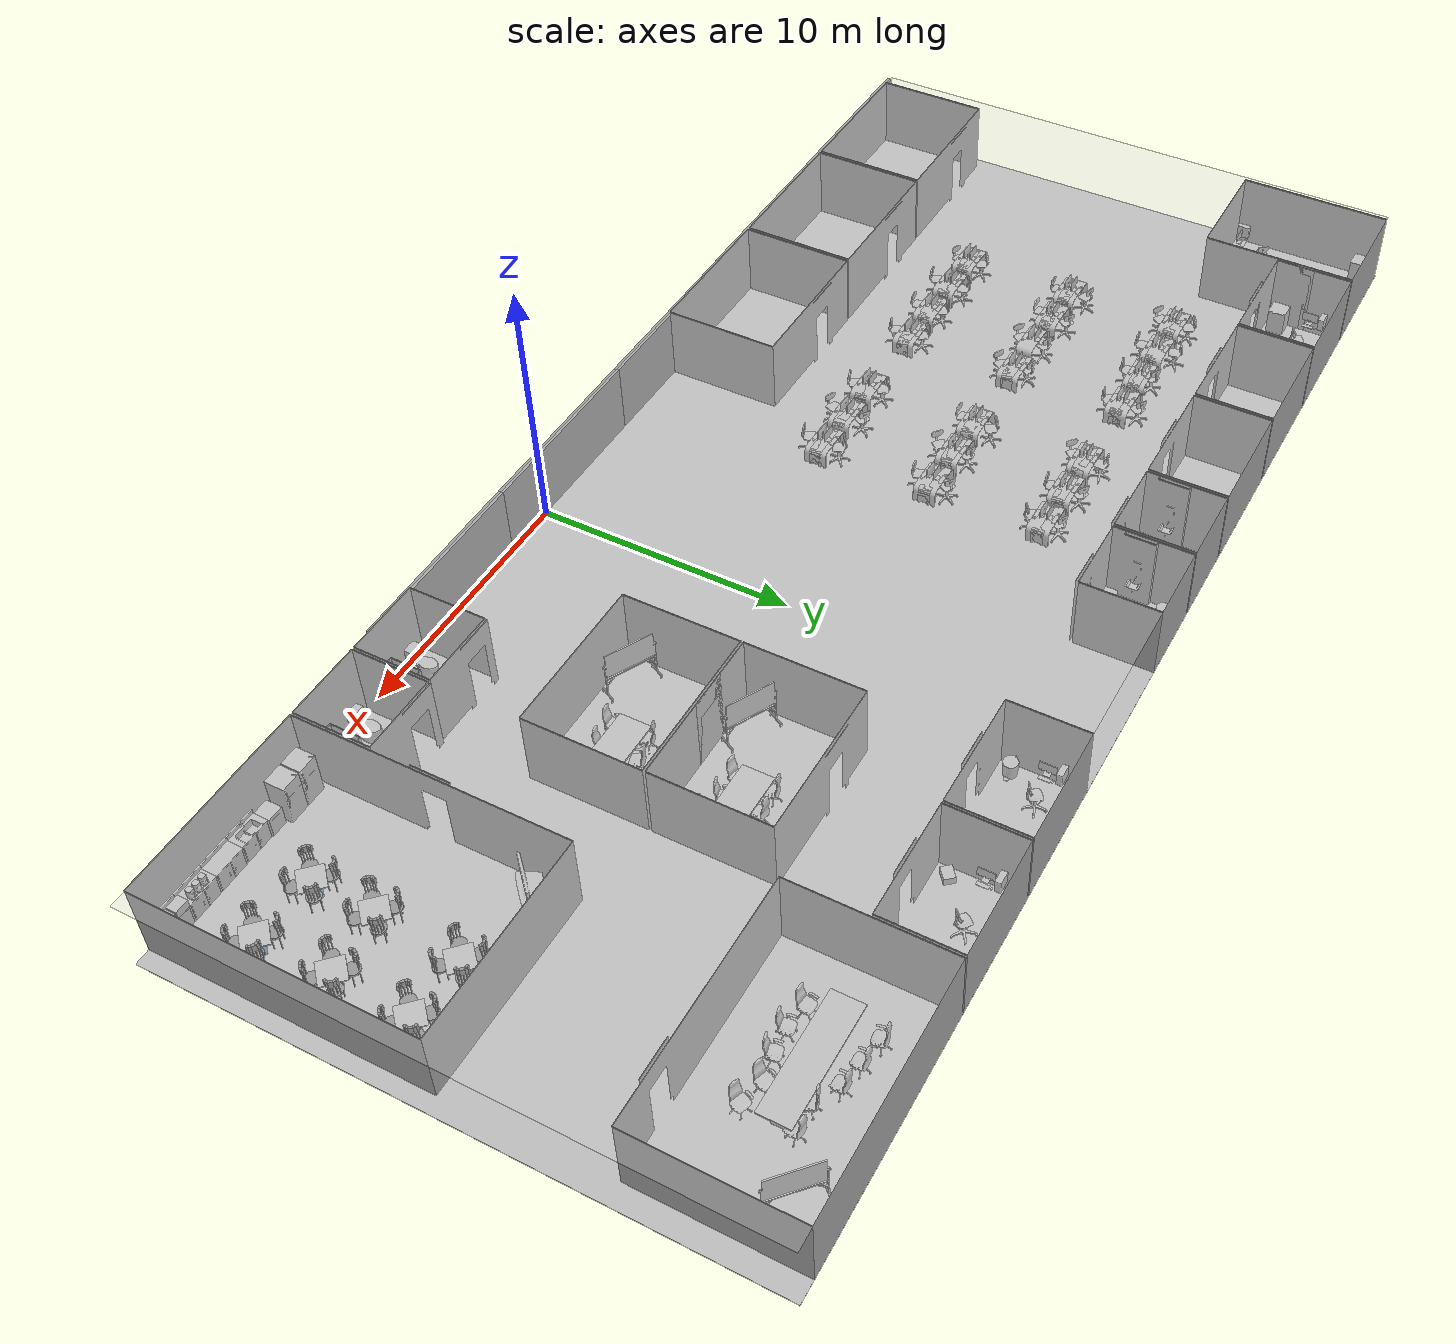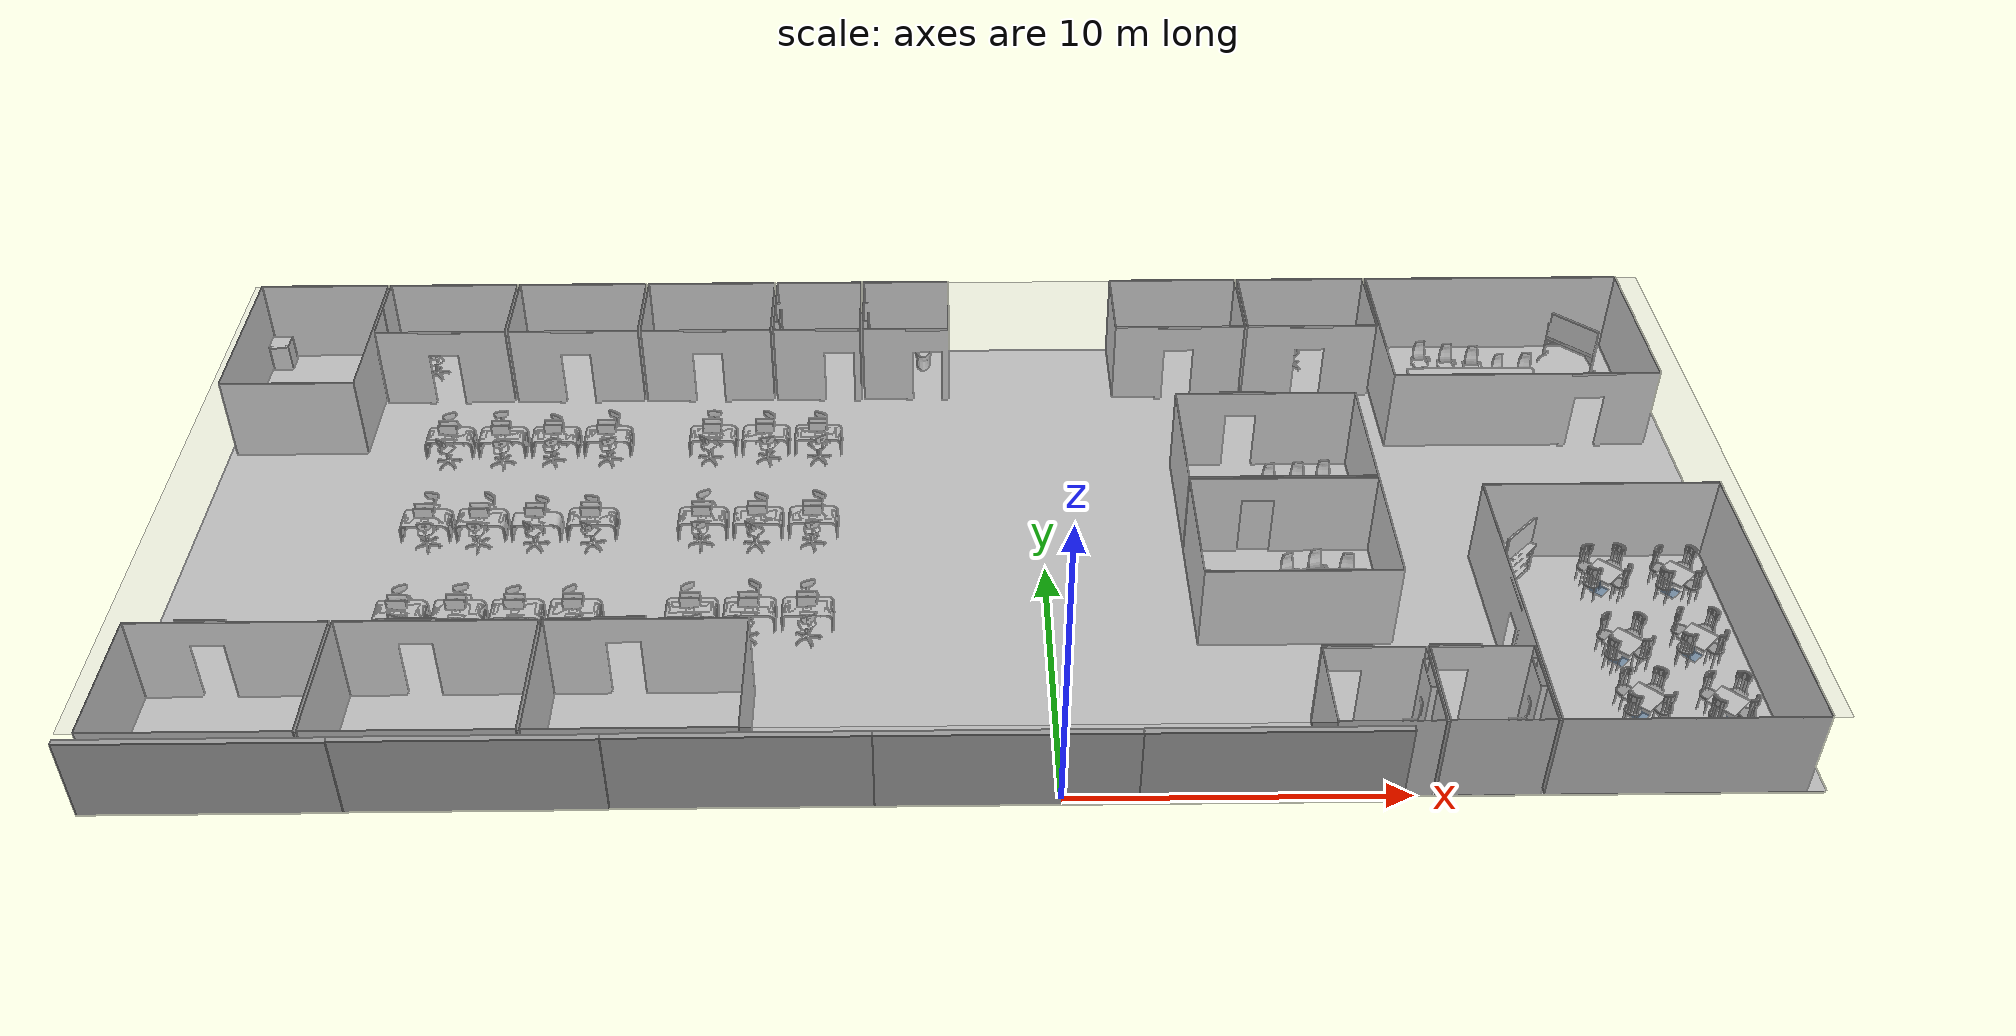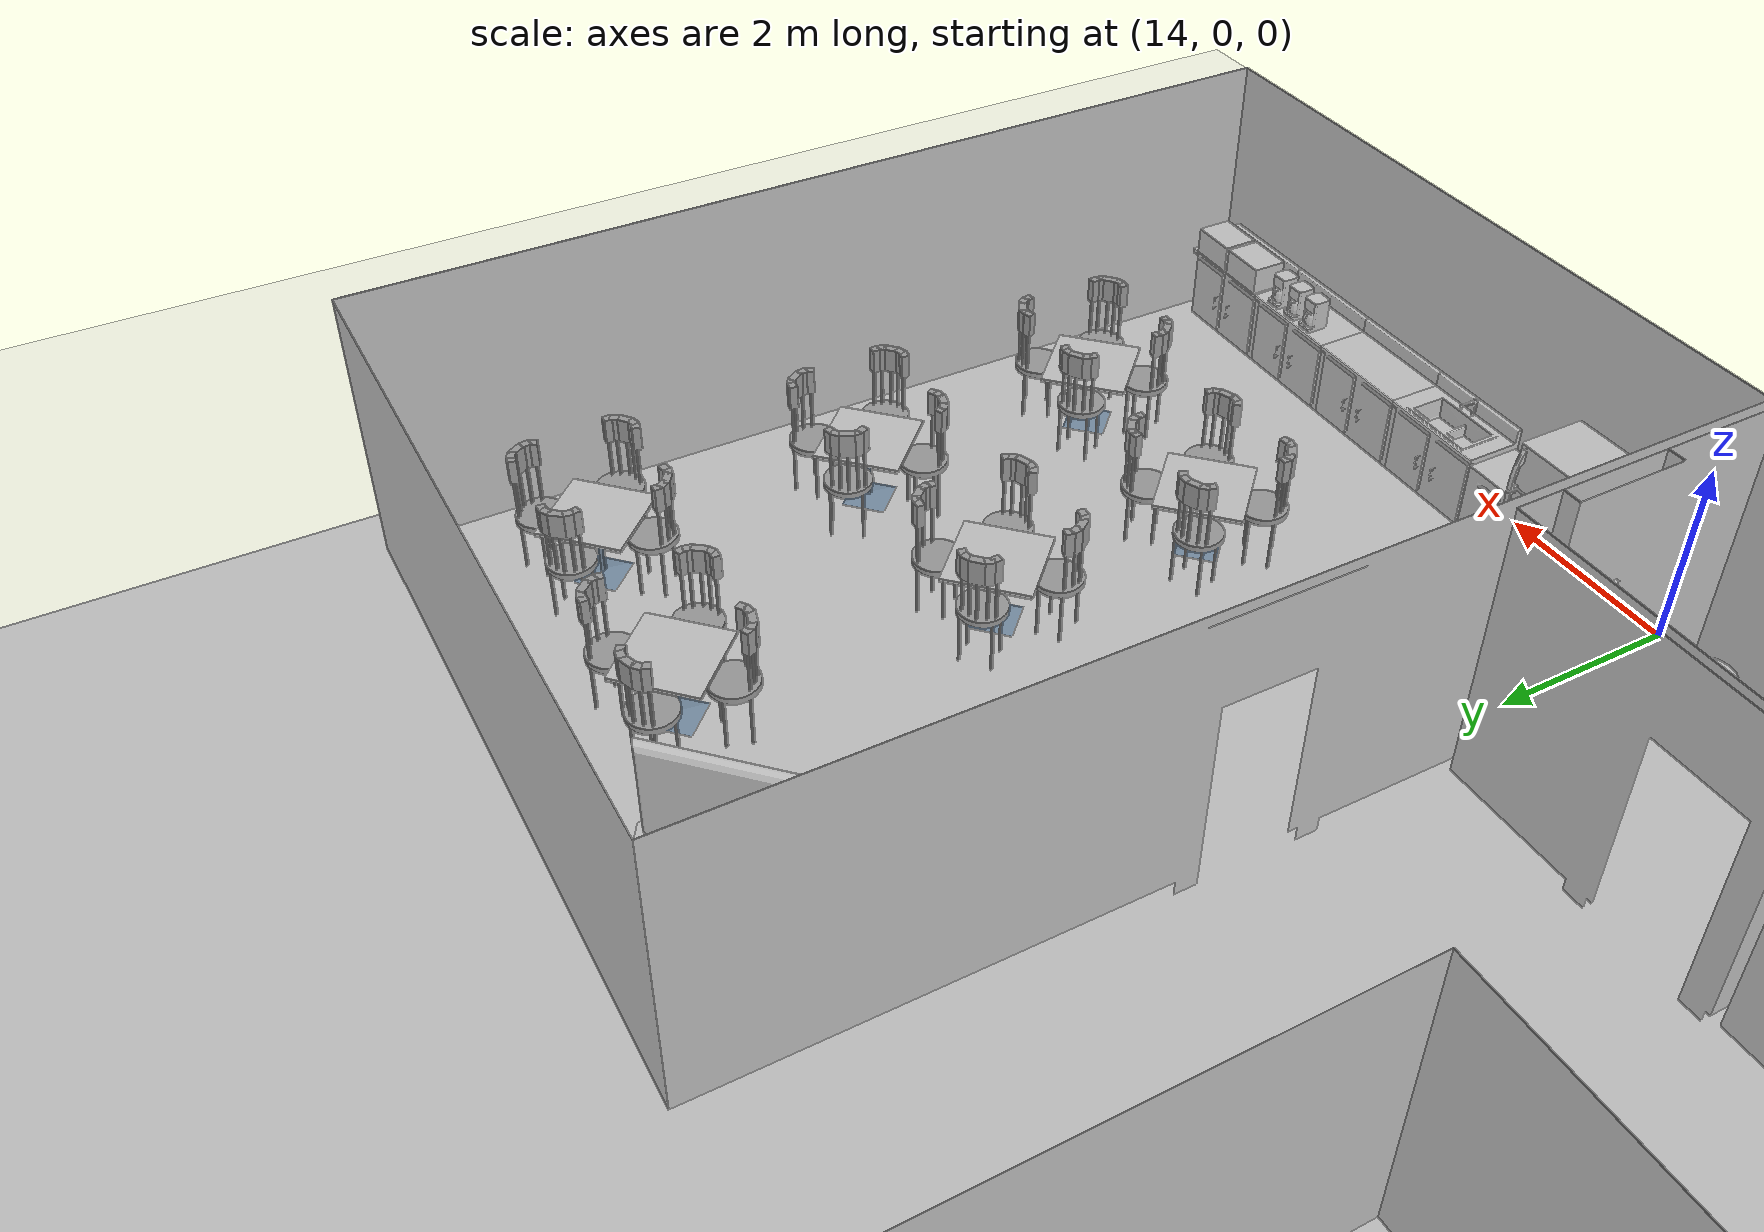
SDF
<sdf version="1.7">
 <world name="default">
  <physics type="ode">
   <real_time_update_rate>500</real_time_update_rate>
   <max_step_size>0.002</max_step_size>
   <real_time_factor>1</real_time_factor>
   <ode>
    <solver>
     <type>quick</type>
     <iters>300</iters>
     <precon_iters>0</precon_iters>
     <sor>1.4</sor>
     <use_dynamic_moi_rescaling>1</use_dynamic_moi_rescaling>
    </solver>
    <constraints>
     <cfm>0</cfm>
     <erp>0.8</erp>
     <contact_max_correcting_vel>2000</contact_max_correcting_vel>
     <contact_surface_layer>0.01</contact_surface_layer>
    </constraints>
   </ode>
  </physics>
  <scene>
   <ambient>0.8 0.8 0.8 1</ambient>
   <background>0.66 0.77 0.84 1</background>
   <grid>0</grid>
   <origin_visual>0</origin_visual>
   <shadows>1</shadows>
  </scene>
  <light name="directional_light" type="directional">
   <pose>0 0 -100 0 -0 0</pose>
   <diffuse>0.5 0.5 0.5 1</diffuse>
   <specular>0.1 0.1 0.1 1</specular>
   <direction>0.1 0.1 -0.9</direction>
   <attenuation>
    <range>20</range>
    <constant>0.5</constant>
    <linear>0.01</linear>
    <quadratic>0.001</quadratic>
   </attenuation>
   <cast_shadows>0</cast_shadows>
   <spot><inner_angle>0</inner_angle><outer_angle>0</outer_angle><falloff>0</falloff></spot>
  </light>
  <model name="ceiling">
   <pose>-2.97 11.25 3 3.14159 -0 3.14159</pose>
   <static>1</static>
   <link name="link">
    <visual name="visual">
     <geometry><plane><normal>0 0 1</normal><size>49.5 22.5</size></plane></geometry>
     <material>
      <script>
       <uri>model://media/materials/scripts/</uri>
       <uri>model://media/materials/textures/</uri>
       <name>ServiceSim/Ceiling</name>
      </script>
     </material>
    </visual>
   </link>
  </model>
  <model name="floor">
   <pose>-2.97 11.25 -0.001 0 -0 0</pose>
   <static>1</static>
   <link name="link">
    <visual name="visual">
     <geometry><plane><normal>0 0 1</normal><size>49.5 22.5</size></plane></geometry>
     <material>
      <script>
       <uri>model://media/materials/scripts/</uri>
       <uri>model://media/materials/textures/</uri>
       <name>ServiceSim/Hallway</name>
      </script>
     </material>
    </visual>
    <collision name="collision">
     <geometry><plane><normal>0 0 1</normal><size>49.5 22.5</size></plane></geometry>
     <surface><friction><ode><mu>1</mu><mu2>1</mu2></ode></friction></surface>
    </collision>
   </link>
  </model>
  <model name="PublicBathroomA">
   <static>1</static>
   <pose>9 3 0 0 -0 0</pose>
   <link name="link">
    <collision name="right_of_door">
     <pose>0.63 0.05 1.5 0 -0 0</pose>
     <geometry><box><size>1.74 0.1 3</size></box></geometry>
    </collision>
    <collision name="left_of_door">
     <pose>-1.38 0.05 1.5 0 -0 0</pose>
     <geometry><box><size>0.24 0.1 3</size></box></geometry>
    </collision>
    <collision name="top_of_door">
     <pose>-0.75 0.05 2.55 0 -0 0</pose>
     <geometry><box><size>1.5 0.1 0.9</size></box></geometry>
    </collision>
    <collision name="right">
     <pose>1.55 -1.5 1.5 0 -0 0</pose>
     <geometry><box><size>0.1 3 3</size></box></geometry>
    </collision>
    <collision name="left">
     <pose>-1.55 -1.5 1.5 0 -0 0</pose>
     <geometry><box><size>0.1 3 3</size></box></geometry>
    </collision>
    <collision name="back">
     <pose>0 -3.05 1.5 0 -0 0</pose>
     <geometry><box><size>3 0.1 3</size></box></geometry>
    </collision>
    <visual name="visual">
     <geometry><mesh><uri>model://media/meshes/bathroom.obj</uri><scale>0.01 0.01 0.01</scale></mesh></geometry>
    </visual>
    <visual name="floor_0_-1">
     <pose>0 -1.5 0 0 -0 0</pose>
     <geometry><mesh><uri>model://media/meshes/tile.obj</uri><scale>0.01 0.01 0.01</scale></mesh></geometry>
    </visual>
    <visual name="floor_0_0">
     <geometry><mesh><uri>model://media/meshes/tile.obj</uri><scale>0.01 0.01 0.01</scale></mesh></geometry>
    </visual>
    <visual name="floor_1_-1">
     <pose>1.5 -1.5 0 0 -0 0</pose>
     <geometry><mesh><uri>model://media/meshes/tile.obj</uri><scale>0.01 0.01 0.01</scale></mesh></geometry>
    </visual>
    <visual name="floor_1_0">
     <pose>1.5 0 0 0 -0 0</pose>
     <geometry><mesh><uri>model://media/meshes/tile.obj</uri><scale>0.01 0.01 0.01</scale></mesh></geometry>
    </visual>
   </link>
   <frame name="toilet::__model__" attached_to="toilet::link">
    <pose relative_to="__model__">-0.6 -2.1 0 0 -0 3.14159</pose>
   </frame>
   <static>1</static>
   <link name="toilet::link">
    <collision name="collision">
     <pose>-0.003873 0.134001 0.582097 0 -0 0</pose>
     <geometry><box><size>0.551631 1.09406 1.18218</size></box></geometry>
    </collision>
    <visual name="visual">
     <geometry><mesh><uri>model://toilet/meshes/toilet.dae</uri><scale>1.4 1.4 1.4</scale></mesh></geometry>
    </visual>
    <pose relative_to="toilet::__model__">0 0 0 0 -0 0</pose>
   </link>
   <frame name="wastebasket::__model__" attached_to="wastebasket::link">
    <pose relative_to="__model__">0.9 -2.35 0 0 0 -0.785398</pose>
   </frame>
   <static>1</static>
   <link name="wastebasket::link">
    <pose relative_to="wastebasket::__model__">0 0 0 0 -0 1.5708</pose>
    <collision name="collision">
     <pose>0.001581 0.000308 0.312969 0 -0 0</pose>
     <geometry><cylinder><radius>0.27</radius><length>0.63</length></cylinder></geometry>
    </collision>
    <visual name="visual">
     <geometry>
      <mesh><uri>model://wastebasket/meshes/wastebasket.dae</uri><scale>1.4 1.4 1.4</scale></mesh>
     </geometry>
    </visual>
   </link>
  </model>
  <model name="PublicBathroomB">
   <static>1</static>
   <pose>12.1 3 0 0 -0 0</pose>
   <link name="link">
    <collision name="right_of_door">
     <pose>0.63 0.05 1.5 0 -0 0</pose>
     <geometry><box><size>1.74 0.1 3</size></box></geometry>
    </collision>
    <collision name="left_of_door">
     <pose>-1.38 0.05 1.5 0 -0 0</pose>
     <geometry><box><size>0.24 0.1 3</size></box></geometry>
    </collision>
    <collision name="top_of_door">
     <pose>-0.75 0.05 2.55 0 -0 0</pose>
     <geometry><box><size>1.5 0.1 0.9</size></box></geometry>
    </collision>
    <collision name="right">
     <pose>1.55 -1.5 1.5 0 -0 0</pose>
     <geometry><box><size>0.1 3 3</size></box></geometry>
    </collision>
    <collision name="left">
     <pose>-1.55 -1.5 1.5 0 -0 0</pose>
     <geometry><box><size>0.1 3 3</size></box></geometry>
    </collision>
    <collision name="back">
     <pose>0 -3.05 1.5 0 -0 0</pose>
     <geometry><box><size>3 0.1 3</size></box></geometry>
    </collision>
    <visual name="visual">
     <geometry><mesh><uri>model://media/meshes/bathroom.obj</uri><scale>0.01 0.01 0.01</scale></mesh></geometry>
    </visual>
    <visual name="floor_0_-1">
     <pose>0 -1.5 0 0 -0 0</pose>
     <geometry><mesh><uri>model://media/meshes/tile.obj</uri><scale>0.01 0.01 0.01</scale></mesh></geometry>
    </visual>
    <visual name="floor_0_0">
     <geometry><mesh><uri>model://media/meshes/tile.obj</uri><scale>0.01 0.01 0.01</scale></mesh></geometry>
    </visual>
    <visual name="floor_1_-1">
     <pose>1.5 -1.5 0 0 -0 0</pose>
     <geometry><mesh><uri>model://media/meshes/tile.obj</uri><scale>0.01 0.01 0.01</scale></mesh></geometry>
    </visual>
    <visual name="floor_1_0">
     <pose>1.5 0 0 0 -0 0</pose>
     <geometry><mesh><uri>model://media/meshes/tile.obj</uri><scale>0.01 0.01 0.01</scale></mesh></geometry>
    </visual>
   </link>
   <frame name="toilet::__model__" attached_to="toilet::link">
    <pose relative_to="__model__">-0.6 -2.1 0 0 -0 3.14159</pose>
   </frame>
   <static>1</static>
   <link name="toilet::link">
    <collision name="collision">
     <pose>-0.003873 0.134001 0.582097 0 -0 0</pose>
     <geometry><box><size>0.551631 1.09406 1.18218</size></box></geometry>
    </collision>
    <visual name="visual">
     <geometry><mesh><uri>model://toilet/meshes/toilet.dae</uri><scale>1.4 1.4 1.4</scale></mesh></geometry>
    </visual>
    <pose relative_to="toilet::__model__">0 0 0 0 -0 0</pose>
   </link>
   <frame name="wastebasket::__model__" attached_to="wastebasket::link">
    <pose relative_to="__model__">0.9 -2.35 0 0 0 -0.785398</pose>
   </frame>
   <static>1</static>
   <link name="wastebasket::link">
    <pose relative_to="wastebasket::__model__">0 0 0 0 -0 1.5708</pose>
    <collision name="collision">
     <pose>0.001581 0.000308 0.312969 0 -0 0</pose>
     <geometry><cylinder><radius>0.27</radius><length>0.63</length></cylinder></geometry>
    </collision>
    <visual name="visual">
     <geometry>
      <mesh><uri>model://wastebasket/meshes/wastebasket.dae</uri><scale>1.4 1.4 1.4</scale></mesh>
     </geometry>
    </visual>
   </link>
  </model>
  <model name="PublicCafe">
   <static>1</static>
   <pose>13.7 6 0 0 -0 1.5708</pose>
   <link name="link">
    <collision name="right_of_door">
     <pose>2.13 0.05 1.5 0 -0 0</pose>
     <geometry><box><size>4.74 0.1 3</size></box></geometry>
    </collision>
    <collision name="left_of_door">
     <pose>-3.63 0.05 1.5 0 -0 0</pose>
     <geometry><box><size>4.74 0.1 3</size></box></geometry>
    </collision>
    <collision name="top_of_door">
     <pose>-0.75 0.05 2.55 0 -0 0</pose>
     <geometry><box><size>1.5 0.1 0.9</size></box></geometry>
    </collision>
    <collision name="right">
     <pose>4.55 -3.75 1.5 0 -0 0</pose>
     <geometry><box><size>0.1 7.5 3</size></box></geometry>
    </collision>
    <collision name="left">
     <pose>-6.05 -3.75 1.5 0 -0 0</pose>
     <geometry><box><size>0.1 7.5 3</size></box></geometry>
    </collision>
    <collision name="back">
     <pose>-0.75 -7.55 1.5 0 -0 0</pose>
     <geometry><box><size>10.5 0.1 3</size></box></geometry>
    </collision>
    <visual name="visual">
     <geometry>
      <mesh><uri>model://media/meshes/refreshment_area.obj</uri><scale>0.01 0.01 0.01</scale></mesh>
     </geometry>
    </visual>
    <visual name="floor_-3_-4">
     <pose>-4.5 -6 0 0 -0 0</pose>
     <geometry><mesh><uri>model://media/meshes/tile.obj</uri><scale>0.01 0.01 0.01</scale></mesh></geometry>
    </visual>
    <visual name="floor_-3_-3">
     <pose>-4.5 -4.5 0 0 -0 0</pose>
     <geometry><mesh><uri>model://media/meshes/tile.obj</uri><scale>0.01 0.01 0.01</scale></mesh></geometry>
    </visual>
    <visual name="floor_-3_-2">
     <pose>-4.5 -3 0 0 -0 0</pose>
     <geometry><mesh><uri>model://media/meshes/tile.obj</uri><scale>0.01 0.01 0.01</scale></mesh></geometry>
    </visual>
    <visual name="floor_-3_-1">
     <pose>-4.5 -1.5 0 0 -0 0</pose>
     <geometry><mesh><uri>model://media/meshes/tile.obj</uri><scale>0.01 0.01 0.01</scale></mesh></geometry>
    </visual>
    <visual name="floor_-3_0">
     <pose>-4.5 0 0 0 -0 0</pose>
     <geometry><mesh><uri>model://media/meshes/tile.obj</uri><scale>0.01 0.01 0.01</scale></mesh></geometry>
    </visual>
    <visual name="floor_-2_-4">
     <pose>-3 -6 0 0 -0 0</pose>
     <geometry><mesh><uri>model://media/meshes/tile.obj</uri><scale>0.01 0.01 0.01</scale></mesh></geometry>
    </visual>
    <visual name="floor_-2_-3">
     <pose>-3 -4.5 0 0 -0 0</pose>
     <geometry><mesh><uri>model://media/meshes/tile.obj</uri><scale>0.01 0.01 0.01</scale></mesh></geometry>
    </visual>
    <visual name="floor_-2_-2">
     <pose>-3 -3 0 0 -0 0</pose>
     <geometry><mesh><uri>model://media/meshes/tile.obj</uri><scale>0.01 0.01 0.01</scale></mesh></geometry>
    </visual>
    <visual name="floor_-2_-1">
     <pose>-3 -1.5 0 0 -0 0</pose>
     <geometry><mesh><uri>model://media/meshes/tile.obj</uri><scale>0.01 0.01 0.01</scale></mesh></geometry>
    </visual>
    <visual name="floor_-2_0">
     <pose>-3 0 0 0 -0 0</pose>
     <geometry><mesh><uri>model://media/meshes/tile.obj</uri><scale>0.01 0.01 0.01</scale></mesh></geometry>
    </visual>
    <visual name="floor_-1_-4">
     <pose>-1.5 -6 0 0 -0 0</pose>
     <geometry><mesh><uri>model://media/meshes/tile.obj</uri><scale>0.01 0.01 0.01</scale></mesh></geometry>
    </visual>
    <visual name="floor_-1_-3">
     <pose>-1.5 -4.5 0 0 -0 0</pose>
     <geometry><mesh><uri>model://media/meshes/tile.obj</uri><scale>0.01 0.01 0.01</scale></mesh></geometry>
    </visual>
    <visual name="floor_-1_-2">
     <pose>-1.5 -3 0 0 -0 0</pose>
     <geometry><mesh><uri>model://media/meshes/tile.obj</uri><scale>0.01 0.01 0.01</scale></mesh></geometry>
    </visual>
    <visual name="floor_-1_-1">
     <pose>-1.5 -1.5 0 0 -0 0</pose>
     <geometry><mesh><uri>model://media/meshes/tile.obj</uri><scale>0.01 0.01 0.01</scale></mesh></geometry>
    </visual>
    <visual name="floor_-1_0">
     <pose>-1.5 0 0 0 -0 0</pose>
     <geometry><mesh><uri>model://media/meshes/tile.obj</uri><scale>0.01 0.01 0.01</scale></mesh></geometry>
    </visual>
    <visual name="floor_0_-4">
     <pose>0 -6 0 0 -0 0</pose>
     <geometry><mesh><uri>model://media/meshes/tile.obj</uri><scale>0.01 0.01 0.01</scale></mesh></geometry>
    </visual>
    <visual name="floor_0_-3">
     <pose>0 -4.5 0 0 -0 0</pose>
     <geometry><mesh><uri>model://media/meshes/tile.obj</uri><scale>0.01 0.01 0.01</scale></mesh></geometry>
    </visual>
    <visual name="floor_0_-2">
     <pose>0 -3 0 0 -0 0</pose>
     <geometry><mesh><uri>model://media/meshes/tile.obj</uri><scale>0.01 0.01 0.01</scale></mesh></geometry>
    </visual>
    <visual name="floor_0_-1">
     <pose>0 -1.5 0 0 -0 0</pose>
     <geometry><mesh><uri>model://media/meshes/tile.obj</uri><scale>0.01 0.01 0.01</scale></mesh></geometry>
    </visual>
    <visual name="floor_0_0">
     <geometry><mesh><uri>model://media/meshes/tile.obj</uri><scale>0.01 0.01 0.01</scale></mesh></geometry>
    </visual>
    <visual name="floor_1_-4">
     <pose>1.5 -6 0 0 -0 0</pose>
     <geometry><mesh><uri>model://media/meshes/tile.obj</uri><scale>0.01 0.01 0.01</scale></mesh></geometry>
    </visual>
    <visual name="floor_1_-3">
     <pose>1.5 -4.5 0 0 -0 0</pose>
     <geometry><mesh><uri>model://media/meshes/tile.obj</uri><scale>0.01 0.01 0.01</scale></mesh></geometry>
    </visual>
    <visual name="floor_1_-2">
     <pose>1.5 -3 0 0 -0 0</pose>
     <geometry><mesh><uri>model://media/meshes/tile.obj</uri><scale>0.01 0.01 0.01</scale></mesh></geometry>
    </visual>
    <visual name="floor_1_-1">
     <pose>1.5 -1.5 0 0 -0 0</pose>
     <geometry><mesh><uri>model://media/meshes/tile.obj</uri><scale>0.01 0.01 0.01</scale></mesh></geometry>
    </visual>
    <visual name="floor_1_0">
     <pose>1.5 0 0 0 -0 0</pose>
     <geometry><mesh><uri>model://media/meshes/tile.obj</uri><scale>0.01 0.01 0.01</scale></mesh></geometry>
    </visual>
    <visual name="floor_2_-4">
     <pose>3 -6 0 0 -0 0</pose>
     <geometry><mesh><uri>model://media/meshes/tile.obj</uri><scale>0.01 0.01 0.01</scale></mesh></geometry>
    </visual>
    <visual name="floor_2_-3">
     <pose>3 -4.5 0 0 -0 0</pose>
     <geometry><mesh><uri>model://media/meshes/tile.obj</uri><scale>0.01 0.01 0.01</scale></mesh></geometry>
    </visual>
    <visual name="floor_2_-2">
     <pose>3 -3 0 0 -0 0</pose>
     <geometry><mesh><uri>model://media/meshes/tile.obj</uri><scale>0.01 0.01 0.01</scale></mesh></geometry>
    </visual>
    <visual name="floor_2_-1">
     <pose>3 -1.5 0 0 -0 0</pose>
     <geometry><mesh><uri>model://media/meshes/tile.obj</uri><scale>0.01 0.01 0.01</scale></mesh></geometry>
    </visual>
    <visual name="floor_2_0">
     <pose>3 0 0 0 -0 0</pose>
     <geometry><mesh><uri>model://media/meshes/tile.obj</uri><scale>0.01 0.01 0.01</scale></mesh></geometry>
    </visual>
    <visual name="floor_3_-4">
     <pose>4.5 -6 0 0 -0 0</pose>
     <geometry><mesh><uri>model://media/meshes/tile.obj</uri><scale>0.01 0.01 0.01</scale></mesh></geometry>
    </visual>
    <visual name="floor_3_-3">
     <pose>4.5 -4.5 0 0 -0 0</pose>
     <geometry><mesh><uri>model://media/meshes/tile.obj</uri><scale>0.01 0.01 0.01</scale></mesh></geometry>
    </visual>
    <visual name="floor_3_-2">
     <pose>4.5 -3 0 0 -0 0</pose>
     <geometry><mesh><uri>model://media/meshes/tile.obj</uri><scale>0.01 0.01 0.01</scale></mesh></geometry>
    </visual>
    <visual name="floor_3_-1">
     <pose>4.5 -1.5 0 0 -0 0</pose>
     <geometry><mesh><uri>model://media/meshes/tile.obj</uri><scale>0.01 0.01 0.01</scale></mesh></geometry>
    </visual>
    <visual name="floor_3_0">
     <pose>4.5 0 0 0 -0 0</pose>
     <geometry><mesh><uri>model://media/meshes/tile.obj</uri><scale>0.01 0.01 0.01</scale></mesh></geometry>
    </visual>
   </link>
   <link name="counter_0">
    <pose>-5.7 -6.7 0 0 -0 1.5708</pose>
    <collision name="collision">
     <pose>0 -0.025 0.46 0 -0 0</pose>
     <geometry><box><size>1.2 0.67 0.92</size></box></geometry>
    </collision>
    <visual name="visual">
     <geometry>
      <mesh><uri>model://cafe_counter/meshes/counter_no_sink.obj</uri><scale>0.01 0.01 0.01</scale></mesh>
     </geometry>
    </visual>
   </link>
   <link name="counter_1">
    <pose>-5.7 -5.5 0 0 -0 1.5708</pose>
    <collision name="collision">
     <pose>0 -0.025 0.46 0 -0 0</pose>
     <geometry><box><size>1.2 0.67 0.92</size></box></geometry>
    </collision>
    <visual name="visual">
     <geometry>
      <mesh><uri>model://cafe_counter/meshes/counter_no_sink.obj</uri><scale>0.01 0.01 0.01</scale></mesh>
     </geometry>
    </visual>
   </link>
   <link name="counter_2">
    <pose>-5.7 -4.3 0 0 -0 1.5708</pose>
    <collision name="collision">
     <pose>0 -0.025 0.46 0 -0 0</pose>
     <geometry><box><size>1.2 0.67 0.92</size></box></geometry>
    </collision>
    <visual name="visual">
     <geometry>
      <mesh><uri>model://cafe_counter/meshes/counter_no_sink.obj</uri><scale>0.01 0.01 0.01</scale></mesh>
     </geometry>
    </visual>
   </link>
   <link name="counter_3">
    <pose>-5.7 -3.1 0 0 -0 1.5708</pose>
    <collision name="collision">
     <pose>0 -0.025 0.46 0 -0 0</pose>
     <geometry><box><size>1.2 0.67 0.92</size></box></geometry>
    </collision>
    <visual name="visual">
     <geometry>
      <mesh><uri>model://cafe_counter/meshes/counter_sink.obj</uri><scale>0.01 0.01 0.01</scale></mesh>
     </geometry>
    </visual>
   </link>
   <frame name="microwave_1::__model__" attached_to="microwave_1::link">
    <pose relative_to="__model__">-5.54 -6.94 0.92 0 -0 1.5708</pose>
   </frame>
   <static>1</static>
   <link name="microwave_1::link">
    <visual name="visual">
     <geometry>
      <mesh><uri>model://microwave/meshes/microwave.obj</uri><scale>0.01 0.01 0.01</scale></mesh>
     </geometry>
    </visual>
    <pose relative_to="microwave_1::__model__">0 0 0 0 -0 0</pose>
   </link>
   <frame name="microwave_2::__model__" attached_to="microwave_2::link">
    <pose relative_to="__model__">-5.54 -6.38 0.92 0 -0 1.5708</pose>
   </frame>
   <static>1</static>
   <link name="microwave_2::link">
    <visual name="visual">
     <geometry>
      <mesh><uri>model://microwave/meshes/microwave.obj</uri><scale>0.01 0.01 0.01</scale></mesh>
     </geometry>
    </visual>
    <pose relative_to="microwave_2::__model__">0 0 0 0 -0 0</pose>
   </link>
   <frame name="coffee_maker_1::__model__" attached_to="coffee_maker_1::link">
    <pose relative_to="__model__">-5.54 -5.82 0.92 0 -0 1.5708</pose>
   </frame>
   <static>1</static>
   <link name="coffee_maker_1::link">
    <visual name="visual">
     <geometry>
      <mesh><uri>model://coffee_maker/meshes/coffee_maker.obj</uri><scale>0.01 0.01 0.01</scale></mesh>
     </geometry>
    </visual>
    <pose relative_to="coffee_maker_1::__model__">0 0 0 0 -0 0</pose>
   </link>
   <frame name="coffee_maker_2::__model__" attached_to="coffee_maker_2::link">
    <pose relative_to="__model__">-5.54 -5.54 0.92 0 -0 1.5708</pose>
   </frame>
   <static>1</static>
   <link name="coffee_maker_2::link">
    <visual name="visual">
     <geometry>
      <mesh><uri>model://coffee_maker/meshes/coffee_maker.obj</uri><scale>0.01 0.01 0.01</scale></mesh>
     </geometry>
    </visual>
    <pose relative_to="coffee_maker_2::__model__">0 0 0 0 -0 0</pose>
   </link>
   <frame name="coffee_maker_3::__model__" attached_to="coffee_maker_3::link">
    <pose relative_to="__model__">-5.54 -5.26 0.92 0 -0 1.5708</pose>
   </frame>
   <static>1</static>
   <link name="coffee_maker_3::link">
    <visual name="visual">
     <geometry>
      <mesh><uri>model://coffee_maker/meshes/coffee_maker.obj</uri><scale>0.01 0.01 0.01</scale></mesh>
     </geometry>
    </visual>
    <pose relative_to="coffee_maker_3::__model__">0 0 0 0 -0 0</pose>
   </link>
   <frame name="dishwasher::__model__" attached_to="dishwasher::link">
    <pose relative_to="__model__">-5.65 -2.18 0 0 -0 1.5708</pose>
   </frame>
   <static>1</static>
   <link name="dishwasher::link">
    <collision name="collision">
     <pose>-0.002041 0.002974 0.423381 0 -0 0</pose>
     <geometry><box><size>0.61424 0.639467 0.872373</size></box></geometry>
    </collision>
    <visual name="visual">
     <geometry>
      <mesh><uri>model://dishwasher/meshes/dishwasher.obj</uri><scale>0.01 0.01 0.01</scale></mesh>
     </geometry>
    </visual>
    <pose relative_to="dishwasher::__model__">0 0 0 0 -0 0</pose>
   </link>
   <frame name="refrigerator_1::__model__" attached_to="refrigerator_1::link">
    <pose relative_to="__model__">-5.54 -1.4 0 0 -0 1.5708</pose>
   </frame>
   <static>1</static>
   <link name="refrigerator_1::link">
    <collision name="collision">
     <pose>-0.007078 0.009991 0.837838 0 -0 0</pose>
     <geometry><box><size>0.781084 0.825312 1.66079</size></box></geometry>
    </collision>
    <visual name="visual">
     <geometry>
      <mesh><uri>model://refrigerator/meshes/refrigerator.obj</uri><scale>0.01 0.01 0.01</scale></mesh>
     </geometry>
    </visual>
    <pose relative_to="refrigerator_1::__model__">0 0 0 0 -0 0</pose>
   </link>
   <frame name="refrigerator_2::__model__" attached_to="refrigerator_2::link">
    <pose relative_to="__model__">-5.54 -0.59 0 0 -0 1.5708</pose>
   </frame>
   <static>1</static>
   <link name="refrigerator_2::link">
    <collision name="collision">
     <pose>-0.007078 0.009991 0.837838 0 -0 0</pose>
     <geometry><box><size>0.781084 0.825312 1.66079</size></box></geometry>
    </collision>
    <visual name="visual">
     <geometry>
      <mesh><uri>model://refrigerator/meshes/refrigerator.obj</uri><scale>0.01 0.01 0.01</scale></mesh>
     </geometry>
    </visual>
    <pose relative_to="refrigerator_2::__model__">0 0 0 0 -0 0</pose>
   </link>
   <frame name="tv_stand::__model__" attached_to="tv_stand::link">
    <pose relative_to="__model__">3.51 -1 0 0 0 -0.785398</pose>
   </frame>
   <static>1</static>
   <link name="tv_stand::link">
    <collision name="collision">
     <pose>0.00123 -0.018095 1.05314 0 -0 0</pose>
     <geometry><box><size>1.80204 0.803547 2.11292</size></box></geometry>
    </collision>
    <visual name="visual">
     <geometry><mesh><uri>model://tv_stand/meshes/tv_stand.dae</uri><scale>1.4 1.4 1.4</scale></mesh></geometry>
    </visual>
    <pose relative_to="tv_stand::__model__">0 0 0 0 -0 0</pose>
   </link>
   <frame name="table_1::__model__" attached_to="table_1::link">
    <pose relative_to="__model__">-3.0641 -5.98706 0 0 -0 0.785398</pose>
   </frame>
   <static>1</static>
   <link name="table_1::link">
    <collision name="surface">
     <pose>0 0 0.755 0 -0 0</pose>
     <geometry><box><size>0.913 0.913 0.04</size></box></geometry>
    </collision>
    <collision name="column">
     <pose>0 0 0.37 0 -0 0</pose>
     <geometry><box><size>0.042 0.042 0.74</size></box></geometry>
    </collision>
    <collision name="base">
     <pose>0 0 0.02 0 -0 0</pose>
     <geometry><box><size>0.56 0.56 0.04</size></box></geometry>
    </collision>
    <visual name="visual">
     <geometry><mesh><uri>model://office_cafe_table/meshes/office_cafe_table.dae</uri></mesh></geometry>
    </visual>
    <pose relative_to="table_1::__model__">0 0 0 0 -0 0</pose>
   </link>
   <model name="chair_1">
    <static>1</static>
    <pose>-3.5641 -6.48706 0.85 0 0 -2.42909</pose>
    <link name="colision">
     <pose>-0.112954 0 -0.15 0 -0 0</pose>
     <collision name="collision">
      <geometry><cylinder><radius>0.26</radius><length>1.4</length></cylinder></geometry>
     </collision>
    </link>
    <link name="link_0">
     <pose>-0.112954 0.002154 -0.208402 0 -0 0</pose>
     <visual name="visual">
      <geometry><cylinder><radius>0.254492</radius><length>0.0690057</length></cylinder></geometry>
      <material>
       <diffuse>0.5 0.5 0.5 1</diffuse>
       <specular>0.5 0.5 0.5 1</specular>
       <ambient>0.47 0.36 0.19 1</ambient>
      </material>
     </visual>
    </link>
    <link name="link_0_clone">
     <pose>-0.23509 -0.177559 -0.509133 0 -0 0</pose>
     <visual name="visual">
      <geometry><cylinder><radius>0.0139887</radius><length>0.624683</length></cylinder></geometry>
      <material>
       <diffuse>0.5 0.5 0.5 1</diffuse>
       <specular>0.5 0.5 0.5 1</specular>
       <ambient>0.47 0.36 0.19 1</ambient>
      </material>
     </visual>
    </link>
    <link name="link_0_clone_clone">
     <pose>-0.240938 0.153013 -0.509133 0 -0 0</pose>
     <visual name="visual">
      <geometry><cylinder><radius>0.0139887</radius><length>0.624683</length></cylinder></geometry>
      <material>
       <diffuse>0.5 0.5 0.5 1</diffuse>
       <specular>0.5 0.5 0.5 1</specular>
       <ambient>0.47 0.36 0.19 1</ambient>
      </material>
     </visual>
    </link>
    <link name="link_0_clone_clone_0">
     <pose>0.036021 0.151623 -0.509133 0 -0 0</pose>
     <visual name="visual">
      <geometry><cylinder><radius>0.0139887</radius><length>0.624683</length></cylinder></geometry>
      <material>
       <diffuse>0.5 0.5 0.5 1</diffuse>
       <specular>0.5 0.5 0.5 1</specular>
       <ambient>0.47 0.36 0.19 1</ambient>
      </material>
     </visual>
    </link>
    <link name="link_0_clone_clone_1">
     <pose>0.010219 -0.181073 -0.509133 0 -0 0</pose>
     <visual name="visual">
      <geometry><cylinder><radius>0.0139887</radius><length>0.624683</length></cylinder></geometry>
      <material>
       <diffuse>0.5 0.5 0.5 1</diffuse>
       <specular>0.5 0.5 0.5 1</specular>
       <ambient>0.47 0.36 0.19 1</ambient>
      </material>
     </visual>
    </link>
    <link name="link_0_clone_clone_1_clone">
     <pose>0.014987 -0.161898 0.047314 0 -0 0</pose>
     <visual name="visual">
      <geometry><cylinder><radius>0.0139887</radius><length>0.470785</length></cylinder></geometry>
      <material>
       <diffuse>0.5 0.5 0.5 1</diffuse>
       <specular>0.5 0.5 0.5 1</specular>
       <ambient>0.47 0.36 0.19 1</ambient>
      </material>
     </visual>
    </link>
    <link name="link_0_clone_clone_1_clone_clone">
     <pose>0.067643 -0.07581 0.047314 0 -0 0</pose>
     <visual name="visual">
      <geometry><cylinder><radius>0.0139887</radius><length>0.470785</length></cylinder></geometry>
      <material>
       <diffuse>0.5 0.5 0.5 1</diffuse>
       <specular>0.5 0.5 0.5 1</specular>
       <ambient>0.47 0.36 0.19 1</ambient>
      </material>
     </visual>
    </link>
    <link name="link_0_clone_clone_1_clone_clone_0">
     <pose>0.09896 0.009345 0.047314 0 -0 0</pose>
     <visual name="visual">
      <geometry><cylinder><radius>0.0139887</radius><length>0.470785</length></cylinder></geometry>
      <material>
       <diffuse>0.5 0.5 0.5 1</diffuse>
       <specular>0.5 0.5 0.5 1</specular>
       <ambient>0.47 0.36 0.19 1</ambient>
      </material>
     </visual>
    </link>
    <link name="link_0_clone_clone_1_clone_clone_1">
     <pose>0.062061 0.101632 0.047314 0 -0 0</pose>
     <visual name="visual">
      <geometry><cylinder><radius>0.0139887</radius><length>0.470785</length></cylinder></geometry>
      <material>
       <diffuse>0.5 0.5 0.5 1</diffuse>
       <specular>0.5 0.5 0.5 1</specular>
       <ambient>0.47 0.36 0.19 1</ambient>
      </material>
     </visual>
    </link>
    <link name="link_0_clone_clone_1_clone_clone_2">
     <pose>0.017719 0.173047 0.047314 0 -0 0</pose>
     <visual name="visual">
      <geometry><cylinder><radius>0.0139887</radius><length>0.470785</length></cylinder></geometry>
      <material>
       <diffuse>0.5 0.5 0.5 1</diffuse>
       <specular>0.5 0.5 0.5 1</specular>
       <ambient>0.47 0.36 0.19 1</ambient>
      </material>
     </visual>
    </link>
    <link name="link_1">
     <pose>0.029884 -0.160862 0.401672 0 0 -0.896575</pose>
     <visual name="visual">
      <geometry><box><size>0.085272 0.095133 0.269596</size></box></geometry>
      <material>
       <diffuse>0.5 0.5 0.5 1</diffuse>
       <specular>0.5 0.5 0.5 1</specular>
       <ambient>0.47 0.36 0.19 1</ambient>
      </material>
     </visual>
    </link>
    <link name="link_1_clone">
     <pose>0.07344 -0.104423 0.401674 0 0 -0.405782</pose>
     <visual name="visual">
      <geometry><box><size>0.085272 0.095133 0.269596</size></box></geometry>
      <material>
       <diffuse>0.5 0.5 0.5 1</diffuse>
       <specular>0.5 0.5 0.5 1</specular>
       <ambient>0.47 0.36 0.19 1</ambient>
      </material>
     </visual>
    </link>
    <link name="link_1_clone_0">
     <pose>0.086562 0.003017 0.401674 0 -0 0.028173</pose>
     <visual name="visual">
      <geometry><box><size>0.085272 0.161256 0.269596</size></box></geometry>
      <material>
       <diffuse>0.5 0.5 0.5 1</diffuse>
       <specular>0.5 0.5 0.5 1</specular>
       <ambient>0.47 0.36 0.19 1</ambient>
      </material>
     </visual>
    </link>
    <link name="link_1_clone_1">
     <pose>0.06694 0.106481 0.401674 0 -0 0.482169</pose>
     <visual name="visual">
      <geometry><box><size>0.085272 0.095133 0.269596</size></box></geometry>
      <material>
       <diffuse>0.5 0.5 0.5 1</diffuse>
       <specular>0.5 0.5 0.5 1</specular>
       <ambient>0.47 0.36 0.19 1</ambient>
      </material>
     </visual>
    </link>
    <link name="link_1_clone_2">
     <pose>0.021757 0.157964 0.401674 0 -0 0.877817</pose>
     <visual name="visual">
      <geometry><box><size>0.085272 0.095133 0.269596</size></box></geometry>
      <material>
       <diffuse>0.5 0.5 0.5 1</diffuse>
       <specular>0.5 0.5 0.5 1</specular>
       <ambient>0.47 0.36 0.19 1</ambient>
      </material>
     </visual>
    </link>
    <static>0</static>
   </model>
   <model name="chair_2">
    <static>1</static>
    <pose>-3.5641 -5.48706 0.85 0 -0 2.24396</pose>
    <link name="colision">
     <pose>-0.112954 0 -0.15 0 -0 0</pose>
     <collision name="collision">
      <geometry><cylinder><radius>0.26</radius><length>1.4</length></cylinder></geometry>
     </collision>
    </link>
    <link name="link_0">
     <pose>-0.112954 0.002154 -0.208402 0 -0 0</pose>
     <visual name="visual">
      <geometry><cylinder><radius>0.254492</radius><length>0.0690057</length></cylinder></geometry>
      <material>
       <diffuse>0.5 0.5 0.5 1</diffuse>
       <specular>0.5 0.5 0.5 1</specular>
       <ambient>0.36 0.26 0.13 1</ambient>
      </material>
     </visual>
    </link>
    <link name="link_0_clone">
     <pose>-0.23509 -0.177559 -0.509133 0 -0 0</pose>
     <visual name="visual">
      <geometry><cylinder><radius>0.0139887</radius><length>0.624683</length></cylinder></geometry>
      <material>
       <diffuse>0.5 0.5 0.5 1</diffuse>
       <specular>0.5 0.5 0.5 1</specular>
       <ambient>0.36 0.26 0.13 1</ambient>
      </material>
     </visual>
    </link>
    <link name="link_0_clone_clone">
     <pose>-0.240938 0.153013 -0.509133 0 -0 0</pose>
     <visual name="visual">
      <geometry><cylinder><radius>0.0139887</radius><length>0.624683</length></cylinder></geometry>
      <material>
       <diffuse>0.5 0.5 0.5 1</diffuse>
       <specular>0.5 0.5 0.5 1</specular>
       <ambient>0.36 0.26 0.13 1</ambient>
      </material>
     </visual>
    </link>
    <link name="link_0_clone_clone_0">
     <pose>0.036021 0.151623 -0.509133 0 -0 0</pose>
     <visual name="visual">
      <geometry><cylinder><radius>0.0139887</radius><length>0.624683</length></cylinder></geometry>
      <material>
       <diffuse>0.5 0.5 0.5 1</diffuse>
       <specular>0.5 0.5 0.5 1</specular>
       <ambient>0.36 0.26 0.13 1</ambient>
      </material>
     </visual>
    </link>
    <link name="link_0_clone_clone_1">
     <pose>0.010219 -0.181073 -0.509133 0 -0 0</pose>
     <visual name="visual">
      <geometry><cylinder><radius>0.0139887</radius><length>0.624683</length></cylinder></geometry>
      <material>
       <diffuse>0.5 0.5 0.5 1</diffuse>
       <specular>0.5 0.5 0.5 1</specular>
       <ambient>0.36 0.26 0.13 1</ambient>
      </material>
     </visual>
    </link>
    <link name="link_0_clone_clone_1_clone">
     <pose>0.014987 -0.161898 0.047314 0 -0 0</pose>
     <visual name="visual">
      <geometry><cylinder><radius>0.0139887</radius><length>0.470785</length></cylinder></geometry>
      <material>
       <diffuse>0.5 0.5 0.5 1</diffuse>
       <specular>0.5 0.5 0.5 1</specular>
       <ambient>0.36 0.26 0.13 1</ambient>
      </material>
     </visual>
    </link>
    <link name="link_0_clone_clone_1_clone_clone">
     <pose>0.067643 -0.07581 0.047314 0 -0 0</pose>
     <visual name="visual">
      <geometry><cylinder><radius>0.0139887</radius><length>0.470785</length></cylinder></geometry>
      <material>
       <diffuse>0.5 0.5 0.5 1</diffuse>
       <specular>0.5 0.5 0.5 1</specular>
       <ambient>0.36 0.26 0.13 1</ambient>
      </material>
     </visual>
    </link>
    <link name="link_0_clone_clone_1_clone_clone_0">
     <pose>0.09896 0.009345 0.047314 0 -0 0</pose>
     <visual name="visual">
      <geometry><cylinder><radius>0.0139887</radius><length>0.470785</length></cylinder></geometry>
      <material>
       <diffuse>0.5 0.5 0.5 1</diffuse>
       <specular>0.5 0.5 0.5 1</specular>
       <ambient>0.36 0.26 0.13 1</ambient>
      </material>
     </visual>
    </link>
    <link name="link_0_clone_clone_1_clone_clone_1">
     <pose>0.062061 0.101632 0.047314 0 -0 0</pose>
     <visual name="visual">
      <geometry><cylinder><radius>0.0139887</radius><length>0.470785</length></cylinder></geometry>
      <material>
       <diffuse>0.5 0.5 0.5 1</diffuse>
       <specular>0.5 0.5 0.5 1</specular>
       <ambient>0.36 0.26 0.13 1</ambient>
      </material>
     </visual>
    </link>
    <link name="link_0_clone_clone_1_clone_clone_2">
     <pose>0.017719 0.173047 0.047314 0 -0 0</pose>
     <visual name="visual">
      <geometry><cylinder><radius>0.0139887</radius><length>0.470785</length></cylinder></geometry>
      <material>
       <diffuse>0.5 0.5 0.5 1</diffuse>
       <specular>0.5 0.5 0.5 1</specular>
       <ambient>0.36 0.26 0.13 1</ambient>
      </material>
     </visual>
    </link>
    <link name="link_1">
     <pose>0.029884 -0.160862 0.401672 0 0 -0.896575</pose>
     <visual name="visual">
      <geometry><box><size>0.085272 0.095133 0.269596</size></box></geometry>
      <material>
       <diffuse>0.5 0.5 0.5 1</diffuse>
       <specular>0.5 0.5 0.5 1</specular>
       <ambient>0.36 0.26 0.13 1</ambient>
      </material>
     </visual>
    </link>
    <link name="link_1_clone">
     <pose>0.07344 -0.104423 0.401674 0 0 -0.405782</pose>
     <visual name="visual">
      <geometry><box><size>0.085272 0.095133 0.269596</size></box></geometry>
      <material>
       <diffuse>0.5 0.5 0.5 1</diffuse>
       <specular>0.5 0.5 0.5 1</specular>
       <ambient>0.36 0.26 0.13 1</ambient>
      </material>
     </visual>
    </link>
    <link name="link_1_clone_0">
     <pose>0.086562 0.003017 0.401674 0 -0 0.028173</pose>
     <visual name="visual">
      <geometry><box><size>0.085272 0.161256 0.269596</size></box></geometry>
      <material>
       <diffuse>0.5 0.5 0.5 1</diffuse>
       <specular>0.5 0.5 0.5 1</specular>
       <ambient>0.36 0.26 0.13 1</ambient>
      </material>
     </visual>
    </link>
    <link name="link_1_clone_1">
     <pose>0.06694 0.106481 0.401674 0 -0 0.482169</pose>
     <visual name="visual">
      <geometry><box><size>0.085272 0.095133 0.269596</size></box></geometry>
      <material>
       <diffuse>0.5 0.5 0.5 1</diffuse>
       <specular>0.5 0.5 0.5 1</specular>
       <ambient>0.36 0.26 0.13 1</ambient>
      </material>
     </visual>
    </link>
    <link name="link_1_clone_2">
     <pose>0.021757 0.157964 0.401674 0 -0 0.877817</pose>
     <visual name="visual">
      <geometry><box><size>0.085272 0.095133 0.269596</size></box></geometry>
      <material>
       <diffuse>0.5 0.5 0.5 1</diffuse>
       <specular>0.5 0.5 0.5 1</specular>
       <ambient>0.36 0.26 0.13 1</ambient>
      </material>
     </visual>
    </link>
    <static>0</static>
   </model>
   <model name="chair_3">
    <static>1</static>
    <pose>-2.5641 -6.48706 0.85 0 0 -0.536987</pose>
    <link name="colision">
     <pose>-0.112954 0 -0.15 0 -0 0</pose>
     <collision name="collision">
      <geometry><cylinder><radius>0.26</radius><length>1.4</length></cylinder></geometry>
     </collision>
    </link>
    <link name="link_0">
     <pose>-0.112954 0.002154 -0.208402 0 -0 0</pose>
     <visual name="visual">
      <geometry><cylinder><radius>0.254492</radius><length>0.0690057</length></cylinder></geometry>
      <material>
       <diffuse>0.5 0.5 0.5 1</diffuse>
       <specular>0.5 0.5 0.5 1</specular>
       <ambient>0.47 0.36 0.19 1</ambient>
      </material>
     </visual>
    </link>
    <link name="link_0_clone">
     <pose>-0.23509 -0.177559 -0.509133 0 -0 0</pose>
     <visual name="visual">
      <geometry><cylinder><radius>0.0139887</radius><length>0.624683</length></cylinder></geometry>
      <material>
       <diffuse>0.5 0.5 0.5 1</diffuse>
       <specular>0.5 0.5 0.5 1</specular>
       <ambient>0.47 0.36 0.19 1</ambient>
      </material>
     </visual>
    </link>
    <link name="link_0_clone_clone">
     <pose>-0.240938 0.153013 -0.509133 0 -0 0</pose>
     <visual name="visual">
      <geometry><cylinder><radius>0.0139887</radius><length>0.624683</length></cylinder></geometry>
      <material>
       <diffuse>0.5 0.5 0.5 1</diffuse>
       <specular>0.5 0.5 0.5 1</specular>
       <ambient>0.47 0.36 0.19 1</ambient>
      </material>
     </visual>
    </link>
    <link name="link_0_clone_clone_0">
     <pose>0.036021 0.151623 -0.509133 0 -0 0</pose>
     <visual name="visual">
      <geometry><cylinder><radius>0.0139887</radius><length>0.624683</length></cylinder></geometry>
      <material>
       <diffuse>0.5 0.5 0.5 1</diffuse>
       <specular>0.5 0.5 0.5 1</specular>
       <ambient>0.47 0.36 0.19 1</ambient>
      </material>
     </visual>
    </link>
    <link name="link_0_clone_clone_1">
     <pose>0.010219 -0.181073 -0.509133 0 -0 0</pose>
     <visual name="visual">
      <geometry><cylinder><radius>0.0139887</radius><length>0.624683</length></cylinder></geometry>
      <material>
       <diffuse>0.5 0.5 0.5 1</diffuse>
       <specular>0.5 0.5 0.5 1</specular>
       <ambient>0.47 0.36 0.19 1</ambient>
      </material>
     </visual>
    </link>
    <link name="link_0_clone_clone_1_clone">
     <pose>0.014987 -0.161898 0.047314 0 -0 0</pose>
     <visual name="visual">
      <geometry><cylinder><radius>0.0139887</radius><length>0.470785</length></cylinder></geometry>
      <material>
       <diffuse>0.5 0.5 0.5 1</diffuse>
       <specular>0.5 0.5 0.5 1</specular>
       <ambient>0.47 0.36 0.19 1</ambient>
      </material>
     </visual>
    </link>
    <link name="link_0_clone_clone_1_clone_clone">
     <pose>0.067643 -0.07581 0.047314 0 -0 0</pose>
     <visual name="visual">
      <geometry><cylinder><radius>0.0139887</radius><length>0.470785</length></cylinder></geometry>
      <material>
       <diffuse>0.5 0.5 0.5 1</diffuse>
       <specular>0.5 0.5 0.5 1</specular>
       <ambient>0.47 0.36 0.19 1</ambient>
      </material>
     </visual>
    </link>
    <link name="link_0_clone_clone_1_clone_clone_0">
     <pose>0.09896 0.009345 0.047314 0 -0 0</pose>
     <visual name="visual">
      <geometry><cylinder><radius>0.0139887</radius><length>0.470785</length></cylinder></geometry>
      <material>
       <diffuse>0.5 0.5 0.5 1</diffuse>
       <specular>0.5 0.5 0.5 1</specular>
       <ambient>0.47 0.36 0.19 1</ambient>
      </material>
     </visual>
    </link>
    <link name="link_0_clone_clone_1_clone_clone_1">
     <pose>0.062061 0.101632 0.047314 0 -0 0</pose>
     <visual name="visual">
      <geometry><cylinder><radius>0.0139887</radius><length>0.470785</length></cylinder></geometry>
      <material>
       <diffuse>0.5 0.5 0.5 1</diffuse>
       <specular>0.5 0.5 0.5 1</specular>
       <ambient>0.47 0.36 0.19 1</ambient>
      </material>
     </visual>
    </link>
    <link name="link_0_clone_clone_1_clone_clone_2">
     <pose>0.017719 0.173047 0.047314 0 -0 0</pose>
     <visual name="visual">
      <geometry><cylinder><radius>0.0139887</radius><length>0.470785</length></cylinder></geometry>
      <material>
       <diffuse>0.5 0.5 0.5 1</diffuse>
       <specular>0.5 0.5 0.5 1</specular>
       <ambient>0.47 0.36 0.19 1</ambient>
      </material>
     </visual>
    </link>
    <link name="link_1">
     <pose>0.029884 -0.160862 0.401672 0 0 -0.896575</pose>
     <visual name="visual">
      <geometry><box><size>0.085272 0.095133 0.269596</size></box></geometry>
      <material>
       <diffuse>0.5 0.5 0.5 1</diffuse>
       <specular>0.5 0.5 0.5 1</specular>
       <ambient>0.47 0.36 0.19 1</ambient>
      </material>
     </visual>
    </link>
    <link name="link_1_clone">
     <pose>0.07344 -0.104423 0.401674 0 0 -0.405782</pose>
     <visual name="visual">
      <geometry><box><size>0.085272 0.095133 0.269596</size></box></geometry>
      <material>
       <diffuse>0.5 0.5 0.5 1</diffuse>
       <specular>0.5 0.5 0.5 1</specular>
       <ambient>0.47 0.36 0.19 1</ambient>
      </material>
     </visual>
    </link>
    <link name="link_1_clone_0">
     <pose>0.086562 0.003017 0.401674 0 -0 0.028173</pose>
     <visual name="visual">
      <geometry><box><size>0.085272 0.161256 0.269596</size></box></geometry>
      <material>
       <diffuse>0.5 0.5 0.5 1</diffuse>
       <specular>0.5 0.5 0.5 1</specular>
       <ambient>0.47 0.36 0.19 1</ambient>
      </material>
     </visual>
    </link>
    <link name="link_1_clone_1">
     <pose>0.06694 0.106481 0.401674 0 -0 0.482169</pose>
     <visual name="visual">
      <geometry><box><size>0.085272 0.095133 0.269596</size></box></geometry>
      <material>
       <diffuse>0.5 0.5 0.5 1</diffuse>
       <specular>0.5 0.5 0.5 1</specular>
       <ambient>0.47 0.36 0.19 1</ambient>
      </material>
     </visual>
    </link>
    <link name="link_1_clone_2">
     <pose>0.021757 0.157964 0.401674 0 -0 0.877817</pose>
     <visual name="visual">
      <geometry><box><size>0.085272 0.095133 0.269596</size></box></geometry>
      <material>
       <diffuse>0.5 0.5 0.5 1</diffuse>
       <specular>0.5 0.5 0.5 1</specular>
       <ambient>0.47 0.36 0.19 1</ambient>
      </material>
     </visual>
    </link>
    <static>0</static>
   </model>
   <model name="chair_4">
    <static>1</static>
    <pose>-2.5641 -5.48706 0.85 0 -0 0.562163</pose>
    <link name="colision">
     <pose>-0.112954 0 -0.15 0 -0 0</pose>
     <collision name="collision">
      <geometry><cylinder><radius>0.26</radius><length>1.4</length></cylinder></geometry>
     </collision>
    </link>
    <link name="link_0">
     <pose>-0.112954 0.002154 -0.208402 0 -0 0</pose>
     <visual name="visual">
      <geometry><cylinder><radius>0.254492</radius><length>0.0690057</length></cylinder></geometry>
      <material>
       <diffuse>0.5 0.5 0.5 1</diffuse>
       <specular>0.5 0.5 0.5 1</specular>
       <ambient>0.36 0.26 0.13 1</ambient>
      </material>
     </visual>
    </link>
    <link name="link_0_clone">
     <pose>-0.23509 -0.177559 -0.509133 0 -0 0</pose>
     <visual name="visual">
      <geometry><cylinder><radius>0.0139887</radius><length>0.624683</length></cylinder></geometry>
      <material>
       <diffuse>0.5 0.5 0.5 1</diffuse>
       <specular>0.5 0.5 0.5 1</specular>
       <ambient>0.36 0.26 0.13 1</ambient>
      </material>
     </visual>
    </link>
    <link name="link_0_clone_clone">
     <pose>-0.240938 0.153013 -0.509133 0 -0 0</pose>
     <visual name="visual">
      <geometry><cylinder><radius>0.0139887</radius><length>0.624683</length></cylinder></geometry>
      <material>
       <diffuse>0.5 0.5 0.5 1</diffuse>
       <specular>0.5 0.5 0.5 1</specular>
       <ambient>0.36 0.26 0.13 1</ambient>
      </material>
     </visual>
    </link>
    <link name="link_0_clone_clone_0">
     <pose>0.036021 0.151623 -0.509133 0 -0 0</pose>
     <visual name="visual">
      <geometry><cylinder><radius>0.0139887</radius><length>0.624683</length></cylinder></geometry>
      <material>
       <diffuse>0.5 0.5 0.5 1</diffuse>
       <specular>0.5 0.5 0.5 1</specular>
       <ambient>0.36 0.26 0.13 1</ambient>
      </material>
     </visual>
    </link>
    <link name="link_0_clone_clone_1">
     <pose>0.010219 -0.181073 -0.509133 0 -0 0</pose>
     <visual name="visual">
      <geometry><cylinder><radius>0.0139887</radius><length>0.624683</length></cylinder></geometry>
      <material>
       <diffuse>0.5 0.5 0.5 1</diffuse>
       <specular>0.5 0.5 0.5 1</specular>
       <ambient>0.36 0.26 0.13 1</ambient>
      </material>
     </visual>
    </link>
    <link name="link_0_clone_clone_1_clone">
     <pose>0.014987 -0.161898 0.047314 0 -0 0</pose>
     <visual name="visual">
      <geometry><cylinder><radius>0.0139887</radius><length>0.470785</length></cylinder></geometry>
      <material>
       <diffuse>0.5 0.5 0.5 1</diffuse>
       <specular>0.5 0.5 0.5 1</specular>
       <ambient>0.36 0.26 0.13 1</ambient>
      </material>
     </visual>
    </link>
    <link name="link_0_clone_clone_1_clone_clone">
     <pose>0.067643 -0.07581 0.047314 0 -0 0</pose>
     <visual name="visual">
      <geometry><cylinder><radius>0.0139887</radius><length>0.470785</length></cylinder></geometry>
      <material>
       <diffuse>0.5 0.5 0.5 1</diffuse>
       <specular>0.5 0.5 0.5 1</specular>
       <ambient>0.36 0.26 0.13 1</ambient>
      </material>
     </visual>
    </link>
    <link name="link_0_clone_clone_1_clone_clone_0">
     <pose>0.09896 0.009345 0.047314 0 -0 0</pose>
     <visual name="visual">
      <geometry><cylinder><radius>0.0139887</radius><length>0.470785</length></cylinder></geometry>
      <material>
       <diffuse>0.5 0.5 0.5 1</diffuse>
       <specular>0.5 0.5 0.5 1</specular>
       <ambient>0.36 0.26 0.13 1</ambient>
      </material>
     </visual>
    </link>
    <link name="link_0_clone_clone_1_clone_clone_1">
     <pose>0.062061 0.101632 0.047314 0 -0 0</pose>
     <visual name="visual">
      <geometry><cylinder><radius>0.0139887</radius><length>0.470785</length></cylinder></geometry>
      <material>
       <diffuse>0.5 0.5 0.5 1</diffuse>
       <specular>0.5 0.5 0.5 1</specular>
       <ambient>0.36 0.26 0.13 1</ambient>
      </material>
     </visual>
    </link>
    <link name="link_0_clone_clone_1_clone_clone_2">
     <pose>0.017719 0.173047 0.047314 0 -0 0</pose>
     <visual name="visual">
      <geometry><cylinder><radius>0.0139887</radius><length>0.470785</length></cylinder></geometry>
      <material>
       <diffuse>0.5 0.5 0.5 1</diffuse>
       <specular>0.5 0.5 0.5 1</specular>
       <ambient>0.36 0.26 0.13 1</ambient>
      </material>
     </visual>
    </link>
    <link name="link_1">
     <pose>0.029884 -0.160862 0.401672 0 0 -0.896575</pose>
     <visual name="visual">
      <geometry><box><size>0.085272 0.095133 0.269596</size></box></geometry>
      <material>
       <diffuse>0.5 0.5 0.5 1</diffuse>
       <specular>0.5 0.5 0.5 1</specular>
       <ambient>0.36 0.26 0.13 1</ambient>
      </material>
     </visual>
    </link>
    <link name="link_1_clone">
     <pose>0.07344 -0.104423 0.401674 0 0 -0.405782</pose>
     <visual name="visual">
      <geometry><box><size>0.085272 0.095133 0.269596</size></box></geometry>
      <material>
       <diffuse>0.5 0.5 0.5 1</diffuse>
       <specular>0.5 0.5 0.5 1</specular>
       <ambient>0.36 0.26 0.13 1</ambient>
      </material>
     </visual>
    </link>
    <link name="link_1_clone_0">
     <pose>0.086562 0.003017 0.401674 0 -0 0.028173</pose>
     <visual name="visual">
      <geometry><box><size>0.085272 0.161256 0.269596</size></box></geometry>
      <material>
       <diffuse>0.5 0.5 0.5 1</diffuse>
       <specular>0.5 0.5 0.5 1</specular>
       <ambient>0.36 0.26 0.13 1</ambient>
      </material>
     </visual>
    </link>
    <link name="link_1_clone_1">
     <pose>0.06694 0.106481 0.401674 0 -0 0.482169</pose>
     <visual name="visual">
      <geometry><box><size>0.085272 0.095133 0.269596</size></box></geometry>
      <material>
       <diffuse>0.5 0.5 0.5 1</diffuse>
       <specular>0.5 0.5 0.5 1</specular>
       <ambient>0.36 0.26 0.13 1</ambient>
      </material>
     </visual>
    </link>
    <link name="link_1_clone_2">
     <pose>0.021757 0.157964 0.401674 0 -0 0.877817</pose>
     <visual name="visual">
      <geometry><box><size>0.085272 0.095133 0.269596</size></box></geometry>
      <material>
       <diffuse>0.5 0.5 0.5 1</diffuse>
       <specular>0.5 0.5 0.5 1</specular>
       <ambient>0.36 0.26 0.13 1</ambient>
      </material>
     </visual>
    </link>
    <static>0</static>
   </model>
   <frame name="table_2::__model__" attached_to="table_2::link">
    <pose relative_to="__model__">-2.86364 -3.57303 0 0 -0 0.785398</pose>
   </frame>
   <static>1</static>
   <link name="table_2::link">
    <collision name="surface">
     <pose>0 0 0.755 0 -0 0</pose>
     <geometry><box><size>0.913 0.913 0.04</size></box></geometry>
    </collision>
    <collision name="column">
     <pose>0 0 0.37 0 -0 0</pose>
     <geometry><box><size>0.042 0.042 0.74</size></box></geometry>
    </collision>
    <collision name="base">
     <pose>0 0 0.02 0 -0 0</pose>
     <geometry><box><size>0.56 0.56 0.04</size></box></geometry>
    </collision>
    <visual name="visual">
     <geometry><mesh><uri>model://office_cafe_table/meshes/office_cafe_table.dae</uri></mesh></geometry>
    </visual>
    <pose relative_to="table_2::__model__">0 0 0 0 -0 0</pose>
   </link>
   <model name="chair_5">
    <static>1</static>
    <pose>-3.36364 -4.07303 0.85 0 0 -2.79933</pose>
    <link name="colision">
     <pose>-0.112954 0 -0.15 0 -0 0</pose>
     <collision name="collision">
      <geometry><cylinder><radius>0.26</radius><length>1.4</length></cylinder></geometry>
     </collision>
    </link>
    <link name="link_0">
     <pose>-0.112954 0.002154 -0.208402 0 -0 0</pose>
     <visual name="visual">
      <geometry><cylinder><radius>0.254492</radius><length>0.0690057</length></cylinder></geometry>
      <material>
       <diffuse>0.5 0.5 0.5 1</diffuse>
       <specular>0.5 0.5 0.5 1</specular>
       <ambient>0.36 0.26 0.13 1</ambient>
      </material>
     </visual>
    </link>
    <link name="link_0_clone">
     <pose>-0.23509 -0.177559 -0.509133 0 -0 0</pose>
     <visual name="visual">
      <geometry><cylinder><radius>0.0139887</radius><length>0.624683</length></cylinder></geometry>
      <material>
       <diffuse>0.5 0.5 0.5 1</diffuse>
       <specular>0.5 0.5 0.5 1</specular>
       <ambient>0.36 0.26 0.13 1</ambient>
      </material>
     </visual>
    </link>
    <link name="link_0_clone_clone">
     <pose>-0.240938 0.153013 -0.509133 0 -0 0</pose>
     <visual name="visual">
      <geometry><cylinder><radius>0.0139887</radius><length>0.624683</length></cylinder></geometry>
      <material>
       <diffuse>0.5 0.5 0.5 1</diffuse>
       <specular>0.5 0.5 0.5 1</specular>
       <ambient>0.36 0.26 0.13 1</ambient>
      </material>
     </visual>
    </link>
    <link name="link_0_clone_clone_0">
     <pose>0.036021 0.151623 -0.509133 0 -0 0</pose>
     <visual name="visual">
      <geometry><cylinder><radius>0.0139887</radius><length>0.624683</length></cylinder></geometry>
      <material>
       <diffuse>0.5 0.5 0.5 1</diffuse>
       <specular>0.5 0.5 0.5 1</specular>
       <ambient>0.36 0.26 0.13 1</ambient>
      </material>
     </visual>
    </link>
    <link name="link_0_clone_clone_1">
     <pose>0.010219 -0.181073 -0.509133 0 -0 0</pose>
     <visual name="visual">
      <geometry><cylinder><radius>0.0139887</radius><length>0.624683</length></cylinder></geometry>
      <material>
       <diffuse>0.5 0.5 0.5 1</diffuse>
       <specular>0.5 0.5 0.5 1</specular>
       <ambient>0.36 0.26 0.13 1</ambient>
      </material>
     </visual>
    </link>
    <link name="link_0_clone_clone_1_clone">
     <pose>0.014987 -0.161898 0.047314 0 -0 0</pose>
     <visual name="visual">
      <geometry><cylinder><radius>0.0139887</radius><length>0.470785</length></cylinder></geometry>
      <material>
       <diffuse>0.5 0.5 0.5 1</diffuse>
       <specular>0.5 0.5 0.5 1</specular>
       <ambient>0.36 0.26 0.13 1</ambient>
      </material>
     </visual>
    </link>
    <link name="link_0_clone_clone_1_clone_clone">
     <pose>0.067643 -0.07581 0.047314 0 -0 0</pose>
     <visual name="visual">
      <geometry><cylinder><radius>0.0139887</radius><length>0.470785</length></cylinder></geometry>
      <material>
       <diffuse>0.5 0.5 0.5 1</diffuse>
       <specular>0.5 0.5 0.5 1</specular>
       <ambient>0.36 0.26 0.13 1</ambient>
      </material>
     </visual>
    </link>
    <link name="link_0_clone_clone_1_clone_clone_0">
     <pose>0.09896 0.009345 0.047314 0 -0 0</pose>
     <visual name="visual">
      <geometry><cylinder><radius>0.0139887</radius><length>0.470785</length></cylinder></geometry>
      <material>
       <diffuse>0.5 0.5 0.5 1</diffuse>
       <specular>0.5 0.5 0.5 1</specular>
       <ambient>0.36 0.26 0.13 1</ambient>
      </material>
     </visual>
    </link>
    <link name="link_0_clone_clone_1_clone_clone_1">
     <pose>0.062061 0.101632 0.047314 0 -0 0</pose>
     <visual name="visual">
      <geometry><cylinder><radius>0.0139887</radius><length>0.470785</length></cylinder></geometry>
      <material>
       <diffuse>0.5 0.5 0.5 1</diffuse>
       <specular>0.5 0.5 0.5 1</specular>
       <ambient>0.36 0.26 0.13 1</ambient>
      </material>
     </visual>
    </link>
    <link name="link_0_clone_clone_1_clone_clone_2">
     <pose>0.017719 0.173047 0.047314 0 -0 0</pose>
     <visual name="visual">
      <geometry><cylinder><radius>0.0139887</radius><length>0.470785</length></cylinder></geometry>
      <material>
       <diffuse>0.5 0.5 0.5 1</diffuse>
       <specular>0.5 0.5 0.5 1</specular>
       <ambient>0.36 0.26 0.13 1</ambient>
      </material>
     </visual>
    </link>
    <link name="link_1">
     <pose>0.029884 -0.160862 0.401672 0 0 -0.896575</pose>
     <visual name="visual">
      <geometry><box><size>0.085272 0.095133 0.269596</size></box></geometry>
      <material>
       <diffuse>0.5 0.5 0.5 1</diffuse>
       <specular>0.5 0.5 0.5 1</specular>
       <ambient>0.36 0.26 0.13 1</ambient>
      </material>
     </visual>
    </link>
    <link name="link_1_clone">
     <pose>0.07344 -0.104423 0.401674 0 0 -0.405782</pose>
     <visual name="visual">
      <geometry><box><size>0.085272 0.095133 0.269596</size></box></geometry>
      <material>
       <diffuse>0.5 0.5 0.5 1</diffuse>
       <specular>0.5 0.5 0.5 1</specular>
       <ambient>0.36 0.26 0.13 1</ambient>
      </material>
     </visual>
    </link>
    <link name="link_1_clone_0">
     <pose>0.086562 0.003017 0.401674 0 -0 0.028173</pose>
     <visual name="visual">
      <geometry><box><size>0.085272 0.161256 0.269596</size></box></geometry>
      <material>
       <diffuse>0.5 0.5 0.5 1</diffuse>
       <specular>0.5 0.5 0.5 1</specular>
       <ambient>0.36 0.26 0.13 1</ambient>
      </material>
     </visual>
    </link>
    <link name="link_1_clone_1">
     <pose>0.06694 0.106481 0.401674 0 -0 0.482169</pose>
     <visual name="visual">
      <geometry><box><size>0.085272 0.095133 0.269596</size></box></geometry>
      <material>
       <diffuse>0.5 0.5 0.5 1</diffuse>
       <specular>0.5 0.5 0.5 1</specular>
       <ambient>0.36 0.26 0.13 1</ambient>
      </material>
     </visual>
    </link>
    <link name="link_1_clone_2">
     <pose>0.021757 0.157964 0.401674 0 -0 0.877817</pose>
     <visual name="visual">
      <geometry><box><size>0.085272 0.095133 0.269596</size></box></geometry>
      <material>
       <diffuse>0.5 0.5 0.5 1</diffuse>
       <specular>0.5 0.5 0.5 1</specular>
       <ambient>0.36 0.26 0.13 1</ambient>
      </material>
     </visual>
    </link>
    <static>0</static>
   </model>
   <model name="chair_6">
    <static>1</static>
    <pose>-3.36364 -3.07303 0.85 0 -0 2.45417</pose>
    <link name="colision">
     <pose>-0.112954 0 -0.15 0 -0 0</pose>
     <collision name="collision">
      <geometry><cylinder><radius>0.26</radius><length>1.4</length></cylinder></geometry>
     </collision>
    </link>
    <link name="link_0">
     <pose>-0.112954 0.002154 -0.208402 0 -0 0</pose>
     <visual name="visual">
      <geometry><cylinder><radius>0.254492</radius><length>0.0690057</length></cylinder></geometry>
      <material>
       <diffuse>0.5 0.5 0.5 1</diffuse>
       <specular>0.5 0.5 0.5 1</specular>
       <ambient>0.36 0.26 0.13 1</ambient>
      </material>
     </visual>
    </link>
    <link name="link_0_clone">
     <pose>-0.23509 -0.177559 -0.509133 0 -0 0</pose>
     <visual name="visual">
      <geometry><cylinder><radius>0.0139887</radius><length>0.624683</length></cylinder></geometry>
      <material>
       <diffuse>0.5 0.5 0.5 1</diffuse>
       <specular>0.5 0.5 0.5 1</specular>
       <ambient>0.36 0.26 0.13 1</ambient>
      </material>
     </visual>
    </link>
    <link name="link_0_clone_clone">
     <pose>-0.240938 0.153013 -0.509133 0 -0 0</pose>
     <visual name="visual">
      <geometry><cylinder><radius>0.0139887</radius><length>0.624683</length></cylinder></geometry>
      <material>
       <diffuse>0.5 0.5 0.5 1</diffuse>
       <specular>0.5 0.5 0.5 1</specular>
       <ambient>0.36 0.26 0.13 1</ambient>
      </material>
     </visual>
    </link>
    <link name="link_0_clone_clone_0">
     <pose>0.036021 0.151623 -0.509133 0 -0 0</pose>
     <visual name="visual">
      <geometry><cylinder><radius>0.0139887</radius><length>0.624683</length></cylinder></geometry>
      <material>
       <diffuse>0.5 0.5 0.5 1</diffuse>
       <specular>0.5 0.5 0.5 1</specular>
       <ambient>0.36 0.26 0.13 1</ambient>
      </material>
     </visual>
    </link>
    <link name="link_0_clone_clone_1">
     <pose>0.010219 -0.181073 -0.509133 0 -0 0</pose>
     <visual name="visual">
      <geometry><cylinder><radius>0.0139887</radius><length>0.624683</length></cylinder></geometry>
      <material>
       <diffuse>0.5 0.5 0.5 1</diffuse>
       <specular>0.5 0.5 0.5 1</specular>
       <ambient>0.36 0.26 0.13 1</ambient>
      </material>
     </visual>
    </link>
    <link name="link_0_clone_clone_1_clone">
     <pose>0.014987 -0.161898 0.047314 0 -0 0</pose>
     <visual name="visual">
      <geometry><cylinder><radius>0.0139887</radius><length>0.470785</length></cylinder></geometry>
      <material>
       <diffuse>0.5 0.5 0.5 1</diffuse>
       <specular>0.5 0.5 0.5 1</specular>
       <ambient>0.36 0.26 0.13 1</ambient>
      </material>
     </visual>
    </link>
    <link name="link_0_clone_clone_1_clone_clone">
     <pose>0.067643 -0.07581 0.047314 0 -0 0</pose>
     <visual name="visual">
      <geometry><cylinder><radius>0.0139887</radius><length>0.470785</length></cylinder></geometry>
      <material>
       <diffuse>0.5 0.5 0.5 1</diffuse>
       <specular>0.5 0.5 0.5 1</specular>
       <ambient>0.36 0.26 0.13 1</ambient>
      </material>
     </visual>
    </link>
    <link name="link_0_clone_clone_1_clone_clone_0">
     <pose>0.09896 0.009345 0.047314 0 -0 0</pose>
     <visual name="visual">
      <geometry><cylinder><radius>0.0139887</radius><length>0.470785</length></cylinder></geometry>
      <material>
       <diffuse>0.5 0.5 0.5 1</diffuse>
       <specular>0.5 0.5 0.5 1</specular>
       <ambient>0.36 0.26 0.13 1</ambient>
      </material>
     </visual>
    </link>
    <link name="link_0_clone_clone_1_clone_clone_1">
     <pose>0.062061 0.101632 0.047314 0 -0 0</pose>
     <visual name="visual">
      <geometry><cylinder><radius>0.0139887</radius><length>0.470785</length></cylinder></geometry>
      <material>
       <diffuse>0.5 0.5 0.5 1</diffuse>
       <specular>0.5 0.5 0.5 1</specular>
       <ambient>0.36 0.26 0.13 1</ambient>
      </material>
     </visual>
    </link>
    <link name="link_0_clone_clone_1_clone_clone_2">
     <pose>0.017719 0.173047 0.047314 0 -0 0</pose>
     <visual name="visual">
      <geometry><cylinder><radius>0.0139887</radius><length>0.470785</length></cylinder></geometry>
      <material>
       <diffuse>0.5 0.5 0.5 1</diffuse>
       <specular>0.5 0.5 0.5 1</specular>
       <ambient>0.36 0.26 0.13 1</ambient>
      </material>
     </visual>
    </link>
    <link name="link_1">
     <pose>0.029884 -0.160862 0.401672 0 0 -0.896575</pose>
     <visual name="visual">
      <geometry><box><size>0.085272 0.095133 0.269596</size></box></geometry>
      <material>
       <diffuse>0.5 0.5 0.5 1</diffuse>
       <specular>0.5 0.5 0.5 1</specular>
       <ambient>0.36 0.26 0.13 1</ambient>
      </material>
     </visual>
    </link>
    <link name="link_1_clone">
     <pose>0.07344 -0.104423 0.401674 0 0 -0.405782</pose>
     <visual name="visual">
      <geometry><box><size>0.085272 0.095133 0.269596</size></box></geometry>
      <material>
       <diffuse>0.5 0.5 0.5 1</diffuse>
       <specular>0.5 0.5 0.5 1</specular>
       <ambient>0.36 0.26 0.13 1</ambient>
      </material>
     </visual>
    </link>
    <link name="link_1_clone_0">
     <pose>0.086562 0.003017 0.401674 0 -0 0.028173</pose>
     <visual name="visual">
      <geometry><box><size>0.085272 0.161256 0.269596</size></box></geometry>
      <material>
       <diffuse>0.5 0.5 0.5 1</diffuse>
       <specular>0.5 0.5 0.5 1</specular>
       <ambient>0.36 0.26 0.13 1</ambient>
      </material>
     </visual>
    </link>
    <link name="link_1_clone_1">
     <pose>0.06694 0.106481 0.401674 0 -0 0.482169</pose>
     <visual name="visual">
      <geometry><box><size>0.085272 0.095133 0.269596</size></box></geometry>
      <material>
       <diffuse>0.5 0.5 0.5 1</diffuse>
       <specular>0.5 0.5 0.5 1</specular>
       <ambient>0.36 0.26 0.13 1</ambient>
      </material>
     </visual>
    </link>
    <link name="link_1_clone_2">
     <pose>0.021757 0.157964 0.401674 0 -0 0.877817</pose>
     <visual name="visual">
      <geometry><box><size>0.085272 0.095133 0.269596</size></box></geometry>
      <material>
       <diffuse>0.5 0.5 0.5 1</diffuse>
       <specular>0.5 0.5 0.5 1</specular>
       <ambient>0.36 0.26 0.13 1</ambient>
      </material>
     </visual>
    </link>
    <static>0</static>
   </model>
   <model name="chair_7">
    <static>1</static>
    <pose>-2.36364 -4.07303 0.85 0 0 -0.725006</pose>
    <link name="colision">
     <pose>-0.112954 0 -0.15 0 -0 0</pose>
     <collision name="collision">
      <geometry><cylinder><radius>0.26</radius><length>1.4</length></cylinder></geometry>
     </collision>
    </link>
    <link name="link_0">
     <pose>-0.112954 0.002154 -0.208402 0 -0 0</pose>
     <visual name="visual">
      <geometry><cylinder><radius>0.254492</radius><length>0.0690057</length></cylinder></geometry>
      <material>
       <diffuse>0.5 0.5 0.5 1</diffuse>
       <specular>0.5 0.5 0.5 1</specular>
       <ambient>0.47 0.36 0.19 1</ambient>
      </material>
     </visual>
    </link>
    <link name="link_0_clone">
     <pose>-0.23509 -0.177559 -0.509133 0 -0 0</pose>
     <visual name="visual">
      <geometry><cylinder><radius>0.0139887</radius><length>0.624683</length></cylinder></geometry>
      <material>
       <diffuse>0.5 0.5 0.5 1</diffuse>
       <specular>0.5 0.5 0.5 1</specular>
       <ambient>0.47 0.36 0.19 1</ambient>
      </material>
     </visual>
    </link>
    <link name="link_0_clone_clone">
     <pose>-0.240938 0.153013 -0.509133 0 -0 0</pose>
     <visual name="visual">
      <geometry><cylinder><radius>0.0139887</radius><length>0.624683</length></cylinder></geometry>
      <material>
       <diffuse>0.5 0.5 0.5 1</diffuse>
       <specular>0.5 0.5 0.5 1</specular>
       <ambient>0.47 0.36 0.19 1</ambient>
      </material>
     </visual>
    </link>
    <link name="link_0_clone_clone_0">
     <pose>0.036021 0.151623 -0.509133 0 -0 0</pose>
     <visual name="visual">
      <geometry><cylinder><radius>0.0139887</radius><length>0.624683</length></cylinder></geometry>
      <material>
       <diffuse>0.5 0.5 0.5 1</diffuse>
       <specular>0.5 0.5 0.5 1</specular>
       <ambient>0.47 0.36 0.19 1</ambient>
      </material>
     </visual>
    </link>
    <link name="link_0_clone_clone_1">
     <pose>0.010219 -0.181073 -0.509133 0 -0 0</pose>
     <visual name="visual">
      <geometry><cylinder><radius>0.0139887</radius><length>0.624683</length></cylinder></geometry>
      <material>
       <diffuse>0.5 0.5 0.5 1</diffuse>
       <specular>0.5 0.5 0.5 1</specular>
       <ambient>0.47 0.36 0.19 1</ambient>
      </material>
     </visual>
    </link>
    <link name="link_0_clone_clone_1_clone">
     <pose>0.014987 -0.161898 0.047314 0 -0 0</pose>
     <visual name="visual">
      <geometry><cylinder><radius>0.0139887</radius><length>0.470785</length></cylinder></geometry>
      <material>
       <diffuse>0.5 0.5 0.5 1</diffuse>
       <specular>0.5 0.5 0.5 1</specular>
       <ambient>0.47 0.36 0.19 1</ambient>
      </material>
     </visual>
    </link>
    <link name="link_0_clone_clone_1_clone_clone">
     <pose>0.067643 -0.07581 0.047314 0 -0 0</pose>
     <visual name="visual">
      <geometry><cylinder><radius>0.0139887</radius><length>0.470785</length></cylinder></geometry>
      <material>
       <diffuse>0.5 0.5 0.5 1</diffuse>
       <specular>0.5 0.5 0.5 1</specular>
       <ambient>0.47 0.36 0.19 1</ambient>
      </material>
     </visual>
    </link>
    <link name="link_0_clone_clone_1_clone_clone_0">
     <pose>0.09896 0.009345 0.047314 0 -0 0</pose>
     <visual name="visual">
      <geometry><cylinder><radius>0.0139887</radius><length>0.470785</length></cylinder></geometry>
      <material>
       <diffuse>0.5 0.5 0.5 1</diffuse>
       <specular>0.5 0.5 0.5 1</specular>
       <ambient>0.47 0.36 0.19 1</ambient>
      </material>
     </visual>
    </link>
    <link name="link_0_clone_clone_1_clone_clone_1">
     <pose>0.062061 0.101632 0.047314 0 -0 0</pose>
     <visual name="visual">
      <geometry><cylinder><radius>0.0139887</radius><length>0.470785</length></cylinder></geometry>
      <material>
       <diffuse>0.5 0.5 0.5 1</diffuse>
       <specular>0.5 0.5 0.5 1</specular>
       <ambient>0.47 0.36 0.19 1</ambient>
      </material>
     </visual>
    </link>
    <link name="link_0_clone_clone_1_clone_clone_2">
     <pose>0.017719 0.173047 0.047314 0 -0 0</pose>
     <visual name="visual">
      <geometry><cylinder><radius>0.0139887</radius><length>0.470785</length></cylinder></geometry>
      <material>
       <diffuse>0.5 0.5 0.5 1</diffuse>
       <specular>0.5 0.5 0.5 1</specular>
       <ambient>0.47 0.36 0.19 1</ambient>
      </material>
     </visual>
    </link>
    <link name="link_1">
     <pose>0.029884 -0.160862 0.401672 0 0 -0.896575</pose>
     <visual name="visual">
      <geometry><box><size>0.085272 0.095133 0.269596</size></box></geometry>
      <material>
       <diffuse>0.5 0.5 0.5 1</diffuse>
       <specular>0.5 0.5 0.5 1</specular>
       <ambient>0.47 0.36 0.19 1</ambient>
      </material>
     </visual>
    </link>
    <link name="link_1_clone">
     <pose>0.07344 -0.104423 0.401674 0 0 -0.405782</pose>
     <visual name="visual">
      <geometry><box><size>0.085272 0.095133 0.269596</size></box></geometry>
      <material>
       <diffuse>0.5 0.5 0.5 1</diffuse>
       <specular>0.5 0.5 0.5 1</specular>
       <ambient>0.47 0.36 0.19 1</ambient>
      </material>
     </visual>
    </link>
    <link name="link_1_clone_0">
     <pose>0.086562 0.003017 0.401674 0 -0 0.028173</pose>
     <visual name="visual">
      <geometry><box><size>0.085272 0.161256 0.269596</size></box></geometry>
      <material>
       <diffuse>0.5 0.5 0.5 1</diffuse>
       <specular>0.5 0.5 0.5 1</specular>
       <ambient>0.47 0.36 0.19 1</ambient>
      </material>
     </visual>
    </link>
    <link name="link_1_clone_1">
     <pose>0.06694 0.106481 0.401674 0 -0 0.482169</pose>
     <visual name="visual">
      <geometry><box><size>0.085272 0.095133 0.269596</size></box></geometry>
      <material>
       <diffuse>0.5 0.5 0.5 1</diffuse>
       <specular>0.5 0.5 0.5 1</specular>
       <ambient>0.47 0.36 0.19 1</ambient>
      </material>
     </visual>
    </link>
    <link name="link_1_clone_2">
     <pose>0.021757 0.157964 0.401674 0 -0 0.877817</pose>
     <visual name="visual">
      <geometry><box><size>0.085272 0.095133 0.269596</size></box></geometry>
      <material>
       <diffuse>0.5 0.5 0.5 1</diffuse>
       <specular>0.5 0.5 0.5 1</specular>
       <ambient>0.47 0.36 0.19 1</ambient>
      </material>
     </visual>
    </link>
    <static>0</static>
   </model>
   <model name="chair_8">
    <static>1</static>
    <pose>-2.36364 -3.07303 0.85 0 -0 0.377454</pose>
    <link name="colision">
     <pose>-0.112954 0 -0.15 0 -0 0</pose>
     <collision name="collision">
      <geometry><cylinder><radius>0.26</radius><length>1.4</length></cylinder></geometry>
     </collision>
    </link>
    <link name="link_0">
     <pose>-0.112954 0.002154 -0.208402 0 -0 0</pose>
     <visual name="visual">
      <geometry><cylinder><radius>0.254492</radius><length>0.0690057</length></cylinder></geometry>
      <material>
       <diffuse>0.5 0.5 0.5 1</diffuse>
       <specular>0.5 0.5 0.5 1</specular>
       <ambient>0.36 0.26 0.13 1</ambient>
      </material>
     </visual>
    </link>
    <link name="link_0_clone">
     <pose>-0.23509 -0.177559 -0.509133 0 -0 0</pose>
     <visual name="visual">
      <geometry><cylinder><radius>0.0139887</radius><length>0.624683</length></cylinder></geometry>
      <material>
       <diffuse>0.5 0.5 0.5 1</diffuse>
       <specular>0.5 0.5 0.5 1</specular>
       <ambient>0.36 0.26 0.13 1</ambient>
      </material>
     </visual>
    </link>
    <link name="link_0_clone_clone">
     <pose>-0.240938 0.153013 -0.509133 0 -0 0</pose>
     <visual name="visual">
      <geometry><cylinder><radius>0.0139887</radius><length>0.624683</length></cylinder></geometry>
      <material>
       <diffuse>0.5 0.5 0.5 1</diffuse>
       <specular>0.5 0.5 0.5 1</specular>
       <ambient>0.36 0.26 0.13 1</ambient>
      </material>
     </visual>
    </link>
    <link name="link_0_clone_clone_0">
     <pose>0.036021 0.151623 -0.509133 0 -0 0</pose>
     <visual name="visual">
      <geometry><cylinder><radius>0.0139887</radius><length>0.624683</length></cylinder></geometry>
      <material>
       <diffuse>0.5 0.5 0.5 1</diffuse>
       <specular>0.5 0.5 0.5 1</specular>
       <ambient>0.36 0.26 0.13 1</ambient>
      </material>
     </visual>
    </link>
    <link name="link_0_clone_clone_1">
     <pose>0.010219 -0.181073 -0.509133 0 -0 0</pose>
     <visual name="visual">
      <geometry><cylinder><radius>0.0139887</radius><length>0.624683</length></cylinder></geometry>
      <material>
       <diffuse>0.5 0.5 0.5 1</diffuse>
       <specular>0.5 0.5 0.5 1</specular>
       <ambient>0.36 0.26 0.13 1</ambient>
      </material>
     </visual>
    </link>
    <link name="link_0_clone_clone_1_clone">
     <pose>0.014987 -0.161898 0.047314 0 -0 0</pose>
     <visual name="visual">
      <geometry><cylinder><radius>0.0139887</radius><length>0.470785</length></cylinder></geometry>
      <material>
       <diffuse>0.5 0.5 0.5 1</diffuse>
       <specular>0.5 0.5 0.5 1</specular>
       <ambient>0.36 0.26 0.13 1</ambient>
      </material>
     </visual>
    </link>
    <link name="link_0_clone_clone_1_clone_clone">
     <pose>0.067643 -0.07581 0.047314 0 -0 0</pose>
     <visual name="visual">
      <geometry><cylinder><radius>0.0139887</radius><length>0.470785</length></cylinder></geometry>
      <material>
       <diffuse>0.5 0.5 0.5 1</diffuse>
       <specular>0.5 0.5 0.5 1</specular>
       <ambient>0.36 0.26 0.13 1</ambient>
      </material>
     </visual>
    </link>
    <link name="link_0_clone_clone_1_clone_clone_0">
     <pose>0.09896 0.009345 0.047314 0 -0 0</pose>
     <visual name="visual">
      <geometry><cylinder><radius>0.0139887</radius><length>0.470785</length></cylinder></geometry>
      <material>
       <diffuse>0.5 0.5 0.5 1</diffuse>
       <specular>0.5 0.5 0.5 1</specular>
       <ambient>0.36 0.26 0.13 1</ambient>
      </material>
     </visual>
    </link>
    <link name="link_0_clone_clone_1_clone_clone_1">
     <pose>0.062061 0.101632 0.047314 0 -0 0</pose>
     <visual name="visual">
      <geometry><cylinder><radius>0.0139887</radius><length>0.470785</length></cylinder></geometry>
      <material>
       <diffuse>0.5 0.5 0.5 1</diffuse>
       <specular>0.5 0.5 0.5 1</specular>
       <ambient>0.36 0.26 0.13 1</ambient>
      </material>
     </visual>
    </link>
    <link name="link_0_clone_clone_1_clone_clone_2">
     <pose>0.017719 0.173047 0.047314 0 -0 0</pose>
     <visual name="visual">
      <geometry><cylinder><radius>0.0139887</radius><length>0.470785</length></cylinder></geometry>
      <material>
       <diffuse>0.5 0.5 0.5 1</diffuse>
       <specular>0.5 0.5 0.5 1</specular>
       <ambient>0.36 0.26 0.13 1</ambient>
      </material>
     </visual>
    </link>
    <link name="link_1">
     <pose>0.029884 -0.160862 0.401672 0 0 -0.896575</pose>
     <visual name="visual">
      <geometry><box><size>0.085272 0.095133 0.269596</size></box></geometry>
      <material>
       <diffuse>0.5 0.5 0.5 1</diffuse>
       <specular>0.5 0.5 0.5 1</specular>
       <ambient>0.36 0.26 0.13 1</ambient>
      </material>
     </visual>
    </link>
    <link name="link_1_clone">
     <pose>0.07344 -0.104423 0.401674 0 0 -0.405782</pose>
     <visual name="visual">
      <geometry><box><size>0.085272 0.095133 0.269596</size></box></geometry>
      <material>
       <diffuse>0.5 0.5 0.5 1</diffuse>
       <specular>0.5 0.5 0.5 1</specular>
       <ambient>0.36 0.26 0.13 1</ambient>
      </material>
     </visual>
    </link>
    <link name="link_1_clone_0">
     <pose>0.086562 0.003017 0.401674 0 -0 0.028173</pose>
     <visual name="visual">
      <geometry><box><size>0.085272 0.161256 0.269596</size></box></geometry>
      <material>
       <diffuse>0.5 0.5 0.5 1</diffuse>
       <specular>0.5 0.5 0.5 1</specular>
       <ambient>0.36 0.26 0.13 1</ambient>
      </material>
     </visual>
    </link>
    <link name="link_1_clone_1">
     <pose>0.06694 0.106481 0.401674 0 -0 0.482169</pose>
     <visual name="visual">
      <geometry><box><size>0.085272 0.095133 0.269596</size></box></geometry>
      <material>
       <diffuse>0.5 0.5 0.5 1</diffuse>
       <specular>0.5 0.5 0.5 1</specular>
       <ambient>0.36 0.26 0.13 1</ambient>
      </material>
     </visual>
    </link>
    <link name="link_1_clone_2">
     <pose>0.021757 0.157964 0.401674 0 -0 0.877817</pose>
     <visual name="visual">
      <geometry><box><size>0.085272 0.095133 0.269596</size></box></geometry>
      <material>
       <diffuse>0.5 0.5 0.5 1</diffuse>
       <specular>0.5 0.5 0.5 1</specular>
       <ambient>0.36 0.26 0.13 1</ambient>
      </material>
     </visual>
    </link>
    <static>0</static>
   </model>
   <frame name="table_3::__model__" attached_to="table_3::link">
    <pose relative_to="__model__">-0.270138 -5.91046 0 0 -0 0.785398</pose>
   </frame>
   <static>1</static>
   <link name="table_3::link">
    <collision name="surface">
     <pose>0 0 0.755 0 -0 0</pose>
     <geometry><box><size>0.913 0.913 0.04</size></box></geometry>
    </collision>
    <collision name="column">
     <pose>0 0 0.37 0 -0 0</pose>
     <geometry><box><size>0.042 0.042 0.74</size></box></geometry>
    </collision>
    <collision name="base">
     <pose>0 0 0.02 0 -0 0</pose>
     <geometry><box><size>0.56 0.56 0.04</size></box></geometry>
    </collision>
    <visual name="visual">
     <geometry><mesh><uri>model://office_cafe_table/meshes/office_cafe_table.dae</uri></mesh></geometry>
    </visual>
    <pose relative_to="table_3::__model__">0 0 0 0 -0 0</pose>
   </link>
   <model name="chair_9">
    <static>1</static>
    <pose>-0.770138 -6.41046 0.85 0 0 -2.41726</pose>
    <link name="colision">
     <pose>-0.112954 0 -0.15 0 -0 0</pose>
     <collision name="collision">
      <geometry><cylinder><radius>0.26</radius><length>1.4</length></cylinder></geometry>
     </collision>
    </link>
    <link name="link_0">
     <pose>-0.112954 0.002154 -0.208402 0 -0 0</pose>
     <visual name="visual">
      <geometry><cylinder><radius>0.254492</radius><length>0.0690057</length></cylinder></geometry>
      <material>
       <diffuse>0.5 0.5 0.5 1</diffuse>
       <specular>0.5 0.5 0.5 1</specular>
       <ambient>0.47 0.36 0.19 1</ambient>
      </material>
     </visual>
    </link>
    <link name="link_0_clone">
     <pose>-0.23509 -0.177559 -0.509133 0 -0 0</pose>
     <visual name="visual">
      <geometry><cylinder><radius>0.0139887</radius><length>0.624683</length></cylinder></geometry>
      <material>
       <diffuse>0.5 0.5 0.5 1</diffuse>
       <specular>0.5 0.5 0.5 1</specular>
       <ambient>0.47 0.36 0.19 1</ambient>
      </material>
     </visual>
    </link>
    <link name="link_0_clone_clone">
     <pose>-0.240938 0.153013 -0.509133 0 -0 0</pose>
     <visual name="visual">
      <geometry><cylinder><radius>0.0139887</radius><length>0.624683</length></cylinder></geometry>
      <material>
       <diffuse>0.5 0.5 0.5 1</diffuse>
       <specular>0.5 0.5 0.5 1</specular>
       <ambient>0.47 0.36 0.19 1</ambient>
      </material>
     </visual>
    </link>
    <link name="link_0_clone_clone_0">
     <pose>0.036021 0.151623 -0.509133 0 -0 0</pose>
     <visual name="visual">
      <geometry><cylinder><radius>0.0139887</radius><length>0.624683</length></cylinder></geometry>
      <material>
       <diffuse>0.5 0.5 0.5 1</diffuse>
       <specular>0.5 0.5 0.5 1</specular>
       <ambient>0.47 0.36 0.19 1</ambient>
      </material>
     </visual>
    </link>
    <link name="link_0_clone_clone_1">
     <pose>0.010219 -0.181073 -0.509133 0 -0 0</pose>
     <visual name="visual">
      <geometry><cylinder><radius>0.0139887</radius><length>0.624683</length></cylinder></geometry>
      <material>
       <diffuse>0.5 0.5 0.5 1</diffuse>
       <specular>0.5 0.5 0.5 1</specular>
       <ambient>0.47 0.36 0.19 1</ambient>
      </material>
     </visual>
    </link>
    <link name="link_0_clone_clone_1_clone">
     <pose>0.014987 -0.161898 0.047314 0 -0 0</pose>
     <visual name="visual">
      <geometry><cylinder><radius>0.0139887</radius><length>0.470785</length></cylinder></geometry>
      <material>
       <diffuse>0.5 0.5 0.5 1</diffuse>
       <specular>0.5 0.5 0.5 1</specular>
       <ambient>0.47 0.36 0.19 1</ambient>
      </material>
     </visual>
    </link>
    <link name="link_0_clone_clone_1_clone_clone">
     <pose>0.067643 -0.07581 0.047314 0 -0 0</pose>
     <visual name="visual">
      <geometry><cylinder><radius>0.0139887</radius><length>0.470785</length></cylinder></geometry>
      <material>
       <diffuse>0.5 0.5 0.5 1</diffuse>
       <specular>0.5 0.5 0.5 1</specular>
       <ambient>0.47 0.36 0.19 1</ambient>
      </material>
     </visual>
    </link>
    <link name="link_0_clone_clone_1_clone_clone_0">
     <pose>0.09896 0.009345 0.047314 0 -0 0</pose>
     <visual name="visual">
      <geometry><cylinder><radius>0.0139887</radius><length>0.470785</length></cylinder></geometry>
      <material>
       <diffuse>0.5 0.5 0.5 1</diffuse>
       <specular>0.5 0.5 0.5 1</specular>
       <ambient>0.47 0.36 0.19 1</ambient>
      </material>
     </visual>
    </link>
    <link name="link_0_clone_clone_1_clone_clone_1">
     <pose>0.062061 0.101632 0.047314 0 -0 0</pose>
     <visual name="visual">
      <geometry><cylinder><radius>0.0139887</radius><length>0.470785</length></cylinder></geometry>
      <material>
       <diffuse>0.5 0.5 0.5 1</diffuse>
       <specular>0.5 0.5 0.5 1</specular>
       <ambient>0.47 0.36 0.19 1</ambient>
      </material>
     </visual>
    </link>
    <link name="link_0_clone_clone_1_clone_clone_2">
     <pose>0.017719 0.173047 0.047314 0 -0 0</pose>
     <visual name="visual">
      <geometry><cylinder><radius>0.0139887</radius><length>0.470785</length></cylinder></geometry>
      <material>
       <diffuse>0.5 0.5 0.5 1</diffuse>
       <specular>0.5 0.5 0.5 1</specular>
       <ambient>0.47 0.36 0.19 1</ambient>
      </material>
     </visual>
    </link>
    <link name="link_1">
     <pose>0.029884 -0.160862 0.401672 0 0 -0.896575</pose>
     <visual name="visual">
      <geometry><box><size>0.085272 0.095133 0.269596</size></box></geometry>
      <material>
       <diffuse>0.5 0.5 0.5 1</diffuse>
       <specular>0.5 0.5 0.5 1</specular>
       <ambient>0.47 0.36 0.19 1</ambient>
      </material>
     </visual>
    </link>
    <link name="link_1_clone">
     <pose>0.07344 -0.104423 0.401674 0 0 -0.405782</pose>
     <visual name="visual">
      <geometry><box><size>0.085272 0.095133 0.269596</size></box></geometry>
      <material>
       <diffuse>0.5 0.5 0.5 1</diffuse>
       <specular>0.5 0.5 0.5 1</specular>
       <ambient>0.47 0.36 0.19 1</ambient>
      </material>
     </visual>
    </link>
    <link name="link_1_clone_0">
     <pose>0.086562 0.003017 0.401674 0 -0 0.028173</pose>
     <visual name="visual">
      <geometry><box><size>0.085272 0.161256 0.269596</size></box></geometry>
      <material>
       <diffuse>0.5 0.5 0.5 1</diffuse>
       <specular>0.5 0.5 0.5 1</specular>
       <ambient>0.47 0.36 0.19 1</ambient>
      </material>
     </visual>
    </link>
    <link name="link_1_clone_1">
     <pose>0.06694 0.106481 0.401674 0 -0 0.482169</pose>
     <visual name="visual">
      <geometry><box><size>0.085272 0.095133 0.269596</size></box></geometry>
      <material>
       <diffuse>0.5 0.5 0.5 1</diffuse>
       <specular>0.5 0.5 0.5 1</specular>
       <ambient>0.47 0.36 0.19 1</ambient>
      </material>
     </visual>
    </link>
    <link name="link_1_clone_2">
     <pose>0.021757 0.157964 0.401674 0 -0 0.877817</pose>
     <visual name="visual">
      <geometry><box><size>0.085272 0.095133 0.269596</size></box></geometry>
      <material>
       <diffuse>0.5 0.5 0.5 1</diffuse>
       <specular>0.5 0.5 0.5 1</specular>
       <ambient>0.47 0.36 0.19 1</ambient>
      </material>
     </visual>
    </link>
    <static>0</static>
   </model>
   <model name="chair_10">
    <static>1</static>
    <pose>-0.770138 -5.41046 0.85 0 -0 2.84835</pose>
    <link name="colision">
     <pose>-0.112954 0 -0.15 0 -0 0</pose>
     <collision name="collision">
      <geometry><cylinder><radius>0.26</radius><length>1.4</length></cylinder></geometry>
     </collision>
    </link>
    <link name="link_0">
     <pose>-0.112954 0.002154 -0.208402 0 -0 0</pose>
     <visual name="visual">
      <geometry><cylinder><radius>0.254492</radius><length>0.0690057</length></cylinder></geometry>
      <material>
       <diffuse>0.5 0.5 0.5 1</diffuse>
       <specular>0.5 0.5 0.5 1</specular>
       <ambient>0.36 0.26 0.13 1</ambient>
      </material>
     </visual>
    </link>
    <link name="link_0_clone">
     <pose>-0.23509 -0.177559 -0.509133 0 -0 0</pose>
     <visual name="visual">
      <geometry><cylinder><radius>0.0139887</radius><length>0.624683</length></cylinder></geometry>
      <material>
       <diffuse>0.5 0.5 0.5 1</diffuse>
       <specular>0.5 0.5 0.5 1</specular>
       <ambient>0.36 0.26 0.13 1</ambient>
      </material>
     </visual>
    </link>
    <link name="link_0_clone_clone">
     <pose>-0.240938 0.153013 -0.509133 0 -0 0</pose>
     <visual name="visual">
      <geometry><cylinder><radius>0.0139887</radius><length>0.624683</length></cylinder></geometry>
      <material>
       <diffuse>0.5 0.5 0.5 1</diffuse>
       <specular>0.5 0.5 0.5 1</specular>
       <ambient>0.36 0.26 0.13 1</ambient>
      </material>
     </visual>
    </link>
    <link name="link_0_clone_clone_0">
     <pose>0.036021 0.151623 -0.509133 0 -0 0</pose>
     <visual name="visual">
      <geometry><cylinder><radius>0.0139887</radius><length>0.624683</length></cylinder></geometry>
      <material>
       <diffuse>0.5 0.5 0.5 1</diffuse>
       <specular>0.5 0.5 0.5 1</specular>
       <ambient>0.36 0.26 0.13 1</ambient>
      </material>
     </visual>
    </link>
    <link name="link_0_clone_clone_1">
     <pose>0.010219 -0.181073 -0.509133 0 -0 0</pose>
     <visual name="visual">
      <geometry><cylinder><radius>0.0139887</radius><length>0.624683</length></cylinder></geometry>
      <material>
       <diffuse>0.5 0.5 0.5 1</diffuse>
       <specular>0.5 0.5 0.5 1</specular>
       <ambient>0.36 0.26 0.13 1</ambient>
      </material>
     </visual>
    </link>
    <link name="link_0_clone_clone_1_clone">
     <pose>0.014987 -0.161898 0.047314 0 -0 0</pose>
     <visual name="visual">
      <geometry><cylinder><radius>0.0139887</radius><length>0.470785</length></cylinder></geometry>
      <material>
       <diffuse>0.5 0.5 0.5 1</diffuse>
       <specular>0.5 0.5 0.5 1</specular>
       <ambient>0.36 0.26 0.13 1</ambient>
      </material>
     </visual>
    </link>
    <link name="link_0_clone_clone_1_clone_clone">
     <pose>0.067643 -0.07581 0.047314 0 -0 0</pose>
     <visual name="visual">
      <geometry><cylinder><radius>0.0139887</radius><length>0.470785</length></cylinder></geometry>
      <material>
       <diffuse>0.5 0.5 0.5 1</diffuse>
       <specular>0.5 0.5 0.5 1</specular>
       <ambient>0.36 0.26 0.13 1</ambient>
      </material>
     </visual>
    </link>
    <link name="link_0_clone_clone_1_clone_clone_0">
     <pose>0.09896 0.009345 0.047314 0 -0 0</pose>
     <visual name="visual">
      <geometry><cylinder><radius>0.0139887</radius><length>0.470785</length></cylinder></geometry>
      <material>
       <diffuse>0.5 0.5 0.5 1</diffuse>
       <specular>0.5 0.5 0.5 1</specular>
       <ambient>0.36 0.26 0.13 1</ambient>
      </material>
     </visual>
    </link>
    <link name="link_0_clone_clone_1_clone_clone_1">
     <pose>0.062061 0.101632 0.047314 0 -0 0</pose>
     <visual name="visual">
      <geometry><cylinder><radius>0.0139887</radius><length>0.470785</length></cylinder></geometry>
      <material>
       <diffuse>0.5 0.5 0.5 1</diffuse>
       <specular>0.5 0.5 0.5 1</specular>
       <ambient>0.36 0.26 0.13 1</ambient>
      </material>
     </visual>
    </link>
    <link name="link_0_clone_clone_1_clone_clone_2">
     <pose>0.017719 0.173047 0.047314 0 -0 0</pose>
     <visual name="visual">
      <geometry><cylinder><radius>0.0139887</radius><length>0.470785</length></cylinder></geometry>
      <material>
       <diffuse>0.5 0.5 0.5 1</diffuse>
       <specular>0.5 0.5 0.5 1</specular>
       <ambient>0.36 0.26 0.13 1</ambient>
      </material>
     </visual>
    </link>
    <link name="link_1">
     <pose>0.029884 -0.160862 0.401672 0 0 -0.896575</pose>
     <visual name="visual">
      <geometry><box><size>0.085272 0.095133 0.269596</size></box></geometry>
      <material>
       <diffuse>0.5 0.5 0.5 1</diffuse>
       <specular>0.5 0.5 0.5 1</specular>
       <ambient>0.36 0.26 0.13 1</ambient>
      </material>
     </visual>
    </link>
    <link name="link_1_clone">
     <pose>0.07344 -0.104423 0.401674 0 0 -0.405782</pose>
     <visual name="visual">
      <geometry><box><size>0.085272 0.095133 0.269596</size></box></geometry>
      <material>
       <diffuse>0.5 0.5 0.5 1</diffuse>
       <specular>0.5 0.5 0.5 1</specular>
       <ambient>0.36 0.26 0.13 1</ambient>
      </material>
     </visual>
    </link>
    <link name="link_1_clone_0">
     <pose>0.086562 0.003017 0.401674 0 -0 0.028173</pose>
     <visual name="visual">
      <geometry><box><size>0.085272 0.161256 0.269596</size></box></geometry>
      <material>
       <diffuse>0.5 0.5 0.5 1</diffuse>
       <specular>0.5 0.5 0.5 1</specular>
       <ambient>0.36 0.26 0.13 1</ambient>
      </material>
     </visual>
    </link>
    <link name="link_1_clone_1">
     <pose>0.06694 0.106481 0.401674 0 -0 0.482169</pose>
     <visual name="visual">
      <geometry><box><size>0.085272 0.095133 0.269596</size></box></geometry>
      <material>
       <diffuse>0.5 0.5 0.5 1</diffuse>
       <specular>0.5 0.5 0.5 1</specular>
       <ambient>0.36 0.26 0.13 1</ambient>
      </material>
     </visual>
    </link>
    <link name="link_1_clone_2">
     <pose>0.021757 0.157964 0.401674 0 -0 0.877817</pose>
     <visual name="visual">
      <geometry><box><size>0.085272 0.095133 0.269596</size></box></geometry>
      <material>
       <diffuse>0.5 0.5 0.5 1</diffuse>
       <specular>0.5 0.5 0.5 1</specular>
       <ambient>0.36 0.26 0.13 1</ambient>
      </material>
     </visual>
    </link>
    <static>0</static>
   </model>
   <model name="chair_11">
    <static>1</static>
    <pose>0.229862 -6.41046 0.85 0 0 -1.04645</pose>
    <link name="colision">
     <pose>-0.112954 0 -0.15 0 -0 0</pose>
     <collision name="collision">
      <geometry><cylinder><radius>0.26</radius><length>1.4</length></cylinder></geometry>
     </collision>
    </link>
    <link name="link_0">
     <pose>-0.112954 0.002154 -0.208402 0 -0 0</pose>
     <visual name="visual">
      <geometry><cylinder><radius>0.254492</radius><length>0.0690057</length></cylinder></geometry>
      <material>
       <diffuse>0.5 0.5 0.5 1</diffuse>
       <specular>0.5 0.5 0.5 1</specular>
       <ambient>0.36 0.26 0.13 1</ambient>
      </material>
     </visual>
    </link>
    <link name="link_0_clone">
     <pose>-0.23509 -0.177559 -0.509133 0 -0 0</pose>
     <visual name="visual">
      <geometry><cylinder><radius>0.0139887</radius><length>0.624683</length></cylinder></geometry>
      <material>
       <diffuse>0.5 0.5 0.5 1</diffuse>
       <specular>0.5 0.5 0.5 1</specular>
       <ambient>0.36 0.26 0.13 1</ambient>
      </material>
     </visual>
    </link>
    <link name="link_0_clone_clone">
     <pose>-0.240938 0.153013 -0.509133 0 -0 0</pose>
     <visual name="visual">
      <geometry><cylinder><radius>0.0139887</radius><length>0.624683</length></cylinder></geometry>
      <material>
       <diffuse>0.5 0.5 0.5 1</diffuse>
       <specular>0.5 0.5 0.5 1</specular>
       <ambient>0.36 0.26 0.13 1</ambient>
      </material>
     </visual>
    </link>
    <link name="link_0_clone_clone_0">
     <pose>0.036021 0.151623 -0.509133 0 -0 0</pose>
     <visual name="visual">
      <geometry><cylinder><radius>0.0139887</radius><length>0.624683</length></cylinder></geometry>
      <material>
       <diffuse>0.5 0.5 0.5 1</diffuse>
       <specular>0.5 0.5 0.5 1</specular>
       <ambient>0.36 0.26 0.13 1</ambient>
      </material>
     </visual>
    </link>
    <link name="link_0_clone_clone_1">
     <pose>0.010219 -0.181073 -0.509133 0 -0 0</pose>
     <visual name="visual">
      <geometry><cylinder><radius>0.0139887</radius><length>0.624683</length></cylinder></geometry>
      <material>
       <diffuse>0.5 0.5 0.5 1</diffuse>
       <specular>0.5 0.5 0.5 1</specular>
       <ambient>0.36 0.26 0.13 1</ambient>
      </material>
     </visual>
    </link>
    <link name="link_0_clone_clone_1_clone">
     <pose>0.014987 -0.161898 0.047314 0 -0 0</pose>
     <visual name="visual">
      <geometry><cylinder><radius>0.0139887</radius><length>0.470785</length></cylinder></geometry>
      <material>
       <diffuse>0.5 0.5 0.5 1</diffuse>
       <specular>0.5 0.5 0.5 1</specular>
       <ambient>0.36 0.26 0.13 1</ambient>
      </material>
     </visual>
    </link>
    <link name="link_0_clone_clone_1_clone_clone">
     <pose>0.067643 -0.07581 0.047314 0 -0 0</pose>
     <visual name="visual">
      <geometry><cylinder><radius>0.0139887</radius><length>0.470785</length></cylinder></geometry>
      <material>
       <diffuse>0.5 0.5 0.5 1</diffuse>
       <specular>0.5 0.5 0.5 1</specular>
       <ambient>0.36 0.26 0.13 1</ambient>
      </material>
     </visual>
    </link>
    <link name="link_0_clone_clone_1_clone_clone_0">
     <pose>0.09896 0.009345 0.047314 0 -0 0</pose>
     <visual name="visual">
      <geometry><cylinder><radius>0.0139887</radius><length>0.470785</length></cylinder></geometry>
      <material>
       <diffuse>0.5 0.5 0.5 1</diffuse>
       <specular>0.5 0.5 0.5 1</specular>
       <ambient>0.36 0.26 0.13 1</ambient>
      </material>
     </visual>
    </link>
    <link name="link_0_clone_clone_1_clone_clone_1">
     <pose>0.062061 0.101632 0.047314 0 -0 0</pose>
     <visual name="visual">
      <geometry><cylinder><radius>0.0139887</radius><length>0.470785</length></cylinder></geometry>
      <material>
       <diffuse>0.5 0.5 0.5 1</diffuse>
       <specular>0.5 0.5 0.5 1</specular>
       <ambient>0.36 0.26 0.13 1</ambient>
      </material>
     </visual>
    </link>
    <link name="link_0_clone_clone_1_clone_clone_2">
     <pose>0.017719 0.173047 0.047314 0 -0 0</pose>
     <visual name="visual">
      <geometry><cylinder><radius>0.0139887</radius><length>0.470785</length></cylinder></geometry>
      <material>
       <diffuse>0.5 0.5 0.5 1</diffuse>
       <specular>0.5 0.5 0.5 1</specular>
       <ambient>0.36 0.26 0.13 1</ambient>
      </material>
     </visual>
    </link>
    <link name="link_1">
     <pose>0.029884 -0.160862 0.401672 0 0 -0.896575</pose>
     <visual name="visual">
      <geometry><box><size>0.085272 0.095133 0.269596</size></box></geometry>
      <material>
       <diffuse>0.5 0.5 0.5 1</diffuse>
       <specular>0.5 0.5 0.5 1</specular>
       <ambient>0.36 0.26 0.13 1</ambient>
      </material>
     </visual>
    </link>
    <link name="link_1_clone">
     <pose>0.07344 -0.104423 0.401674 0 0 -0.405782</pose>
     <visual name="visual">
      <geometry><box><size>0.085272 0.095133 0.269596</size></box></geometry>
      <material>
       <diffuse>0.5 0.5 0.5 1</diffuse>
       <specular>0.5 0.5 0.5 1</specular>
       <ambient>0.36 0.26 0.13 1</ambient>
      </material>
     </visual>
    </link>
    <link name="link_1_clone_0">
     <pose>0.086562 0.003017 0.401674 0 -0 0.028173</pose>
     <visual name="visual">
      <geometry><box><size>0.085272 0.161256 0.269596</size></box></geometry>
      <material>
       <diffuse>0.5 0.5 0.5 1</diffuse>
       <specular>0.5 0.5 0.5 1</specular>
       <ambient>0.36 0.26 0.13 1</ambient>
      </material>
     </visual>
    </link>
    <link name="link_1_clone_1">
     <pose>0.06694 0.106481 0.401674 0 -0 0.482169</pose>
     <visual name="visual">
      <geometry><box><size>0.085272 0.095133 0.269596</size></box></geometry>
      <material>
       <diffuse>0.5 0.5 0.5 1</diffuse>
       <specular>0.5 0.5 0.5 1</specular>
       <ambient>0.36 0.26 0.13 1</ambient>
      </material>
     </visual>
    </link>
    <link name="link_1_clone_2">
     <pose>0.021757 0.157964 0.401674 0 -0 0.877817</pose>
     <visual name="visual">
      <geometry><box><size>0.085272 0.095133 0.269596</size></box></geometry>
      <material>
       <diffuse>0.5 0.5 0.5 1</diffuse>
       <specular>0.5 0.5 0.5 1</specular>
       <ambient>0.36 0.26 0.13 1</ambient>
      </material>
     </visual>
    </link>
    <static>0</static>
   </model>
   <model name="chair_12">
    <static>1</static>
    <pose>0.229862 -5.41046 0.85 0 -0 1.09085</pose>
    <link name="colision">
     <pose>-0.112954 0 -0.15 0 -0 0</pose>
     <collision name="collision">
      <geometry><cylinder><radius>0.26</radius><length>1.4</length></cylinder></geometry>
     </collision>
    </link>
    <link name="link_0">
     <pose>-0.112954 0.002154 -0.208402 0 -0 0</pose>
     <visual name="visual">
      <geometry><cylinder><radius>0.254492</radius><length>0.0690057</length></cylinder></geometry>
      <material>
       <diffuse>0.5 0.5 0.5 1</diffuse>
       <specular>0.5 0.5 0.5 1</specular>
       <ambient>0.47 0.36 0.19 1</ambient>
      </material>
     </visual>
    </link>
    <link name="link_0_clone">
     <pose>-0.23509 -0.177559 -0.509133 0 -0 0</pose>
     <visual name="visual">
      <geometry><cylinder><radius>0.0139887</radius><length>0.624683</length></cylinder></geometry>
      <material>
       <diffuse>0.5 0.5 0.5 1</diffuse>
       <specular>0.5 0.5 0.5 1</specular>
       <ambient>0.47 0.36 0.19 1</ambient>
      </material>
     </visual>
    </link>
    <link name="link_0_clone_clone">
     <pose>-0.240938 0.153013 -0.509133 0 -0 0</pose>
     <visual name="visual">
      <geometry><cylinder><radius>0.0139887</radius><length>0.624683</length></cylinder></geometry>
      <material>
       <diffuse>0.5 0.5 0.5 1</diffuse>
       <specular>0.5 0.5 0.5 1</specular>
       <ambient>0.47 0.36 0.19 1</ambient>
      </material>
     </visual>
    </link>
    <link name="link_0_clone_clone_0">
     <pose>0.036021 0.151623 -0.509133 0 -0 0</pose>
     <visual name="visual">
      <geometry><cylinder><radius>0.0139887</radius><length>0.624683</length></cylinder></geometry>
      <material>
       <diffuse>0.5 0.5 0.5 1</diffuse>
       <specular>0.5 0.5 0.5 1</specular>
       <ambient>0.47 0.36 0.19 1</ambient>
      </material>
     </visual>
    </link>
    <link name="link_0_clone_clone_1">
     <pose>0.010219 -0.181073 -0.509133 0 -0 0</pose>
     <visual name="visual">
      <geometry><cylinder><radius>0.0139887</radius><length>0.624683</length></cylinder></geometry>
      <material>
       <diffuse>0.5 0.5 0.5 1</diffuse>
       <specular>0.5 0.5 0.5 1</specular>
       <ambient>0.47 0.36 0.19 1</ambient>
      </material>
     </visual>
    </link>
    <link name="link_0_clone_clone_1_clone">
     <pose>0.014987 -0.161898 0.047314 0 -0 0</pose>
     <visual name="visual">
      <geometry><cylinder><radius>0.0139887</radius><length>0.470785</length></cylinder></geometry>
      <material>
       <diffuse>0.5 0.5 0.5 1</diffuse>
       <specular>0.5 0.5 0.5 1</specular>
       <ambient>0.47 0.36 0.19 1</ambient>
      </material>
     </visual>
    </link>
    <link name="link_0_clone_clone_1_clone_clone">
     <pose>0.067643 -0.07581 0.047314 0 -0 0</pose>
     <visual name="visual">
      <geometry><cylinder><radius>0.0139887</radius><length>0.470785</length></cylinder></geometry>
      <material>
       <diffuse>0.5 0.5 0.5 1</diffuse>
       <specular>0.5 0.5 0.5 1</specular>
       <ambient>0.47 0.36 0.19 1</ambient>
      </material>
     </visual>
    </link>
    <link name="link_0_clone_clone_1_clone_clone_0">
     <pose>0.09896 0.009345 0.047314 0 -0 0</pose>
     <visual name="visual">
      <geometry><cylinder><radius>0.0139887</radius><length>0.470785</length></cylinder></geometry>
      <material>
       <diffuse>0.5 0.5 0.5 1</diffuse>
       <specular>0.5 0.5 0.5 1</specular>
       <ambient>0.47 0.36 0.19 1</ambient>
      </material>
     </visual>
    </link>
    <link name="link_0_clone_clone_1_clone_clone_1">
     <pose>0.062061 0.101632 0.047314 0 -0 0</pose>
     <visual name="visual">
      <geometry><cylinder><radius>0.0139887</radius><length>0.470785</length></cylinder></geometry>
      <material>
       <diffuse>0.5 0.5 0.5 1</diffuse>
       <specular>0.5 0.5 0.5 1</specular>
       <ambient>0.47 0.36 0.19 1</ambient>
      </material>
     </visual>
    </link>
    <link name="link_0_clone_clone_1_clone_clone_2">
     <pose>0.017719 0.173047 0.047314 0 -0 0</pose>
     <visual name="visual">
      <geometry><cylinder><radius>0.0139887</radius><length>0.470785</length></cylinder></geometry>
      <material>
       <diffuse>0.5 0.5 0.5 1</diffuse>
       <specular>0.5 0.5 0.5 1</specular>
       <ambient>0.47 0.36 0.19 1</ambient>
      </material>
     </visual>
    </link>
    <link name="link_1">
     <pose>0.029884 -0.160862 0.401672 0 0 -0.896575</pose>
     <visual name="visual">
      <geometry><box><size>0.085272 0.095133 0.269596</size></box></geometry>
      <material>
       <diffuse>0.5 0.5 0.5 1</diffuse>
       <specular>0.5 0.5 0.5 1</specular>
       <ambient>0.47 0.36 0.19 1</ambient>
      </material>
     </visual>
    </link>
    <link name="link_1_clone">
     <pose>0.07344 -0.104423 0.401674 0 0 -0.405782</pose>
     <visual name="visual">
      <geometry><box><size>0.085272 0.095133 0.269596</size></box></geometry>
      <material>
       <diffuse>0.5 0.5 0.5 1</diffuse>
       <specular>0.5 0.5 0.5 1</specular>
       <ambient>0.47 0.36 0.19 1</ambient>
      </material>
     </visual>
    </link>
    <link name="link_1_clone_0">
     <pose>0.086562 0.003017 0.401674 0 -0 0.028173</pose>
     <visual name="visual">
      <geometry><box><size>0.085272 0.161256 0.269596</size></box></geometry>
      <material>
       <diffuse>0.5 0.5 0.5 1</diffuse>
       <specular>0.5 0.5 0.5 1</specular>
       <ambient>0.47 0.36 0.19 1</ambient>
      </material>
     </visual>
    </link>
    <link name="link_1_clone_1">
     <pose>0.06694 0.106481 0.401674 0 -0 0.482169</pose>
     <visual name="visual">
      <geometry><box><size>0.085272 0.095133 0.269596</size></box></geometry>
      <material>
       <diffuse>0.5 0.5 0.5 1</diffuse>
       <specular>0.5 0.5 0.5 1</specular>
       <ambient>0.47 0.36 0.19 1</ambient>
      </material>
     </visual>
    </link>
    <link name="link_1_clone_2">
     <pose>0.021757 0.157964 0.401674 0 -0 0.877817</pose>
     <visual name="visual">
      <geometry><box><size>0.085272 0.095133 0.269596</size></box></geometry>
      <material>
       <diffuse>0.5 0.5 0.5 1</diffuse>
       <specular>0.5 0.5 0.5 1</specular>
       <ambient>0.47 0.36 0.19 1</ambient>
      </material>
     </visual>
    </link>
    <static>0</static>
   </model>
   <frame name="table_4::__model__" attached_to="table_4::link">
    <pose relative_to="__model__">-0.46042 -3.59853 0 0 -0 0.785398</pose>
   </frame>
   <static>1</static>
   <link name="table_4::link">
    <collision name="surface">
     <pose>0 0 0.755 0 -0 0</pose>
     <geometry><box><size>0.913 0.913 0.04</size></box></geometry>
    </collision>
    <collision name="column">
     <pose>0 0 0.37 0 -0 0</pose>
     <geometry><box><size>0.042 0.042 0.74</size></box></geometry>
    </collision>
    <collision name="base">
     <pose>0 0 0.02 0 -0 0</pose>
     <geometry><box><size>0.56 0.56 0.04</size></box></geometry>
    </collision>
    <visual name="visual">
     <geometry><mesh><uri>model://office_cafe_table/meshes/office_cafe_table.dae</uri></mesh></geometry>
    </visual>
    <pose relative_to="table_4::__model__">0 0 0 0 -0 0</pose>
   </link>
   <model name="chair_13">
    <static>1</static>
    <pose>-0.96042 -4.09853 0.85 0 0 -2.80034</pose>
    <link name="colision">
     <pose>-0.112954 0 -0.15 0 -0 0</pose>
     <collision name="collision">
      <geometry><cylinder><radius>0.26</radius><length>1.4</length></cylinder></geometry>
     </collision>
    </link>
    <link name="link_0">
     <pose>-0.112954 0.002154 -0.208402 0 -0 0</pose>
     <visual name="visual">
      <geometry><cylinder><radius>0.254492</radius><length>0.0690057</length></cylinder></geometry>
      <material>
       <diffuse>0.5 0.5 0.5 1</diffuse>
       <specular>0.5 0.5 0.5 1</specular>
       <ambient>0.47 0.36 0.19 1</ambient>
      </material>
     </visual>
    </link>
    <link name="link_0_clone">
     <pose>-0.23509 -0.177559 -0.509133 0 -0 0</pose>
     <visual name="visual">
      <geometry><cylinder><radius>0.0139887</radius><length>0.624683</length></cylinder></geometry>
      <material>
       <diffuse>0.5 0.5 0.5 1</diffuse>
       <specular>0.5 0.5 0.5 1</specular>
       <ambient>0.47 0.36 0.19 1</ambient>
      </material>
     </visual>
    </link>
    <link name="link_0_clone_clone">
     <pose>-0.240938 0.153013 -0.509133 0 -0 0</pose>
     <visual name="visual">
      <geometry><cylinder><radius>0.0139887</radius><length>0.624683</length></cylinder></geometry>
      <material>
       <diffuse>0.5 0.5 0.5 1</diffuse>
       <specular>0.5 0.5 0.5 1</specular>
       <ambient>0.47 0.36 0.19 1</ambient>
      </material>
     </visual>
    </link>
    <link name="link_0_clone_clone_0">
     <pose>0.036021 0.151623 -0.509133 0 -0 0</pose>
     <visual name="visual">
      <geometry><cylinder><radius>0.0139887</radius><length>0.624683</length></cylinder></geometry>
      <material>
       <diffuse>0.5 0.5 0.5 1</diffuse>
       <specular>0.5 0.5 0.5 1</specular>
       <ambient>0.47 0.36 0.19 1</ambient>
      </material>
     </visual>
    </link>
    <link name="link_0_clone_clone_1">
     <pose>0.010219 -0.181073 -0.509133 0 -0 0</pose>
     <visual name="visual">
      <geometry><cylinder><radius>0.0139887</radius><length>0.624683</length></cylinder></geometry>
      <material>
       <diffuse>0.5 0.5 0.5 1</diffuse>
       <specular>0.5 0.5 0.5 1</specular>
       <ambient>0.47 0.36 0.19 1</ambient>
      </material>
     </visual>
    </link>
    <link name="link_0_clone_clone_1_clone">
     <pose>0.014987 -0.161898 0.047314 0 -0 0</pose>
     <visual name="visual">
      <geometry><cylinder><radius>0.0139887</radius><length>0.470785</length></cylinder></geometry>
      <material>
       <diffuse>0.5 0.5 0.5 1</diffuse>
       <specular>0.5 0.5 0.5 1</specular>
       <ambient>0.47 0.36 0.19 1</ambient>
      </material>
     </visual>
    </link>
    <link name="link_0_clone_clone_1_clone_clone">
     <pose>0.067643 -0.07581 0.047314 0 -0 0</pose>
     <visual name="visual">
      <geometry><cylinder><radius>0.0139887</radius><length>0.470785</length></cylinder></geometry>
      <material>
       <diffuse>0.5 0.5 0.5 1</diffuse>
       <specular>0.5 0.5 0.5 1</specular>
       <ambient>0.47 0.36 0.19 1</ambient>
      </material>
     </visual>
    </link>
    <link name="link_0_clone_clone_1_clone_clone_0">
     <pose>0.09896 0.009345 0.047314 0 -0 0</pose>
     <visual name="visual">
      <geometry><cylinder><radius>0.0139887</radius><length>0.470785</length></cylinder></geometry>
      <material>
       <diffuse>0.5 0.5 0.5 1</diffuse>
       <specular>0.5 0.5 0.5 1</specular>
       <ambient>0.47 0.36 0.19 1</ambient>
      </material>
     </visual>
    </link>
    <link name="link_0_clone_clone_1_clone_clone_1">
     <pose>0.062061 0.101632 0.047314 0 -0 0</pose>
     <visual name="visual">
      <geometry><cylinder><radius>0.0139887</radius><length>0.470785</length></cylinder></geometry>
      <material>
       <diffuse>0.5 0.5 0.5 1</diffuse>
       <specular>0.5 0.5 0.5 1</specular>
       <ambient>0.47 0.36 0.19 1</ambient>
      </material>
     </visual>
    </link>
    <link name="link_0_clone_clone_1_clone_clone_2">
     <pose>0.017719 0.173047 0.047314 0 -0 0</pose>
     <visual name="visual">
      <geometry><cylinder><radius>0.0139887</radius><length>0.470785</length></cylinder></geometry>
      <material>
       <diffuse>0.5 0.5 0.5 1</diffuse>
       <specular>0.5 0.5 0.5 1</specular>
       <ambient>0.47 0.36 0.19 1</ambient>
      </material>
     </visual>
    </link>
    <link name="link_1">
     <pose>0.029884 -0.160862 0.401672 0 0 -0.896575</pose>
     <visual name="visual">
      <geometry><box><size>0.085272 0.095133 0.269596</size></box></geometry>
      <material>
       <diffuse>0.5 0.5 0.5 1</diffuse>
       <specular>0.5 0.5 0.5 1</specular>
       <ambient>0.47 0.36 0.19 1</ambient>
      </material>
     </visual>
    </link>
    <link name="link_1_clone">
     <pose>0.07344 -0.104423 0.401674 0 0 -0.405782</pose>
     <visual name="visual">
      <geometry><box><size>0.085272 0.095133 0.269596</size></box></geometry>
      <material>
       <diffuse>0.5 0.5 0.5 1</diffuse>
       <specular>0.5 0.5 0.5 1</specular>
       <ambient>0.47 0.36 0.19 1</ambient>
      </material>
     </visual>
    </link>
    <link name="link_1_clone_0">
     <pose>0.086562 0.003017 0.401674 0 -0 0.028173</pose>
     <visual name="visual">
      <geometry><box><size>0.085272 0.161256 0.269596</size></box></geometry>
      <material>
       <diffuse>0.5 0.5 0.5 1</diffuse>
       <specular>0.5 0.5 0.5 1</specular>
       <ambient>0.47 0.36 0.19 1</ambient>
      </material>
     </visual>
    </link>
    <link name="link_1_clone_1">
     <pose>0.06694 0.106481 0.401674 0 -0 0.482169</pose>
     <visual name="visual">
      <geometry><box><size>0.085272 0.095133 0.269596</size></box></geometry>
      <material>
       <diffuse>0.5 0.5 0.5 1</diffuse>
       <specular>0.5 0.5 0.5 1</specular>
       <ambient>0.47 0.36 0.19 1</ambient>
      </material>
     </visual>
    </link>
    <link name="link_1_clone_2">
     <pose>0.021757 0.157964 0.401674 0 -0 0.877817</pose>
     <visual name="visual">
      <geometry><box><size>0.085272 0.095133 0.269596</size></box></geometry>
      <material>
       <diffuse>0.5 0.5 0.5 1</diffuse>
       <specular>0.5 0.5 0.5 1</specular>
       <ambient>0.47 0.36 0.19 1</ambient>
      </material>
     </visual>
    </link>
    <static>0</static>
   </model>
   <model name="chair_14">
    <static>1</static>
    <pose>-0.96042 -3.09853 0.85 0 -0 2.15299</pose>
    <link name="colision">
     <pose>-0.112954 0 -0.15 0 -0 0</pose>
     <collision name="collision">
      <geometry><cylinder><radius>0.26</radius><length>1.4</length></cylinder></geometry>
     </collision>
    </link>
    <link name="link_0">
     <pose>-0.112954 0.002154 -0.208402 0 -0 0</pose>
     <visual name="visual">
      <geometry><cylinder><radius>0.254492</radius><length>0.0690057</length></cylinder></geometry>
      <material>
       <diffuse>0.5 0.5 0.5 1</diffuse>
       <specular>0.5 0.5 0.5 1</specular>
       <ambient>0.47 0.36 0.19 1</ambient>
      </material>
     </visual>
    </link>
    <link name="link_0_clone">
     <pose>-0.23509 -0.177559 -0.509133 0 -0 0</pose>
     <visual name="visual">
      <geometry><cylinder><radius>0.0139887</radius><length>0.624683</length></cylinder></geometry>
      <material>
       <diffuse>0.5 0.5 0.5 1</diffuse>
       <specular>0.5 0.5 0.5 1</specular>
       <ambient>0.47 0.36 0.19 1</ambient>
      </material>
     </visual>
    </link>
    <link name="link_0_clone_clone">
     <pose>-0.240938 0.153013 -0.509133 0 -0 0</pose>
     <visual name="visual">
      <geometry><cylinder><radius>0.0139887</radius><length>0.624683</length></cylinder></geometry>
      <material>
       <diffuse>0.5 0.5 0.5 1</diffuse>
       <specular>0.5 0.5 0.5 1</specular>
       <ambient>0.47 0.36 0.19 1</ambient>
      </material>
     </visual>
    </link>
    <link name="link_0_clone_clone_0">
     <pose>0.036021 0.151623 -0.509133 0 -0 0</pose>
     <visual name="visual">
      <geometry><cylinder><radius>0.0139887</radius><length>0.624683</length></cylinder></geometry>
      <material>
       <diffuse>0.5 0.5 0.5 1</diffuse>
       <specular>0.5 0.5 0.5 1</specular>
       <ambient>0.47 0.36 0.19 1</ambient>
      </material>
     </visual>
    </link>
    <link name="link_0_clone_clone_1">
     <pose>0.010219 -0.181073 -0.509133 0 -0 0</pose>
     <visual name="visual">
      <geometry><cylinder><radius>0.0139887</radius><length>0.624683</length></cylinder></geometry>
      <material>
       <diffuse>0.5 0.5 0.5 1</diffuse>
       <specular>0.5 0.5 0.5 1</specular>
       <ambient>0.47 0.36 0.19 1</ambient>
      </material>
     </visual>
    </link>
    <link name="link_0_clone_clone_1_clone">
     <pose>0.014987 -0.161898 0.047314 0 -0 0</pose>
     <visual name="visual">
      <geometry><cylinder><radius>0.0139887</radius><length>0.470785</length></cylinder></geometry>
      <material>
       <diffuse>0.5 0.5 0.5 1</diffuse>
       <specular>0.5 0.5 0.5 1</specular>
       <ambient>0.47 0.36 0.19 1</ambient>
      </material>
     </visual>
    </link>
    <link name="link_0_clone_clone_1_clone_clone">
     <pose>0.067643 -0.07581 0.047314 0 -0 0</pose>
     <visual name="visual">
      <geometry><cylinder><radius>0.0139887</radius><length>0.470785</length></cylinder></geometry>
      <material>
       <diffuse>0.5 0.5 0.5 1</diffuse>
       <specular>0.5 0.5 0.5 1</specular>
       <ambient>0.47 0.36 0.19 1</ambient>
      </material>
     </visual>
    </link>
    <link name="link_0_clone_clone_1_clone_clone_0">
     <pose>0.09896 0.009345 0.047314 0 -0 0</pose>
     <visual name="visual">
      <geometry><cylinder><radius>0.0139887</radius><length>0.470785</length></cylinder></geometry>
      <material>
       <diffuse>0.5 0.5 0.5 1</diffuse>
       <specular>0.5 0.5 0.5 1</specular>
       <ambient>0.47 0.36 0.19 1</ambient>
      </material>
     </visual>
    </link>
    <link name="link_0_clone_clone_1_clone_clone_1">
     <pose>0.062061 0.101632 0.047314 0 -0 0</pose>
     <visual name="visual">
      <geometry><cylinder><radius>0.0139887</radius><length>0.470785</length></cylinder></geometry>
      <material>
       <diffuse>0.5 0.5 0.5 1</diffuse>
       <specular>0.5 0.5 0.5 1</specular>
       <ambient>0.47 0.36 0.19 1</ambient>
      </material>
     </visual>
    </link>
    <link name="link_0_clone_clone_1_clone_clone_2">
     <pose>0.017719 0.173047 0.047314 0 -0 0</pose>
     <visual name="visual">
      <geometry><cylinder><radius>0.0139887</radius><length>0.470785</length></cylinder></geometry>
      <material>
       <diffuse>0.5 0.5 0.5 1</diffuse>
       <specular>0.5 0.5 0.5 1</specular>
       <ambient>0.47 0.36 0.19 1</ambient>
      </material>
     </visual>
    </link>
    <link name="link_1">
     <pose>0.029884 -0.160862 0.401672 0 0 -0.896575</pose>
     <visual name="visual">
      <geometry><box><size>0.085272 0.095133 0.269596</size></box></geometry>
      <material>
       <diffuse>0.5 0.5 0.5 1</diffuse>
       <specular>0.5 0.5 0.5 1</specular>
       <ambient>0.47 0.36 0.19 1</ambient>
      </material>
     </visual>
    </link>
    <link name="link_1_clone">
     <pose>0.07344 -0.104423 0.401674 0 0 -0.405782</pose>
     <visual name="visual">
      <geometry><box><size>0.085272 0.095133 0.269596</size></box></geometry>
      <material>
       <diffuse>0.5 0.5 0.5 1</diffuse>
       <specular>0.5 0.5 0.5 1</specular>
       <ambient>0.47 0.36 0.19 1</ambient>
      </material>
     </visual>
    </link>
    <link name="link_1_clone_0">
     <pose>0.086562 0.003017 0.401674 0 -0 0.028173</pose>
     <visual name="visual">
      <geometry><box><size>0.085272 0.161256 0.269596</size></box></geometry>
      <material>
       <diffuse>0.5 0.5 0.5 1</diffuse>
       <specular>0.5 0.5 0.5 1</specular>
       <ambient>0.47 0.36 0.19 1</ambient>
      </material>
     </visual>
    </link>
    <link name="link_1_clone_1">
     <pose>0.06694 0.106481 0.401674 0 -0 0.482169</pose>
     <visual name="visual">
      <geometry><box><size>0.085272 0.095133 0.269596</size></box></geometry>
      <material>
       <diffuse>0.5 0.5 0.5 1</diffuse>
       <specular>0.5 0.5 0.5 1</specular>
       <ambient>0.47 0.36 0.19 1</ambient>
      </material>
     </visual>
    </link>
    <link name="link_1_clone_2">
     <pose>0.021757 0.157964 0.401674 0 -0 0.877817</pose>
     <visual name="visual">
      <geometry><box><size>0.085272 0.095133 0.269596</size></box></geometry>
      <material>
       <diffuse>0.5 0.5 0.5 1</diffuse>
       <specular>0.5 0.5 0.5 1</specular>
       <ambient>0.47 0.36 0.19 1</ambient>
      </material>
     </visual>
    </link>
    <static>0</static>
   </model>
   <model name="chair_15">
    <static>1</static>
    <pose>0.03958 -4.09853 0.85 0 0 -0.898802</pose>
    <link name="colision">
     <pose>-0.112954 0 -0.15 0 -0 0</pose>
     <collision name="collision">
      <geometry><cylinder><radius>0.26</radius><length>1.4</length></cylinder></geometry>
     </collision>
    </link>
    <link name="link_0">
     <pose>-0.112954 0.002154 -0.208402 0 -0 0</pose>
     <visual name="visual">
      <geometry><cylinder><radius>0.254492</radius><length>0.0690057</length></cylinder></geometry>
      <material>
       <diffuse>0.5 0.5 0.5 1</diffuse>
       <specular>0.5 0.5 0.5 1</specular>
       <ambient>0.47 0.36 0.19 1</ambient>
      </material>
     </visual>
    </link>
    <link name="link_0_clone">
     <pose>-0.23509 -0.177559 -0.509133 0 -0 0</pose>
     <visual name="visual">
      <geometry><cylinder><radius>0.0139887</radius><length>0.624683</length></cylinder></geometry>
      <material>
       <diffuse>0.5 0.5 0.5 1</diffuse>
       <specular>0.5 0.5 0.5 1</specular>
       <ambient>0.47 0.36 0.19 1</ambient>
      </material>
     </visual>
    </link>
    <link name="link_0_clone_clone">
     <pose>-0.240938 0.153013 -0.509133 0 -0 0</pose>
     <visual name="visual">
      <geometry><cylinder><radius>0.0139887</radius><length>0.624683</length></cylinder></geometry>
      <material>
       <diffuse>0.5 0.5 0.5 1</diffuse>
       <specular>0.5 0.5 0.5 1</specular>
       <ambient>0.47 0.36 0.19 1</ambient>
      </material>
     </visual>
    </link>
    <link name="link_0_clone_clone_0">
     <pose>0.036021 0.151623 -0.509133 0 -0 0</pose>
     <visual name="visual">
      <geometry><cylinder><radius>0.0139887</radius><length>0.624683</length></cylinder></geometry>
      <material>
       <diffuse>0.5 0.5 0.5 1</diffuse>
       <specular>0.5 0.5 0.5 1</specular>
       <ambient>0.47 0.36 0.19 1</ambient>
      </material>
     </visual>
    </link>
    <link name="link_0_clone_clone_1">
     <pose>0.010219 -0.181073 -0.509133 0 -0 0</pose>
     <visual name="visual">
      <geometry><cylinder><radius>0.0139887</radius><length>0.624683</length></cylinder></geometry>
      <material>
       <diffuse>0.5 0.5 0.5 1</diffuse>
       <specular>0.5 0.5 0.5 1</specular>
       <ambient>0.47 0.36 0.19 1</ambient>
      </material>
     </visual>
    </link>
    <link name="link_0_clone_clone_1_clone">
     <pose>0.014987 -0.161898 0.047314 0 -0 0</pose>
     <visual name="visual">
      <geometry><cylinder><radius>0.0139887</radius><length>0.470785</length></cylinder></geometry>
      <material>
       <diffuse>0.5 0.5 0.5 1</diffuse>
       <specular>0.5 0.5 0.5 1</specular>
       <ambient>0.47 0.36 0.19 1</ambient>
      </material>
     </visual>
    </link>
    <link name="link_0_clone_clone_1_clone_clone">
     <pose>0.067643 -0.07581 0.047314 0 -0 0</pose>
     <visual name="visual">
      <geometry><cylinder><radius>0.0139887</radius><length>0.470785</length></cylinder></geometry>
      <material>
       <diffuse>0.5 0.5 0.5 1</diffuse>
       <specular>0.5 0.5 0.5 1</specular>
       <ambient>0.47 0.36 0.19 1</ambient>
      </material>
     </visual>
    </link>
    <link name="link_0_clone_clone_1_clone_clone_0">
     <pose>0.09896 0.009345 0.047314 0 -0 0</pose>
     <visual name="visual">
      <geometry><cylinder><radius>0.0139887</radius><length>0.470785</length></cylinder></geometry>
      <material>
       <diffuse>0.5 0.5 0.5 1</diffuse>
       <specular>0.5 0.5 0.5 1</specular>
       <ambient>0.47 0.36 0.19 1</ambient>
      </material>
     </visual>
    </link>
    <link name="link_0_clone_clone_1_clone_clone_1">
     <pose>0.062061 0.101632 0.047314 0 -0 0</pose>
     <visual name="visual">
      <geometry><cylinder><radius>0.0139887</radius><length>0.470785</length></cylinder></geometry>
      <material>
       <diffuse>0.5 0.5 0.5 1</diffuse>
       <specular>0.5 0.5 0.5 1</specular>
       <ambient>0.47 0.36 0.19 1</ambient>
      </material>
     </visual>
    </link>
    <link name="link_0_clone_clone_1_clone_clone_2">
     <pose>0.017719 0.173047 0.047314 0 -0 0</pose>
     <visual name="visual">
      <geometry><cylinder><radius>0.0139887</radius><length>0.470785</length></cylinder></geometry>
      <material>
       <diffuse>0.5 0.5 0.5 1</diffuse>
       <specular>0.5 0.5 0.5 1</specular>
       <ambient>0.47 0.36 0.19 1</ambient>
      </material>
     </visual>
    </link>
    <link name="link_1">
     <pose>0.029884 -0.160862 0.401672 0 0 -0.896575</pose>
     <visual name="visual">
      <geometry><box><size>0.085272 0.095133 0.269596</size></box></geometry>
      <material>
       <diffuse>0.5 0.5 0.5 1</diffuse>
       <specular>0.5 0.5 0.5 1</specular>
       <ambient>0.47 0.36 0.19 1</ambient>
      </material>
     </visual>
    </link>
    <link name="link_1_clone">
     <pose>0.07344 -0.104423 0.401674 0 0 -0.405782</pose>
     <visual name="visual">
      <geometry><box><size>0.085272 0.095133 0.269596</size></box></geometry>
      <material>
       <diffuse>0.5 0.5 0.5 1</diffuse>
       <specular>0.5 0.5 0.5 1</specular>
       <ambient>0.47 0.36 0.19 1</ambient>
      </material>
     </visual>
    </link>
    <link name="link_1_clone_0">
     <pose>0.086562 0.003017 0.401674 0 -0 0.028173</pose>
     <visual name="visual">
      <geometry><box><size>0.085272 0.161256 0.269596</size></box></geometry>
      <material>
       <diffuse>0.5 0.5 0.5 1</diffuse>
       <specular>0.5 0.5 0.5 1</specular>
       <ambient>0.47 0.36 0.19 1</ambient>
      </material>
     </visual>
    </link>
    <link name="link_1_clone_1">
     <pose>0.06694 0.106481 0.401674 0 -0 0.482169</pose>
     <visual name="visual">
      <geometry><box><size>0.085272 0.095133 0.269596</size></box></geometry>
      <material>
       <diffuse>0.5 0.5 0.5 1</diffuse>
       <specular>0.5 0.5 0.5 1</specular>
       <ambient>0.47 0.36 0.19 1</ambient>
      </material>
     </visual>
    </link>
    <link name="link_1_clone_2">
     <pose>0.021757 0.157964 0.401674 0 -0 0.877817</pose>
     <visual name="visual">
      <geometry><box><size>0.085272 0.095133 0.269596</size></box></geometry>
      <material>
       <diffuse>0.5 0.5 0.5 1</diffuse>
       <specular>0.5 0.5 0.5 1</specular>
       <ambient>0.47 0.36 0.19 1</ambient>
      </material>
     </visual>
    </link>
    <static>0</static>
   </model>
   <model name="chair_16">
    <static>1</static>
    <pose>0.03958 -3.09853 0.85 0 -0 0.742377</pose>
    <link name="colision">
     <pose>-0.112954 0 -0.15 0 -0 0</pose>
     <collision name="collision">
      <geometry><cylinder><radius>0.26</radius><length>1.4</length></cylinder></geometry>
     </collision>
    </link>
    <link name="link_0">
     <pose>-0.112954 0.002154 -0.208402 0 -0 0</pose>
     <visual name="visual">
      <geometry><cylinder><radius>0.254492</radius><length>0.0690057</length></cylinder></geometry>
      <material>
       <diffuse>0.5 0.5 0.5 1</diffuse>
       <specular>0.5 0.5 0.5 1</specular>
       <ambient>0.36 0.26 0.13 1</ambient>
      </material>
     </visual>
    </link>
    <link name="link_0_clone">
     <pose>-0.23509 -0.177559 -0.509133 0 -0 0</pose>
     <visual name="visual">
      <geometry><cylinder><radius>0.0139887</radius><length>0.624683</length></cylinder></geometry>
      <material>
       <diffuse>0.5 0.5 0.5 1</diffuse>
       <specular>0.5 0.5 0.5 1</specular>
       <ambient>0.36 0.26 0.13 1</ambient>
      </material>
     </visual>
    </link>
    <link name="link_0_clone_clone">
     <pose>-0.240938 0.153013 -0.509133 0 -0 0</pose>
     <visual name="visual">
      <geometry><cylinder><radius>0.0139887</radius><length>0.624683</length></cylinder></geometry>
      <material>
       <diffuse>0.5 0.5 0.5 1</diffuse>
       <specular>0.5 0.5 0.5 1</specular>
       <ambient>0.36 0.26 0.13 1</ambient>
      </material>
     </visual>
    </link>
    <link name="link_0_clone_clone_0">
     <pose>0.036021 0.151623 -0.509133 0 -0 0</pose>
     <visual name="visual">
      <geometry><cylinder><radius>0.0139887</radius><length>0.624683</length></cylinder></geometry>
      <material>
       <diffuse>0.5 0.5 0.5 1</diffuse>
       <specular>0.5 0.5 0.5 1</specular>
       <ambient>0.36 0.26 0.13 1</ambient>
      </material>
     </visual>
    </link>
    <link name="link_0_clone_clone_1">
     <pose>0.010219 -0.181073 -0.509133 0 -0 0</pose>
     <visual name="visual">
      <geometry><cylinder><radius>0.0139887</radius><length>0.624683</length></cylinder></geometry>
      <material>
       <diffuse>0.5 0.5 0.5 1</diffuse>
       <specular>0.5 0.5 0.5 1</specular>
       <ambient>0.36 0.26 0.13 1</ambient>
      </material>
     </visual>
    </link>
    <link name="link_0_clone_clone_1_clone">
     <pose>0.014987 -0.161898 0.047314 0 -0 0</pose>
     <visual name="visual">
      <geometry><cylinder><radius>0.0139887</radius><length>0.470785</length></cylinder></geometry>
      <material>
       <diffuse>0.5 0.5 0.5 1</diffuse>
       <specular>0.5 0.5 0.5 1</specular>
       <ambient>0.36 0.26 0.13 1</ambient>
      </material>
     </visual>
    </link>
    <link name="link_0_clone_clone_1_clone_clone">
     <pose>0.067643 -0.07581 0.047314 0 -0 0</pose>
     <visual name="visual">
      <geometry><cylinder><radius>0.0139887</radius><length>0.470785</length></cylinder></geometry>
      <material>
       <diffuse>0.5 0.5 0.5 1</diffuse>
       <specular>0.5 0.5 0.5 1</specular>
       <ambient>0.36 0.26 0.13 1</ambient>
      </material>
     </visual>
    </link>
    <link name="link_0_clone_clone_1_clone_clone_0">
     <pose>0.09896 0.009345 0.047314 0 -0 0</pose>
     <visual name="visual">
      <geometry><cylinder><radius>0.0139887</radius><length>0.470785</length></cylinder></geometry>
      <material>
       <diffuse>0.5 0.5 0.5 1</diffuse>
       <specular>0.5 0.5 0.5 1</specular>
       <ambient>0.36 0.26 0.13 1</ambient>
      </material>
     </visual>
    </link>
    <link name="link_0_clone_clone_1_clone_clone_1">
     <pose>0.062061 0.101632 0.047314 0 -0 0</pose>
     <visual name="visual">
      <geometry><cylinder><radius>0.0139887</radius><length>0.470785</length></cylinder></geometry>
      <material>
       <diffuse>0.5 0.5 0.5 1</diffuse>
       <specular>0.5 0.5 0.5 1</specular>
       <ambient>0.36 0.26 0.13 1</ambient>
      </material>
     </visual>
    </link>
    <link name="link_0_clone_clone_1_clone_clone_2">
     <pose>0.017719 0.173047 0.047314 0 -0 0</pose>
     <visual name="visual">
      <geometry><cylinder><radius>0.0139887</radius><length>0.470785</length></cylinder></geometry>
      <material>
       <diffuse>0.5 0.5 0.5 1</diffuse>
       <specular>0.5 0.5 0.5 1</specular>
       <ambient>0.36 0.26 0.13 1</ambient>
      </material>
     </visual>
    </link>
    <link name="link_1">
     <pose>0.029884 -0.160862 0.401672 0 0 -0.896575</pose>
     <visual name="visual">
      <geometry><box><size>0.085272 0.095133 0.269596</size></box></geometry>
      <material>
       <diffuse>0.5 0.5 0.5 1</diffuse>
       <specular>0.5 0.5 0.5 1</specular>
       <ambient>0.36 0.26 0.13 1</ambient>
      </material>
     </visual>
    </link>
    <link name="link_1_clone">
     <pose>0.07344 -0.104423 0.401674 0 0 -0.405782</pose>
     <visual name="visual">
      <geometry><box><size>0.085272 0.095133 0.269596</size></box></geometry>
      <material>
       <diffuse>0.5 0.5 0.5 1</diffuse>
       <specular>0.5 0.5 0.5 1</specular>
       <ambient>0.36 0.26 0.13 1</ambient>
      </material>
     </visual>
    </link>
    <link name="link_1_clone_0">
     <pose>0.086562 0.003017 0.401674 0 -0 0.028173</pose>
     <visual name="visual">
      <geometry><box><size>0.085272 0.161256 0.269596</size></box></geometry>
      <material>
       <diffuse>0.5 0.5 0.5 1</diffuse>
       <specular>0.5 0.5 0.5 1</specular>
       <ambient>0.36 0.26 0.13 1</ambient>
      </material>
     </visual>
    </link>
    <link name="link_1_clone_1">
     <pose>0.06694 0.106481 0.401674 0 -0 0.482169</pose>
     <visual name="visual">
      <geometry><box><size>0.085272 0.095133 0.269596</size></box></geometry>
      <material>
       <diffuse>0.5 0.5 0.5 1</diffuse>
       <specular>0.5 0.5 0.5 1</specular>
       <ambient>0.36 0.26 0.13 1</ambient>
      </material>
     </visual>
    </link>
    <link name="link_1_clone_2">
     <pose>0.021757 0.157964 0.401674 0 -0 0.877817</pose>
     <visual name="visual">
      <geometry><box><size>0.085272 0.095133 0.269596</size></box></geometry>
      <material>
       <diffuse>0.5 0.5 0.5 1</diffuse>
       <specular>0.5 0.5 0.5 1</specular>
       <ambient>0.36 0.26 0.13 1</ambient>
      </material>
     </visual>
    </link>
    <static>0</static>
   </model>
   <frame name="table_5::__model__" attached_to="table_5::link">
    <pose relative_to="__model__">2.67607 -6.06316 0 0 -0 0.785398</pose>
   </frame>
   <static>1</static>
   <link name="table_5::link">
    <collision name="surface">
     <pose>0 0 0.755 0 -0 0</pose>
     <geometry><box><size>0.913 0.913 0.04</size></box></geometry>
    </collision>
    <collision name="column">
     <pose>0 0 0.37 0 -0 0</pose>
     <geometry><box><size>0.042 0.042 0.74</size></box></geometry>
    </collision>
    <collision name="base">
     <pose>0 0 0.02 0 -0 0</pose>
     <geometry><box><size>0.56 0.56 0.04</size></box></geometry>
    </collision>
    <visual name="visual">
     <geometry><mesh><uri>model://office_cafe_table/meshes/office_cafe_table.dae</uri></mesh></geometry>
    </visual>
    <pose relative_to="table_5::__model__">0 0 0 0 -0 0</pose>
   </link>
   <model name="chair_17">
    <static>1</static>
    <pose>2.17607 -6.56316 0.85 0 0 -2.49545</pose>
    <link name="colision">
     <pose>-0.112954 0 -0.15 0 -0 0</pose>
     <collision name="collision">
      <geometry><cylinder><radius>0.26</radius><length>1.4</length></cylinder></geometry>
     </collision>
    </link>
    <link name="link_0">
     <pose>-0.112954 0.002154 -0.208402 0 -0 0</pose>
     <visual name="visual">
      <geometry><cylinder><radius>0.254492</radius><length>0.0690057</length></cylinder></geometry>
      <material>
       <diffuse>0.5 0.5 0.5 1</diffuse>
       <specular>0.5 0.5 0.5 1</specular>
       <ambient>0.36 0.26 0.13 1</ambient>
      </material>
     </visual>
    </link>
    <link name="link_0_clone">
     <pose>-0.23509 -0.177559 -0.509133 0 -0 0</pose>
     <visual name="visual">
      <geometry><cylinder><radius>0.0139887</radius><length>0.624683</length></cylinder></geometry>
      <material>
       <diffuse>0.5 0.5 0.5 1</diffuse>
       <specular>0.5 0.5 0.5 1</specular>
       <ambient>0.36 0.26 0.13 1</ambient>
      </material>
     </visual>
    </link>
    <link name="link_0_clone_clone">
     <pose>-0.240938 0.153013 -0.509133 0 -0 0</pose>
     <visual name="visual">
      <geometry><cylinder><radius>0.0139887</radius><length>0.624683</length></cylinder></geometry>
      <material>
       <diffuse>0.5 0.5 0.5 1</diffuse>
       <specular>0.5 0.5 0.5 1</specular>
       <ambient>0.36 0.26 0.13 1</ambient>
      </material>
     </visual>
    </link>
    <link name="link_0_clone_clone_0">
     <pose>0.036021 0.151623 -0.509133 0 -0 0</pose>
     <visual name="visual">
      <geometry><cylinder><radius>0.0139887</radius><length>0.624683</length></cylinder></geometry>
      <material>
       <diffuse>0.5 0.5 0.5 1</diffuse>
       <specular>0.5 0.5 0.5 1</specular>
       <ambient>0.36 0.26 0.13 1</ambient>
      </material>
     </visual>
    </link>
    <link name="link_0_clone_clone_1">
     <pose>0.010219 -0.181073 -0.509133 0 -0 0</pose>
     <visual name="visual">
      <geometry><cylinder><radius>0.0139887</radius><length>0.624683</length></cylinder></geometry>
      <material>
       <diffuse>0.5 0.5 0.5 1</diffuse>
       <specular>0.5 0.5 0.5 1</specular>
       <ambient>0.36 0.26 0.13 1</ambient>
      </material>
     </visual>
    </link>
    <link name="link_0_clone_clone_1_clone">
     <pose>0.014987 -0.161898 0.047314 0 -0 0</pose>
     <visual name="visual">
      <geometry><cylinder><radius>0.0139887</radius><length>0.470785</length></cylinder></geometry>
      <material>
       <diffuse>0.5 0.5 0.5 1</diffuse>
       <specular>0.5 0.5 0.5 1</specular>
       <ambient>0.36 0.26 0.13 1</ambient>
      </material>
     </visual>
    </link>
    <link name="link_0_clone_clone_1_clone_clone">
     <pose>0.067643 -0.07581 0.047314 0 -0 0</pose>
     <visual name="visual">
      <geometry><cylinder><radius>0.0139887</radius><length>0.470785</length></cylinder></geometry>
      <material>
       <diffuse>0.5 0.5 0.5 1</diffuse>
       <specular>0.5 0.5 0.5 1</specular>
       <ambient>0.36 0.26 0.13 1</ambient>
      </material>
     </visual>
    </link>
    <link name="link_0_clone_clone_1_clone_clone_0">
     <pose>0.09896 0.009345 0.047314 0 -0 0</pose>
     <visual name="visual">
      <geometry><cylinder><radius>0.0139887</radius><length>0.470785</length></cylinder></geometry>
      <material>
       <diffuse>0.5 0.5 0.5 1</diffuse>
       <specular>0.5 0.5 0.5 1</specular>
       <ambient>0.36 0.26 0.13 1</ambient>
      </material>
     </visual>
    </link>
    <link name="link_0_clone_clone_1_clone_clone_1">
     <pose>0.062061 0.101632 0.047314 0 -0 0</pose>
     <visual name="visual">
      <geometry><cylinder><radius>0.0139887</radius><length>0.470785</length></cylinder></geometry>
      <material>
       <diffuse>0.5 0.5 0.5 1</diffuse>
       <specular>0.5 0.5 0.5 1</specular>
       <ambient>0.36 0.26 0.13 1</ambient>
      </material>
     </visual>
    </link>
    <link name="link_0_clone_clone_1_clone_clone_2">
     <pose>0.017719 0.173047 0.047314 0 -0 0</pose>
     <visual name="visual">
      <geometry><cylinder><radius>0.0139887</radius><length>0.470785</length></cylinder></geometry>
      <material>
       <diffuse>0.5 0.5 0.5 1</diffuse>
       <specular>0.5 0.5 0.5 1</specular>
       <ambient>0.36 0.26 0.13 1</ambient>
      </material>
     </visual>
    </link>
    <link name="link_1">
     <pose>0.029884 -0.160862 0.401672 0 0 -0.896575</pose>
     <visual name="visual">
      <geometry><box><size>0.085272 0.095133 0.269596</size></box></geometry>
      <material>
       <diffuse>0.5 0.5 0.5 1</diffuse>
       <specular>0.5 0.5 0.5 1</specular>
       <ambient>0.36 0.26 0.13 1</ambient>
      </material>
     </visual>
    </link>
    <link name="link_1_clone">
     <pose>0.07344 -0.104423 0.401674 0 0 -0.405782</pose>
     <visual name="visual">
      <geometry><box><size>0.085272 0.095133 0.269596</size></box></geometry>
      <material>
       <diffuse>0.5 0.5 0.5 1</diffuse>
       <specular>0.5 0.5 0.5 1</specular>
       <ambient>0.36 0.26 0.13 1</ambient>
      </material>
     </visual>
    </link>
    <link name="link_1_clone_0">
     <pose>0.086562 0.003017 0.401674 0 -0 0.028173</pose>
     <visual name="visual">
      <geometry><box><size>0.085272 0.161256 0.269596</size></box></geometry>
      <material>
       <diffuse>0.5 0.5 0.5 1</diffuse>
       <specular>0.5 0.5 0.5 1</specular>
       <ambient>0.36 0.26 0.13 1</ambient>
      </material>
     </visual>
    </link>
    <link name="link_1_clone_1">
     <pose>0.06694 0.106481 0.401674 0 -0 0.482169</pose>
     <visual name="visual">
      <geometry><box><size>0.085272 0.095133 0.269596</size></box></geometry>
      <material>
       <diffuse>0.5 0.5 0.5 1</diffuse>
       <specular>0.5 0.5 0.5 1</specular>
       <ambient>0.36 0.26 0.13 1</ambient>
      </material>
     </visual>
    </link>
    <link name="link_1_clone_2">
     <pose>0.021757 0.157964 0.401674 0 -0 0.877817</pose>
     <visual name="visual">
      <geometry><box><size>0.085272 0.095133 0.269596</size></box></geometry>
      <material>
       <diffuse>0.5 0.5 0.5 1</diffuse>
       <specular>0.5 0.5 0.5 1</specular>
       <ambient>0.36 0.26 0.13 1</ambient>
      </material>
     </visual>
    </link>
    <static>0</static>
   </model>
   <model name="chair_18">
    <static>1</static>
    <pose>2.17607 -5.56316 0.85 0 -0 2.51382</pose>
    <link name="colision">
     <pose>-0.112954 0 -0.15 0 -0 0</pose>
     <collision name="collision">
      <geometry><cylinder><radius>0.26</radius><length>1.4</length></cylinder></geometry>
     </collision>
    </link>
    <link name="link_0">
     <pose>-0.112954 0.002154 -0.208402 0 -0 0</pose>
     <visual name="visual">
      <geometry><cylinder><radius>0.254492</radius><length>0.0690057</length></cylinder></geometry>
      <material>
       <diffuse>0.5 0.5 0.5 1</diffuse>
       <specular>0.5 0.5 0.5 1</specular>
       <ambient>0.36 0.26 0.13 1</ambient>
      </material>
     </visual>
    </link>
    <link name="link_0_clone">
     <pose>-0.23509 -0.177559 -0.509133 0 -0 0</pose>
     <visual name="visual">
      <geometry><cylinder><radius>0.0139887</radius><length>0.624683</length></cylinder></geometry>
      <material>
       <diffuse>0.5 0.5 0.5 1</diffuse>
       <specular>0.5 0.5 0.5 1</specular>
       <ambient>0.36 0.26 0.13 1</ambient>
      </material>
     </visual>
    </link>
    <link name="link_0_clone_clone">
     <pose>-0.240938 0.153013 -0.509133 0 -0 0</pose>
     <visual name="visual">
      <geometry><cylinder><radius>0.0139887</radius><length>0.624683</length></cylinder></geometry>
      <material>
       <diffuse>0.5 0.5 0.5 1</diffuse>
       <specular>0.5 0.5 0.5 1</specular>
       <ambient>0.36 0.26 0.13 1</ambient>
      </material>
     </visual>
    </link>
    <link name="link_0_clone_clone_0">
     <pose>0.036021 0.151623 -0.509133 0 -0 0</pose>
     <visual name="visual">
      <geometry><cylinder><radius>0.0139887</radius><length>0.624683</length></cylinder></geometry>
      <material>
       <diffuse>0.5 0.5 0.5 1</diffuse>
       <specular>0.5 0.5 0.5 1</specular>
       <ambient>0.36 0.26 0.13 1</ambient>
      </material>
     </visual>
    </link>
    <link name="link_0_clone_clone_1">
     <pose>0.010219 -0.181073 -0.509133 0 -0 0</pose>
     <visual name="visual">
      <geometry><cylinder><radius>0.0139887</radius><length>0.624683</length></cylinder></geometry>
      <material>
       <diffuse>0.5 0.5 0.5 1</diffuse>
       <specular>0.5 0.5 0.5 1</specular>
       <ambient>0.36 0.26 0.13 1</ambient>
      </material>
     </visual>
    </link>
    <link name="link_0_clone_clone_1_clone">
     <pose>0.014987 -0.161898 0.047314 0 -0 0</pose>
     <visual name="visual">
      <geometry><cylinder><radius>0.0139887</radius><length>0.470785</length></cylinder></geometry>
      <material>
       <diffuse>0.5 0.5 0.5 1</diffuse>
       <specular>0.5 0.5 0.5 1</specular>
       <ambient>0.36 0.26 0.13 1</ambient>
      </material>
     </visual>
    </link>
    <link name="link_0_clone_clone_1_clone_clone">
     <pose>0.067643 -0.07581 0.047314 0 -0 0</pose>
     <visual name="visual">
      <geometry><cylinder><radius>0.0139887</radius><length>0.470785</length></cylinder></geometry>
      <material>
       <diffuse>0.5 0.5 0.5 1</diffuse>
       <specular>0.5 0.5 0.5 1</specular>
       <ambient>0.36 0.26 0.13 1</ambient>
      </material>
     </visual>
    </link>
    <link name="link_0_clone_clone_1_clone_clone_0">
     <pose>0.09896 0.009345 0.047314 0 -0 0</pose>
     <visual name="visual">
      <geometry><cylinder><radius>0.0139887</radius><length>0.470785</length></cylinder></geometry>
      <material>
       <diffuse>0.5 0.5 0.5 1</diffuse>
       <specular>0.5 0.5 0.5 1</specular>
       <ambient>0.36 0.26 0.13 1</ambient>
      </material>
     </visual>
    </link>
    <link name="link_0_clone_clone_1_clone_clone_1">
     <pose>0.062061 0.101632 0.047314 0 -0 0</pose>
     <visual name="visual">
      <geometry><cylinder><radius>0.0139887</radius><length>0.470785</length></cylinder></geometry>
      <material>
       <diffuse>0.5 0.5 0.5 1</diffuse>
       <specular>0.5 0.5 0.5 1</specular>
       <ambient>0.36 0.26 0.13 1</ambient>
      </material>
     </visual>
    </link>
    <link name="link_0_clone_clone_1_clone_clone_2">
     <pose>0.017719 0.173047 0.047314 0 -0 0</pose>
     <visual name="visual">
      <geometry><cylinder><radius>0.0139887</radius><length>0.470785</length></cylinder></geometry>
      <material>
       <diffuse>0.5 0.5 0.5 1</diffuse>
       <specular>0.5 0.5 0.5 1</specular>
       <ambient>0.36 0.26 0.13 1</ambient>
      </material>
     </visual>
    </link>
    <link name="link_1">
     <pose>0.029884 -0.160862 0.401672 0 0 -0.896575</pose>
     <visual name="visual">
      <geometry><box><size>0.085272 0.095133 0.269596</size></box></geometry>
      <material>
       <diffuse>0.5 0.5 0.5 1</diffuse>
       <specular>0.5 0.5 0.5 1</specular>
       <ambient>0.36 0.26 0.13 1</ambient>
      </material>
     </visual>
    </link>
    <link name="link_1_clone">
     <pose>0.07344 -0.104423 0.401674 0 0 -0.405782</pose>
     <visual name="visual">
      <geometry><box><size>0.085272 0.095133 0.269596</size></box></geometry>
      <material>
       <diffuse>0.5 0.5 0.5 1</diffuse>
       <specular>0.5 0.5 0.5 1</specular>
       <ambient>0.36 0.26 0.13 1</ambient>
      </material>
     </visual>
    </link>
    <link name="link_1_clone_0">
     <pose>0.086562 0.003017 0.401674 0 -0 0.028173</pose>
     <visual name="visual">
      <geometry><box><size>0.085272 0.161256 0.269596</size></box></geometry>
      <material>
       <diffuse>0.5 0.5 0.5 1</diffuse>
       <specular>0.5 0.5 0.5 1</specular>
       <ambient>0.36 0.26 0.13 1</ambient>
      </material>
     </visual>
    </link>
    <link name="link_1_clone_1">
     <pose>0.06694 0.106481 0.401674 0 -0 0.482169</pose>
     <visual name="visual">
      <geometry><box><size>0.085272 0.095133 0.269596</size></box></geometry>
      <material>
       <diffuse>0.5 0.5 0.5 1</diffuse>
       <specular>0.5 0.5 0.5 1</specular>
       <ambient>0.36 0.26 0.13 1</ambient>
      </material>
     </visual>
    </link>
    <link name="link_1_clone_2">
     <pose>0.021757 0.157964 0.401674 0 -0 0.877817</pose>
     <visual name="visual">
      <geometry><box><size>0.085272 0.095133 0.269596</size></box></geometry>
      <material>
       <diffuse>0.5 0.5 0.5 1</diffuse>
       <specular>0.5 0.5 0.5 1</specular>
       <ambient>0.36 0.26 0.13 1</ambient>
      </material>
     </visual>
    </link>
    <static>0</static>
   </model>
   <model name="chair_19">
    <static>1</static>
    <pose>3.17607 -6.56316 0.85 0 0 -1.06082</pose>
    <link name="colision">
     <pose>-0.112954 0 -0.15 0 -0 0</pose>
     <collision name="collision">
      <geometry><cylinder><radius>0.26</radius><length>1.4</length></cylinder></geometry>
     </collision>
    </link>
    <link name="link_0">
     <pose>-0.112954 0.002154 -0.208402 0 -0 0</pose>
     <visual name="visual">
      <geometry><cylinder><radius>0.254492</radius><length>0.0690057</length></cylinder></geometry>
      <material>
       <diffuse>0.5 0.5 0.5 1</diffuse>
       <specular>0.5 0.5 0.5 1</specular>
       <ambient>0.47 0.36 0.19 1</ambient>
      </material>
     </visual>
    </link>
    <link name="link_0_clone">
     <pose>-0.23509 -0.177559 -0.509133 0 -0 0</pose>
     <visual name="visual">
      <geometry><cylinder><radius>0.0139887</radius><length>0.624683</length></cylinder></geometry>
      <material>
       <diffuse>0.5 0.5 0.5 1</diffuse>
       <specular>0.5 0.5 0.5 1</specular>
       <ambient>0.47 0.36 0.19 1</ambient>
      </material>
     </visual>
    </link>
    <link name="link_0_clone_clone">
     <pose>-0.240938 0.153013 -0.509133 0 -0 0</pose>
     <visual name="visual">
      <geometry><cylinder><radius>0.0139887</radius><length>0.624683</length></cylinder></geometry>
      <material>
       <diffuse>0.5 0.5 0.5 1</diffuse>
       <specular>0.5 0.5 0.5 1</specular>
       <ambient>0.47 0.36 0.19 1</ambient>
      </material>
     </visual>
    </link>
    <link name="link_0_clone_clone_0">
     <pose>0.036021 0.151623 -0.509133 0 -0 0</pose>
     <visual name="visual">
      <geometry><cylinder><radius>0.0139887</radius><length>0.624683</length></cylinder></geometry>
      <material>
       <diffuse>0.5 0.5 0.5 1</diffuse>
       <specular>0.5 0.5 0.5 1</specular>
       <ambient>0.47 0.36 0.19 1</ambient>
      </material>
     </visual>
    </link>
    <link name="link_0_clone_clone_1">
     <pose>0.010219 -0.181073 -0.509133 0 -0 0</pose>
     <visual name="visual">
      <geometry><cylinder><radius>0.0139887</radius><length>0.624683</length></cylinder></geometry>
      <material>
       <diffuse>0.5 0.5 0.5 1</diffuse>
       <specular>0.5 0.5 0.5 1</specular>
       <ambient>0.47 0.36 0.19 1</ambient>
      </material>
     </visual>
    </link>
    <link name="link_0_clone_clone_1_clone">
     <pose>0.014987 -0.161898 0.047314 0 -0 0</pose>
     <visual name="visual">
      <geometry><cylinder><radius>0.0139887</radius><length>0.470785</length></cylinder></geometry>
      <material>
       <diffuse>0.5 0.5 0.5 1</diffuse>
       <specular>0.5 0.5 0.5 1</specular>
       <ambient>0.47 0.36 0.19 1</ambient>
      </material>
     </visual>
    </link>
    <link name="link_0_clone_clone_1_clone_clone">
     <pose>0.067643 -0.07581 0.047314 0 -0 0</pose>
     <visual name="visual">
      <geometry><cylinder><radius>0.0139887</radius><length>0.470785</length></cylinder></geometry>
      <material>
       <diffuse>0.5 0.5 0.5 1</diffuse>
       <specular>0.5 0.5 0.5 1</specular>
       <ambient>0.47 0.36 0.19 1</ambient>
      </material>
     </visual>
    </link>
    <link name="link_0_clone_clone_1_clone_clone_0">
     <pose>0.09896 0.009345 0.047314 0 -0 0</pose>
     <visual name="visual">
      <geometry><cylinder><radius>0.0139887</radius><length>0.470785</length></cylinder></geometry>
      <material>
       <diffuse>0.5 0.5 0.5 1</diffuse>
       <specular>0.5 0.5 0.5 1</specular>
       <ambient>0.47 0.36 0.19 1</ambient>
      </material>
     </visual>
    </link>
    <link name="link_0_clone_clone_1_clone_clone_1">
     <pose>0.062061 0.101632 0.047314 0 -0 0</pose>
     <visual name="visual">
      <geometry><cylinder><radius>0.0139887</radius><length>0.470785</length></cylinder></geometry>
      <material>
       <diffuse>0.5 0.5 0.5 1</diffuse>
       <specular>0.5 0.5 0.5 1</specular>
       <ambient>0.47 0.36 0.19 1</ambient>
      </material>
     </visual>
    </link>
    <link name="link_0_clone_clone_1_clone_clone_2">
     <pose>0.017719 0.173047 0.047314 0 -0 0</pose>
     <visual name="visual">
      <geometry><cylinder><radius>0.0139887</radius><length>0.470785</length></cylinder></geometry>
      <material>
       <diffuse>0.5 0.5 0.5 1</diffuse>
       <specular>0.5 0.5 0.5 1</specular>
       <ambient>0.47 0.36 0.19 1</ambient>
      </material>
     </visual>
    </link>
    <link name="link_1">
     <pose>0.029884 -0.160862 0.401672 0 0 -0.896575</pose>
     <visual name="visual">
      <geometry><box><size>0.085272 0.095133 0.269596</size></box></geometry>
      <material>
       <diffuse>0.5 0.5 0.5 1</diffuse>
       <specular>0.5 0.5 0.5 1</specular>
       <ambient>0.47 0.36 0.19 1</ambient>
      </material>
     </visual>
    </link>
    <link name="link_1_clone">
     <pose>0.07344 -0.104423 0.401674 0 0 -0.405782</pose>
     <visual name="visual">
      <geometry><box><size>0.085272 0.095133 0.269596</size></box></geometry>
      <material>
       <diffuse>0.5 0.5 0.5 1</diffuse>
       <specular>0.5 0.5 0.5 1</specular>
       <ambient>0.47 0.36 0.19 1</ambient>
      </material>
     </visual>
    </link>
    <link name="link_1_clone_0">
     <pose>0.086562 0.003017 0.401674 0 -0 0.028173</pose>
     <visual name="visual">
      <geometry><box><size>0.085272 0.161256 0.269596</size></box></geometry>
      <material>
       <diffuse>0.5 0.5 0.5 1</diffuse>
       <specular>0.5 0.5 0.5 1</specular>
       <ambient>0.47 0.36 0.19 1</ambient>
      </material>
     </visual>
    </link>
    <link name="link_1_clone_1">
     <pose>0.06694 0.106481 0.401674 0 -0 0.482169</pose>
     <visual name="visual">
      <geometry><box><size>0.085272 0.095133 0.269596</size></box></geometry>
      <material>
       <diffuse>0.5 0.5 0.5 1</diffuse>
       <specular>0.5 0.5 0.5 1</specular>
       <ambient>0.47 0.36 0.19 1</ambient>
      </material>
     </visual>
    </link>
    <link name="link_1_clone_2">
     <pose>0.021757 0.157964 0.401674 0 -0 0.877817</pose>
     <visual name="visual">
      <geometry><box><size>0.085272 0.095133 0.269596</size></box></geometry>
      <material>
       <diffuse>0.5 0.5 0.5 1</diffuse>
       <specular>0.5 0.5 0.5 1</specular>
       <ambient>0.47 0.36 0.19 1</ambient>
      </material>
     </visual>
    </link>
    <static>0</static>
   </model>
   <model name="chair_20">
    <static>1</static>
    <pose>3.17607 -5.56316 0.85 0 -0 0.895726</pose>
    <link name="colision">
     <pose>-0.112954 0 -0.15 0 -0 0</pose>
     <collision name="collision">
      <geometry><cylinder><radius>0.26</radius><length>1.4</length></cylinder></geometry>
     </collision>
    </link>
    <link name="link_0">
     <pose>-0.112954 0.002154 -0.208402 0 -0 0</pose>
     <visual name="visual">
      <geometry><cylinder><radius>0.254492</radius><length>0.0690057</length></cylinder></geometry>
      <material>
       <diffuse>0.5 0.5 0.5 1</diffuse>
       <specular>0.5 0.5 0.5 1</specular>
       <ambient>0.36 0.26 0.13 1</ambient>
      </material>
     </visual>
    </link>
    <link name="link_0_clone">
     <pose>-0.23509 -0.177559 -0.509133 0 -0 0</pose>
     <visual name="visual">
      <geometry><cylinder><radius>0.0139887</radius><length>0.624683</length></cylinder></geometry>
      <material>
       <diffuse>0.5 0.5 0.5 1</diffuse>
       <specular>0.5 0.5 0.5 1</specular>
       <ambient>0.36 0.26 0.13 1</ambient>
      </material>
     </visual>
    </link>
    <link name="link_0_clone_clone">
     <pose>-0.240938 0.153013 -0.509133 0 -0 0</pose>
     <visual name="visual">
      <geometry><cylinder><radius>0.0139887</radius><length>0.624683</length></cylinder></geometry>
      <material>
       <diffuse>0.5 0.5 0.5 1</diffuse>
       <specular>0.5 0.5 0.5 1</specular>
       <ambient>0.36 0.26 0.13 1</ambient>
      </material>
     </visual>
    </link>
    <link name="link_0_clone_clone_0">
     <pose>0.036021 0.151623 -0.509133 0 -0 0</pose>
     <visual name="visual">
      <geometry><cylinder><radius>0.0139887</radius><length>0.624683</length></cylinder></geometry>
      <material>
       <diffuse>0.5 0.5 0.5 1</diffuse>
       <specular>0.5 0.5 0.5 1</specular>
       <ambient>0.36 0.26 0.13 1</ambient>
      </material>
     </visual>
    </link>
    <link name="link_0_clone_clone_1">
     <pose>0.010219 -0.181073 -0.509133 0 -0 0</pose>
     <visual name="visual">
      <geometry><cylinder><radius>0.0139887</radius><length>0.624683</length></cylinder></geometry>
      <material>
       <diffuse>0.5 0.5 0.5 1</diffuse>
       <specular>0.5 0.5 0.5 1</specular>
       <ambient>0.36 0.26 0.13 1</ambient>
      </material>
     </visual>
    </link>
    <link name="link_0_clone_clone_1_clone">
     <pose>0.014987 -0.161898 0.047314 0 -0 0</pose>
     <visual name="visual">
      <geometry><cylinder><radius>0.0139887</radius><length>0.470785</length></cylinder></geometry>
      <material>
       <diffuse>0.5 0.5 0.5 1</diffuse>
       <specular>0.5 0.5 0.5 1</specular>
       <ambient>0.36 0.26 0.13 1</ambient>
      </material>
     </visual>
    </link>
    <link name="link_0_clone_clone_1_clone_clone">
     <pose>0.067643 -0.07581 0.047314 0 -0 0</pose>
     <visual name="visual">
      <geometry><cylinder><radius>0.0139887</radius><length>0.470785</length></cylinder></geometry>
      <material>
       <diffuse>0.5 0.5 0.5 1</diffuse>
       <specular>0.5 0.5 0.5 1</specular>
       <ambient>0.36 0.26 0.13 1</ambient>
      </material>
     </visual>
    </link>
    <link name="link_0_clone_clone_1_clone_clone_0">
     <pose>0.09896 0.009345 0.047314 0 -0 0</pose>
     <visual name="visual">
      <geometry><cylinder><radius>0.0139887</radius><length>0.470785</length></cylinder></geometry>
      <material>
       <diffuse>0.5 0.5 0.5 1</diffuse>
       <specular>0.5 0.5 0.5 1</specular>
       <ambient>0.36 0.26 0.13 1</ambient>
      </material>
     </visual>
    </link>
    <link name="link_0_clone_clone_1_clone_clone_1">
     <pose>0.062061 0.101632 0.047314 0 -0 0</pose>
     <visual name="visual">
      <geometry><cylinder><radius>0.0139887</radius><length>0.470785</length></cylinder></geometry>
      <material>
       <diffuse>0.5 0.5 0.5 1</diffuse>
       <specular>0.5 0.5 0.5 1</specular>
       <ambient>0.36 0.26 0.13 1</ambient>
      </material>
     </visual>
    </link>
    <link name="link_0_clone_clone_1_clone_clone_2">
     <pose>0.017719 0.173047 0.047314 0 -0 0</pose>
     <visual name="visual">
      <geometry><cylinder><radius>0.0139887</radius><length>0.470785</length></cylinder></geometry>
      <material>
       <diffuse>0.5 0.5 0.5 1</diffuse>
       <specular>0.5 0.5 0.5 1</specular>
       <ambient>0.36 0.26 0.13 1</ambient>
      </material>
     </visual>
    </link>
    <link name="link_1">
     <pose>0.029884 -0.160862 0.401672 0 0 -0.896575</pose>
     <visual name="visual">
      <geometry><box><size>0.085272 0.095133 0.269596</size></box></geometry>
      <material>
       <diffuse>0.5 0.5 0.5 1</diffuse>
       <specular>0.5 0.5 0.5 1</specular>
       <ambient>0.36 0.26 0.13 1</ambient>
      </material>
     </visual>
    </link>
    <link name="link_1_clone">
     <pose>0.07344 -0.104423 0.401674 0 0 -0.405782</pose>
     <visual name="visual">
      <geometry><box><size>0.085272 0.095133 0.269596</size></box></geometry>
      <material>
       <diffuse>0.5 0.5 0.5 1</diffuse>
       <specular>0.5 0.5 0.5 1</specular>
       <ambient>0.36 0.26 0.13 1</ambient>
      </material>
     </visual>
    </link>
    <link name="link_1_clone_0">
     <pose>0.086562 0.003017 0.401674 0 -0 0.028173</pose>
     <visual name="visual">
      <geometry><box><size>0.085272 0.161256 0.269596</size></box></geometry>
      <material>
       <diffuse>0.5 0.5 0.5 1</diffuse>
       <specular>0.5 0.5 0.5 1</specular>
       <ambient>0.36 0.26 0.13 1</ambient>
      </material>
     </visual>
    </link>
    <link name="link_1_clone_1">
     <pose>0.06694 0.106481 0.401674 0 -0 0.482169</pose>
     <visual name="visual">
      <geometry><box><size>0.085272 0.095133 0.269596</size></box></geometry>
      <material>
       <diffuse>0.5 0.5 0.5 1</diffuse>
       <specular>0.5 0.5 0.5 1</specular>
       <ambient>0.36 0.26 0.13 1</ambient>
      </material>
     </visual>
    </link>
    <link name="link_1_clone_2">
     <pose>0.021757 0.157964 0.401674 0 -0 0.877817</pose>
     <visual name="visual">
      <geometry><box><size>0.085272 0.095133 0.269596</size></box></geometry>
      <material>
       <diffuse>0.5 0.5 0.5 1</diffuse>
       <specular>0.5 0.5 0.5 1</specular>
       <ambient>0.36 0.26 0.13 1</ambient>
      </material>
     </visual>
    </link>
    <static>0</static>
   </model>
   <frame name="table_6::__model__" attached_to="table_6::link">
    <pose relative_to="__model__">2.80956 -3.82431 0 0 -0 0.785398</pose>
   </frame>
   <static>1</static>
   <link name="table_6::link">
    <collision name="surface">
     <pose>0 0 0.755 0 -0 0</pose>
     <geometry><box><size>0.913 0.913 0.04</size></box></geometry>
    </collision>
    <collision name="column">
     <pose>0 0 0.37 0 -0 0</pose>
     <geometry><box><size>0.042 0.042 0.74</size></box></geometry>
    </collision>
    <collision name="base">
     <pose>0 0 0.02 0 -0 0</pose>
     <geometry><box><size>0.56 0.56 0.04</size></box></geometry>
    </collision>
    <visual name="visual">
     <geometry><mesh><uri>model://office_cafe_table/meshes/office_cafe_table.dae</uri></mesh></geometry>
    </visual>
    <pose relative_to="table_6::__model__">0 0 0 0 -0 0</pose>
   </link>
   <model name="chair_21">
    <static>1</static>
    <pose>2.30956 -4.32431 0.85 0 0 -2.25621</pose>
    <link name="colision">
     <pose>-0.112954 0 -0.15 0 -0 0</pose>
     <collision name="collision">
      <geometry><cylinder><radius>0.26</radius><length>1.4</length></cylinder></geometry>
     </collision>
    </link>
    <link name="link_0">
     <pose>-0.112954 0.002154 -0.208402 0 -0 0</pose>
     <visual name="visual">
      <geometry><cylinder><radius>0.254492</radius><length>0.0690057</length></cylinder></geometry>
      <material>
       <diffuse>0.5 0.5 0.5 1</diffuse>
       <specular>0.5 0.5 0.5 1</specular>
       <ambient>0.47 0.36 0.19 1</ambient>
      </material>
     </visual>
    </link>
    <link name="link_0_clone">
     <pose>-0.23509 -0.177559 -0.509133 0 -0 0</pose>
     <visual name="visual">
      <geometry><cylinder><radius>0.0139887</radius><length>0.624683</length></cylinder></geometry>
      <material>
       <diffuse>0.5 0.5 0.5 1</diffuse>
       <specular>0.5 0.5 0.5 1</specular>
       <ambient>0.47 0.36 0.19 1</ambient>
      </material>
     </visual>
    </link>
    <link name="link_0_clone_clone">
     <pose>-0.240938 0.153013 -0.509133 0 -0 0</pose>
     <visual name="visual">
      <geometry><cylinder><radius>0.0139887</radius><length>0.624683</length></cylinder></geometry>
      <material>
       <diffuse>0.5 0.5 0.5 1</diffuse>
       <specular>0.5 0.5 0.5 1</specular>
       <ambient>0.47 0.36 0.19 1</ambient>
      </material>
     </visual>
    </link>
    <link name="link_0_clone_clone_0">
     <pose>0.036021 0.151623 -0.509133 0 -0 0</pose>
     <visual name="visual">
      <geometry><cylinder><radius>0.0139887</radius><length>0.624683</length></cylinder></geometry>
      <material>
       <diffuse>0.5 0.5 0.5 1</diffuse>
       <specular>0.5 0.5 0.5 1</specular>
       <ambient>0.47 0.36 0.19 1</ambient>
      </material>
     </visual>
    </link>
    <link name="link_0_clone_clone_1">
     <pose>0.010219 -0.181073 -0.509133 0 -0 0</pose>
     <visual name="visual">
      <geometry><cylinder><radius>0.0139887</radius><length>0.624683</length></cylinder></geometry>
      <material>
       <diffuse>0.5 0.5 0.5 1</diffuse>
       <specular>0.5 0.5 0.5 1</specular>
       <ambient>0.47 0.36 0.19 1</ambient>
      </material>
     </visual>
    </link>
    <link name="link_0_clone_clone_1_clone">
     <pose>0.014987 -0.161898 0.047314 0 -0 0</pose>
     <visual name="visual">
      <geometry><cylinder><radius>0.0139887</radius><length>0.470785</length></cylinder></geometry>
      <material>
       <diffuse>0.5 0.5 0.5 1</diffuse>
       <specular>0.5 0.5 0.5 1</specular>
       <ambient>0.47 0.36 0.19 1</ambient>
      </material>
     </visual>
    </link>
    <link name="link_0_clone_clone_1_clone_clone">
     <pose>0.067643 -0.07581 0.047314 0 -0 0</pose>
     <visual name="visual">
      <geometry><cylinder><radius>0.0139887</radius><length>0.470785</length></cylinder></geometry>
      <material>
       <diffuse>0.5 0.5 0.5 1</diffuse>
       <specular>0.5 0.5 0.5 1</specular>
       <ambient>0.47 0.36 0.19 1</ambient>
      </material>
     </visual>
    </link>
    <link name="link_0_clone_clone_1_clone_clone_0">
     <pose>0.09896 0.009345 0.047314 0 -0 0</pose>
     <visual name="visual">
      <geometry><cylinder><radius>0.0139887</radius><length>0.470785</length></cylinder></geometry>
      <material>
       <diffuse>0.5 0.5 0.5 1</diffuse>
       <specular>0.5 0.5 0.5 1</specular>
       <ambient>0.47 0.36 0.19 1</ambient>
      </material>
     </visual>
    </link>
    <link name="link_0_clone_clone_1_clone_clone_1">
     <pose>0.062061 0.101632 0.047314 0 -0 0</pose>
     <visual name="visual">
      <geometry><cylinder><radius>0.0139887</radius><length>0.470785</length></cylinder></geometry>
      <material>
       <diffuse>0.5 0.5 0.5 1</diffuse>
       <specular>0.5 0.5 0.5 1</specular>
       <ambient>0.47 0.36 0.19 1</ambient>
      </material>
     </visual>
    </link>
    <link name="link_0_clone_clone_1_clone_clone_2">
     <pose>0.017719 0.173047 0.047314 0 -0 0</pose>
     <visual name="visual">
      <geometry><cylinder><radius>0.0139887</radius><length>0.470785</length></cylinder></geometry>
      <material>
       <diffuse>0.5 0.5 0.5 1</diffuse>
       <specular>0.5 0.5 0.5 1</specular>
       <ambient>0.47 0.36 0.19 1</ambient>
      </material>
     </visual>
    </link>
    <link name="link_1">
     <pose>0.029884 -0.160862 0.401672 0 0 -0.896575</pose>
     <visual name="visual">
      <geometry><box><size>0.085272 0.095133 0.269596</size></box></geometry>
      <material>
       <diffuse>0.5 0.5 0.5 1</diffuse>
       <specular>0.5 0.5 0.5 1</specular>
       <ambient>0.47 0.36 0.19 1</ambient>
      </material>
     </visual>
    </link>
    <link name="link_1_clone">
     <pose>0.07344 -0.104423 0.401674 0 0 -0.405782</pose>
     <visual name="visual">
      <geometry><box><size>0.085272 0.095133 0.269596</size></box></geometry>
      <material>
       <diffuse>0.5 0.5 0.5 1</diffuse>
       <specular>0.5 0.5 0.5 1</specular>
       <ambient>0.47 0.36 0.19 1</ambient>
      </material>
     </visual>
    </link>
    <link name="link_1_clone_0">
     <pose>0.086562 0.003017 0.401674 0 -0 0.028173</pose>
     <visual name="visual">
      <geometry><box><size>0.085272 0.161256 0.269596</size></box></geometry>
      <material>
       <diffuse>0.5 0.5 0.5 1</diffuse>
       <specular>0.5 0.5 0.5 1</specular>
       <ambient>0.47 0.36 0.19 1</ambient>
      </material>
     </visual>
    </link>
    <link name="link_1_clone_1">
     <pose>0.06694 0.106481 0.401674 0 -0 0.482169</pose>
     <visual name="visual">
      <geometry><box><size>0.085272 0.095133 0.269596</size></box></geometry>
      <material>
       <diffuse>0.5 0.5 0.5 1</diffuse>
       <specular>0.5 0.5 0.5 1</specular>
       <ambient>0.47 0.36 0.19 1</ambient>
      </material>
     </visual>
    </link>
    <link name="link_1_clone_2">
     <pose>0.021757 0.157964 0.401674 0 -0 0.877817</pose>
     <visual name="visual">
      <geometry><box><size>0.085272 0.095133 0.269596</size></box></geometry>
      <material>
       <diffuse>0.5 0.5 0.5 1</diffuse>
       <specular>0.5 0.5 0.5 1</specular>
       <ambient>0.47 0.36 0.19 1</ambient>
      </material>
     </visual>
    </link>
    <static>0</static>
   </model>
   <model name="chair_22">
    <static>1</static>
    <pose>2.30956 -3.32431 0.85 0 -0 2.8386</pose>
    <link name="colision">
     <pose>-0.112954 0 -0.15 0 -0 0</pose>
     <collision name="collision">
      <geometry><cylinder><radius>0.26</radius><length>1.4</length></cylinder></geometry>
     </collision>
    </link>
    <link name="link_0">
     <pose>-0.112954 0.002154 -0.208402 0 -0 0</pose>
     <visual name="visual">
      <geometry><cylinder><radius>0.254492</radius><length>0.0690057</length></cylinder></geometry>
      <material>
       <diffuse>0.5 0.5 0.5 1</diffuse>
       <specular>0.5 0.5 0.5 1</specular>
       <ambient>0.36 0.26 0.13 1</ambient>
      </material>
     </visual>
    </link>
    <link name="link_0_clone">
     <pose>-0.23509 -0.177559 -0.509133 0 -0 0</pose>
     <visual name="visual">
      <geometry><cylinder><radius>0.0139887</radius><length>0.624683</length></cylinder></geometry>
      <material>
       <diffuse>0.5 0.5 0.5 1</diffuse>
       <specular>0.5 0.5 0.5 1</specular>
       <ambient>0.36 0.26 0.13 1</ambient>
      </material>
     </visual>
    </link>
    <link name="link_0_clone_clone">
     <pose>-0.240938 0.153013 -0.509133 0 -0 0</pose>
     <visual name="visual">
      <geometry><cylinder><radius>0.0139887</radius><length>0.624683</length></cylinder></geometry>
      <material>
       <diffuse>0.5 0.5 0.5 1</diffuse>
       <specular>0.5 0.5 0.5 1</specular>
       <ambient>0.36 0.26 0.13 1</ambient>
      </material>
     </visual>
    </link>
    <link name="link_0_clone_clone_0">
     <pose>0.036021 0.151623 -0.509133 0 -0 0</pose>
     <visual name="visual">
      <geometry><cylinder><radius>0.0139887</radius><length>0.624683</length></cylinder></geometry>
      <material>
       <diffuse>0.5 0.5 0.5 1</diffuse>
       <specular>0.5 0.5 0.5 1</specular>
       <ambient>0.36 0.26 0.13 1</ambient>
      </material>
     </visual>
    </link>
    <link name="link_0_clone_clone_1">
     <pose>0.010219 -0.181073 -0.509133 0 -0 0</pose>
     <visual name="visual">
      <geometry><cylinder><radius>0.0139887</radius><length>0.624683</length></cylinder></geometry>
      <material>
       <diffuse>0.5 0.5 0.5 1</diffuse>
       <specular>0.5 0.5 0.5 1</specular>
       <ambient>0.36 0.26 0.13 1</ambient>
      </material>
     </visual>
    </link>
    <link name="link_0_clone_clone_1_clone">
     <pose>0.014987 -0.161898 0.047314 0 -0 0</pose>
     <visual name="visual">
      <geometry><cylinder><radius>0.0139887</radius><length>0.470785</length></cylinder></geometry>
      <material>
       <diffuse>0.5 0.5 0.5 1</diffuse>
       <specular>0.5 0.5 0.5 1</specular>
       <ambient>0.36 0.26 0.13 1</ambient>
      </material>
     </visual>
    </link>
    <link name="link_0_clone_clone_1_clone_clone">
     <pose>0.067643 -0.07581 0.047314 0 -0 0</pose>
     <visual name="visual">
      <geometry><cylinder><radius>0.0139887</radius><length>0.470785</length></cylinder></geometry>
      <material>
       <diffuse>0.5 0.5 0.5 1</diffuse>
       <specular>0.5 0.5 0.5 1</specular>
       <ambient>0.36 0.26 0.13 1</ambient>
      </material>
     </visual>
    </link>
    <link name="link_0_clone_clone_1_clone_clone_0">
     <pose>0.09896 0.009345 0.047314 0 -0 0</pose>
     <visual name="visual">
      <geometry><cylinder><radius>0.0139887</radius><length>0.470785</length></cylinder></geometry>
      <material>
       <diffuse>0.5 0.5 0.5 1</diffuse>
       <specular>0.5 0.5 0.5 1</specular>
       <ambient>0.36 0.26 0.13 1</ambient>
      </material>
     </visual>
    </link>
    <link name="link_0_clone_clone_1_clone_clone_1">
     <pose>0.062061 0.101632 0.047314 0 -0 0</pose>
     <visual name="visual">
      <geometry><cylinder><radius>0.0139887</radius><length>0.470785</length></cylinder></geometry>
      <material>
       <diffuse>0.5 0.5 0.5 1</diffuse>
       <specular>0.5 0.5 0.5 1</specular>
       <ambient>0.36 0.26 0.13 1</ambient>
      </material>
     </visual>
    </link>
    <link name="link_0_clone_clone_1_clone_clone_2">
     <pose>0.017719 0.173047 0.047314 0 -0 0</pose>
     <visual name="visual">
      <geometry><cylinder><radius>0.0139887</radius><length>0.470785</length></cylinder></geometry>
      <material>
       <diffuse>0.5 0.5 0.5 1</diffuse>
       <specular>0.5 0.5 0.5 1</specular>
       <ambient>0.36 0.26 0.13 1</ambient>
      </material>
     </visual>
    </link>
    <link name="link_1">
     <pose>0.029884 -0.160862 0.401672 0 0 -0.896575</pose>
     <visual name="visual">
      <geometry><box><size>0.085272 0.095133 0.269596</size></box></geometry>
      <material>
       <diffuse>0.5 0.5 0.5 1</diffuse>
       <specular>0.5 0.5 0.5 1</specular>
       <ambient>0.36 0.26 0.13 1</ambient>
      </material>
     </visual>
    </link>
    <link name="link_1_clone">
     <pose>0.07344 -0.104423 0.401674 0 0 -0.405782</pose>
     <visual name="visual">
      <geometry><box><size>0.085272 0.095133 0.269596</size></box></geometry>
      <material>
       <diffuse>0.5 0.5 0.5 1</diffuse>
       <specular>0.5 0.5 0.5 1</specular>
       <ambient>0.36 0.26 0.13 1</ambient>
      </material>
     </visual>
    </link>
    <link name="link_1_clone_0">
     <pose>0.086562 0.003017 0.401674 0 -0 0.028173</pose>
     <visual name="visual">
      <geometry><box><size>0.085272 0.161256 0.269596</size></box></geometry>
      <material>
       <diffuse>0.5 0.5 0.5 1</diffuse>
       <specular>0.5 0.5 0.5 1</specular>
       <ambient>0.36 0.26 0.13 1</ambient>
      </material>
     </visual>
    </link>
    <link name="link_1_clone_1">
     <pose>0.06694 0.106481 0.401674 0 -0 0.482169</pose>
     <visual name="visual">
      <geometry><box><size>0.085272 0.095133 0.269596</size></box></geometry>
      <material>
       <diffuse>0.5 0.5 0.5 1</diffuse>
       <specular>0.5 0.5 0.5 1</specular>
       <ambient>0.36 0.26 0.13 1</ambient>
      </material>
     </visual>
    </link>
    <link name="link_1_clone_2">
     <pose>0.021757 0.157964 0.401674 0 -0 0.877817</pose>
     <visual name="visual">
      <geometry><box><size>0.085272 0.095133 0.269596</size></box></geometry>
      <material>
       <diffuse>0.5 0.5 0.5 1</diffuse>
       <specular>0.5 0.5 0.5 1</specular>
       <ambient>0.36 0.26 0.13 1</ambient>
      </material>
     </visual>
    </link>
    <static>0</static>
   </model>
   <model name="chair_23">
    <static>1</static>
    <pose>3.30956 -4.32431 0.85 0 0 -0.845619</pose>
    <link name="colision">
     <pose>-0.112954 0 -0.15 0 -0 0</pose>
     <collision name="collision">
      <geometry><cylinder><radius>0.26</radius><length>1.4</length></cylinder></geometry>
     </collision>
    </link>
    <link name="link_0">
     <pose>-0.112954 0.002154 -0.208402 0 -0 0</pose>
     <visual name="visual">
      <geometry><cylinder><radius>0.254492</radius><length>0.0690057</length></cylinder></geometry>
      <material>
       <diffuse>0.5 0.5 0.5 1</diffuse>
       <specular>0.5 0.5 0.5 1</specular>
       <ambient>0.36 0.26 0.13 1</ambient>
      </material>
     </visual>
    </link>
    <link name="link_0_clone">
     <pose>-0.23509 -0.177559 -0.509133 0 -0 0</pose>
     <visual name="visual">
      <geometry><cylinder><radius>0.0139887</radius><length>0.624683</length></cylinder></geometry>
      <material>
       <diffuse>0.5 0.5 0.5 1</diffuse>
       <specular>0.5 0.5 0.5 1</specular>
       <ambient>0.36 0.26 0.13 1</ambient>
      </material>
     </visual>
    </link>
    <link name="link_0_clone_clone">
     <pose>-0.240938 0.153013 -0.509133 0 -0 0</pose>
     <visual name="visual">
      <geometry><cylinder><radius>0.0139887</radius><length>0.624683</length></cylinder></geometry>
      <material>
       <diffuse>0.5 0.5 0.5 1</diffuse>
       <specular>0.5 0.5 0.5 1</specular>
       <ambient>0.36 0.26 0.13 1</ambient>
      </material>
     </visual>
    </link>
    <link name="link_0_clone_clone_0">
     <pose>0.036021 0.151623 -0.509133 0 -0 0</pose>
     <visual name="visual">
      <geometry><cylinder><radius>0.0139887</radius><length>0.624683</length></cylinder></geometry>
      <material>
       <diffuse>0.5 0.5 0.5 1</diffuse>
       <specular>0.5 0.5 0.5 1</specular>
       <ambient>0.36 0.26 0.13 1</ambient>
      </material>
     </visual>
    </link>
    <link name="link_0_clone_clone_1">
     <pose>0.010219 -0.181073 -0.509133 0 -0 0</pose>
     <visual name="visual">
      <geometry><cylinder><radius>0.0139887</radius><length>0.624683</length></cylinder></geometry>
      <material>
       <diffuse>0.5 0.5 0.5 1</diffuse>
       <specular>0.5 0.5 0.5 1</specular>
       <ambient>0.36 0.26 0.13 1</ambient>
      </material>
     </visual>
    </link>
    <link name="link_0_clone_clone_1_clone">
     <pose>0.014987 -0.161898 0.047314 0 -0 0</pose>
     <visual name="visual">
      <geometry><cylinder><radius>0.0139887</radius><length>0.470785</length></cylinder></geometry>
      <material>
       <diffuse>0.5 0.5 0.5 1</diffuse>
       <specular>0.5 0.5 0.5 1</specular>
       <ambient>0.36 0.26 0.13 1</ambient>
      </material>
     </visual>
    </link>
    <link name="link_0_clone_clone_1_clone_clone">
     <pose>0.067643 -0.07581 0.047314 0 -0 0</pose>
     <visual name="visual">
      <geometry><cylinder><radius>0.0139887</radius><length>0.470785</length></cylinder></geometry>
      <material>
       <diffuse>0.5 0.5 0.5 1</diffuse>
       <specular>0.5 0.5 0.5 1</specular>
       <ambient>0.36 0.26 0.13 1</ambient>
      </material>
     </visual>
    </link>
    <link name="link_0_clone_clone_1_clone_clone_0">
     <pose>0.09896 0.009345 0.047314 0 -0 0</pose>
     <visual name="visual">
      <geometry><cylinder><radius>0.0139887</radius><length>0.470785</length></cylinder></geometry>
      <material>
       <diffuse>0.5 0.5 0.5 1</diffuse>
       <specular>0.5 0.5 0.5 1</specular>
       <ambient>0.36 0.26 0.13 1</ambient>
      </material>
     </visual>
    </link>
    <link name="link_0_clone_clone_1_clone_clone_1">
     <pose>0.062061 0.101632 0.047314 0 -0 0</pose>
     <visual name="visual">
      <geometry><cylinder><radius>0.0139887</radius><length>0.470785</length></cylinder></geometry>
      <material>
       <diffuse>0.5 0.5 0.5 1</diffuse>
       <specular>0.5 0.5 0.5 1</specular>
       <ambient>0.36 0.26 0.13 1</ambient>
      </material>
     </visual>
    </link>
    <link name="link_0_clone_clone_1_clone_clone_2">
     <pose>0.017719 0.173047 0.047314 0 -0 0</pose>
     <visual name="visual">
      <geometry><cylinder><radius>0.0139887</radius><length>0.470785</length></cylinder></geometry>
      <material>
       <diffuse>0.5 0.5 0.5 1</diffuse>
       <specular>0.5 0.5 0.5 1</specular>
       <ambient>0.36 0.26 0.13 1</ambient>
      </material>
     </visual>
    </link>
    <link name="link_1">
     <pose>0.029884 -0.160862 0.401672 0 0 -0.896575</pose>
     <visual name="visual">
      <geometry><box><size>0.085272 0.095133 0.269596</size></box></geometry>
      <material>
       <diffuse>0.5 0.5 0.5 1</diffuse>
       <specular>0.5 0.5 0.5 1</specular>
       <ambient>0.36 0.26 0.13 1</ambient>
      </material>
     </visual>
    </link>
    <link name="link_1_clone">
     <pose>0.07344 -0.104423 0.401674 0 0 -0.405782</pose>
     <visual name="visual">
      <geometry><box><size>0.085272 0.095133 0.269596</size></box></geometry>
      <material>
       <diffuse>0.5 0.5 0.5 1</diffuse>
       <specular>0.5 0.5 0.5 1</specular>
       <ambient>0.36 0.26 0.13 1</ambient>
      </material>
     </visual>
    </link>
    <link name="link_1_clone_0">
     <pose>0.086562 0.003017 0.401674 0 -0 0.028173</pose>
     <visual name="visual">
      <geometry><box><size>0.085272 0.161256 0.269596</size></box></geometry>
      <material>
       <diffuse>0.5 0.5 0.5 1</diffuse>
       <specular>0.5 0.5 0.5 1</specular>
       <ambient>0.36 0.26 0.13 1</ambient>
      </material>
     </visual>
    </link>
    <link name="link_1_clone_1">
     <pose>0.06694 0.106481 0.401674 0 -0 0.482169</pose>
     <visual name="visual">
      <geometry><box><size>0.085272 0.095133 0.269596</size></box></geometry>
      <material>
       <diffuse>0.5 0.5 0.5 1</diffuse>
       <specular>0.5 0.5 0.5 1</specular>
       <ambient>0.36 0.26 0.13 1</ambient>
      </material>
     </visual>
    </link>
    <link name="link_1_clone_2">
     <pose>0.021757 0.157964 0.401674 0 -0 0.877817</pose>
     <visual name="visual">
      <geometry><box><size>0.085272 0.095133 0.269596</size></box></geometry>
      <material>
       <diffuse>0.5 0.5 0.5 1</diffuse>
       <specular>0.5 0.5 0.5 1</specular>
       <ambient>0.36 0.26 0.13 1</ambient>
      </material>
     </visual>
    </link>
    <static>0</static>
   </model>
   <model name="chair_24">
    <static>1</static>
    <pose>3.30956 -3.32431 0.85 0 -0 0.308576</pose>
    <link name="colision">
     <pose>-0.112954 0 -0.15 0 -0 0</pose>
     <collision name="collision">
      <geometry><cylinder><radius>0.26</radius><length>1.4</length></cylinder></geometry>
     </collision>
    </link>
    <link name="link_0">
     <pose>-0.112954 0.002154 -0.208402 0 -0 0</pose>
     <visual name="visual">
      <geometry><cylinder><radius>0.254492</radius><length>0.0690057</length></cylinder></geometry>
      <material>
       <diffuse>0.5 0.5 0.5 1</diffuse>
       <specular>0.5 0.5 0.5 1</specular>
       <ambient>0.47 0.36 0.19 1</ambient>
      </material>
     </visual>
    </link>
    <link name="link_0_clone">
     <pose>-0.23509 -0.177559 -0.509133 0 -0 0</pose>
     <visual name="visual">
      <geometry><cylinder><radius>0.0139887</radius><length>0.624683</length></cylinder></geometry>
      <material>
       <diffuse>0.5 0.5 0.5 1</diffuse>
       <specular>0.5 0.5 0.5 1</specular>
       <ambient>0.47 0.36 0.19 1</ambient>
      </material>
     </visual>
    </link>
    <link name="link_0_clone_clone">
     <pose>-0.240938 0.153013 -0.509133 0 -0 0</pose>
     <visual name="visual">
      <geometry><cylinder><radius>0.0139887</radius><length>0.624683</length></cylinder></geometry>
      <material>
       <diffuse>0.5 0.5 0.5 1</diffuse>
       <specular>0.5 0.5 0.5 1</specular>
       <ambient>0.47 0.36 0.19 1</ambient>
      </material>
     </visual>
    </link>
    <link name="link_0_clone_clone_0">
     <pose>0.036021 0.151623 -0.509133 0 -0 0</pose>
     <visual name="visual">
      <geometry><cylinder><radius>0.0139887</radius><length>0.624683</length></cylinder></geometry>
      <material>
       <diffuse>0.5 0.5 0.5 1</diffuse>
       <specular>0.5 0.5 0.5 1</specular>
       <ambient>0.47 0.36 0.19 1</ambient>
      </material>
     </visual>
    </link>
    <link name="link_0_clone_clone_1">
     <pose>0.010219 -0.181073 -0.509133 0 -0 0</pose>
     <visual name="visual">
      <geometry><cylinder><radius>0.0139887</radius><length>0.624683</length></cylinder></geometry>
      <material>
       <diffuse>0.5 0.5 0.5 1</diffuse>
       <specular>0.5 0.5 0.5 1</specular>
       <ambient>0.47 0.36 0.19 1</ambient>
      </material>
     </visual>
    </link>
    <link name="link_0_clone_clone_1_clone">
     <pose>0.014987 -0.161898 0.047314 0 -0 0</pose>
     <visual name="visual">
      <geometry><cylinder><radius>0.0139887</radius><length>0.470785</length></cylinder></geometry>
      <material>
       <diffuse>0.5 0.5 0.5 1</diffuse>
       <specular>0.5 0.5 0.5 1</specular>
       <ambient>0.47 0.36 0.19 1</ambient>
      </material>
     </visual>
    </link>
    <link name="link_0_clone_clone_1_clone_clone">
     <pose>0.067643 -0.07581 0.047314 0 -0 0</pose>
     <visual name="visual">
      <geometry><cylinder><radius>0.0139887</radius><length>0.470785</length></cylinder></geometry>
      <material>
       <diffuse>0.5 0.5 0.5 1</diffuse>
       <specular>0.5 0.5 0.5 1</specular>
       <ambient>0.47 0.36 0.19 1</ambient>
      </material>
     </visual>
    </link>
    <link name="link_0_clone_clone_1_clone_clone_0">
     <pose>0.09896 0.009345 0.047314 0 -0 0</pose>
     <visual name="visual">
      <geometry><cylinder><radius>0.0139887</radius><length>0.470785</length></cylinder></geometry>
      <material>
       <diffuse>0.5 0.5 0.5 1</diffuse>
       <specular>0.5 0.5 0.5 1</specular>
       <ambient>0.47 0.36 0.19 1</ambient>
      </material>
     </visual>
    </link>
    <link name="link_0_clone_clone_1_clone_clone_1">
     <pose>0.062061 0.101632 0.047314 0 -0 0</pose>
     <visual name="visual">
      <geometry><cylinder><radius>0.0139887</radius><length>0.470785</length></cylinder></geometry>
      <material>
       <diffuse>0.5 0.5 0.5 1</diffuse>
       <specular>0.5 0.5 0.5 1</specular>
       <ambient>0.47 0.36 0.19 1</ambient>
      </material>
     </visual>
    </link>
    <link name="link_0_clone_clone_1_clone_clone_2">
     <pose>0.017719 0.173047 0.047314 0 -0 0</pose>
     <visual name="visual">
      <geometry><cylinder><radius>0.0139887</radius><length>0.470785</length></cylinder></geometry>
      <material>
       <diffuse>0.5 0.5 0.5 1</diffuse>
       <specular>0.5 0.5 0.5 1</specular>
       <ambient>0.47 0.36 0.19 1</ambient>
      </material>
     </visual>
    </link>
    <link name="link_1">
     <pose>0.029884 -0.160862 0.401672 0 0 -0.896575</pose>
     <visual name="visual">
      <geometry><box><size>0.085272 0.095133 0.269596</size></box></geometry>
      <material>
       <diffuse>0.5 0.5 0.5 1</diffuse>
       <specular>0.5 0.5 0.5 1</specular>
       <ambient>0.47 0.36 0.19 1</ambient>
      </material>
     </visual>
    </link>
    <link name="link_1_clone">
     <pose>0.07344 -0.104423 0.401674 0 0 -0.405782</pose>
     <visual name="visual">
      <geometry><box><size>0.085272 0.095133 0.269596</size></box></geometry>
      <material>
       <diffuse>0.5 0.5 0.5 1</diffuse>
       <specular>0.5 0.5 0.5 1</specular>
       <ambient>0.47 0.36 0.19 1</ambient>
      </material>
     </visual>
    </link>
    <link name="link_1_clone_0">
     <pose>0.086562 0.003017 0.401674 0 -0 0.028173</pose>
     <visual name="visual">
      <geometry><box><size>0.085272 0.161256 0.269596</size></box></geometry>
      <material>
       <diffuse>0.5 0.5 0.5 1</diffuse>
       <specular>0.5 0.5 0.5 1</specular>
       <ambient>0.47 0.36 0.19 1</ambient>
      </material>
     </visual>
    </link>
    <link name="link_1_clone_1">
     <pose>0.06694 0.106481 0.401674 0 -0 0.482169</pose>
     <visual name="visual">
      <geometry><box><size>0.085272 0.095133 0.269596</size></box></geometry>
      <material>
       <diffuse>0.5 0.5 0.5 1</diffuse>
       <specular>0.5 0.5 0.5 1</specular>
       <ambient>0.47 0.36 0.19 1</ambient>
      </material>
     </visual>
    </link>
    <link name="link_1_clone_2">
     <pose>0.021757 0.157964 0.401674 0 -0 0.877817</pose>
     <visual name="visual">
      <geometry><box><size>0.085272 0.095133 0.269596</size></box></geometry>
      <material>
       <diffuse>0.5 0.5 0.5 1</diffuse>
       <specular>0.5 0.5 0.5 1</specular>
       <ambient>0.47 0.36 0.19 1</ambient>
      </material>
     </visual>
    </link>
    <static>0</static>
   </model>
  </model>
  <model name="PublicMeetingRoomA">
   <static>1</static>
   <pose>18 16.5 0 0 -0 3.14159</pose>
   <link name="link">
    <collision name="right_of_door">
     <pose>2.88 0.05 1.5 0 -0 0</pose>
     <geometry><box><size>6.24 0.1 3</size></box></geometry>
    </collision>
    <collision name="left_of_door">
     <pose>-2.13 0.05 1.5 0 -0 0</pose>
     <geometry><box><size>1.74 0.1 3</size></box></geometry>
    </collision>
    <collision name="top_of_door">
     <pose>-0.75 0.05 2.55 0 -0 0</pose>
     <geometry><box><size>1.5 0.1 0.9</size></box></geometry>
    </collision>
    <collision name="right">
     <pose>6.05 -3 1.5 0 -0 0</pose>
     <geometry><box><size>0.1 6 3</size></box></geometry>
    </collision>
    <collision name="left">
     <pose>-3.05 -3 1.5 0 -0 0</pose>
     <geometry><box><size>0.1 6 3</size></box></geometry>
    </collision>
    <collision name="back">
     <pose>1.5 -6.05 1.5 0 -0 0</pose>
     <geometry><box><size>9 0.1 3</size></box></geometry>
    </collision>
    <visual name="visual">
     <geometry>
      <mesh><uri>model://media/meshes/meeting_room_large.obj</uri><scale>0.01 0.01 0.01</scale></mesh>
     </geometry>
    </visual>
    <visual name="floor_-1_-3">
     <pose>-1.5 -4.5 0 0 -0 0</pose>
     <geometry><mesh><uri>model://media/meshes/carpet.obj</uri><scale>0.01 0.01 0.01</scale></mesh></geometry>
    </visual>
    <visual name="floor_-1_-2">
     <pose>-1.5 -3 0 0 -0 0</pose>
     <geometry><mesh><uri>model://media/meshes/carpet.obj</uri><scale>0.01 0.01 0.01</scale></mesh></geometry>
    </visual>
    <visual name="floor_-1_-1">
     <pose>-1.5 -1.5 0 0 -0 0</pose>
     <geometry><mesh><uri>model://media/meshes/carpet.obj</uri><scale>0.01 0.01 0.01</scale></mesh></geometry>
    </visual>
    <visual name="floor_-1_0">
     <pose>-1.5 0 0 0 -0 0</pose>
     <geometry><mesh><uri>model://media/meshes/carpet.obj</uri><scale>0.01 0.01 0.01</scale></mesh></geometry>
    </visual>
    <visual name="floor_0_-3">
     <pose>0 -4.5 0 0 -0 0</pose>
     <geometry><mesh><uri>model://media/meshes/carpet.obj</uri><scale>0.01 0.01 0.01</scale></mesh></geometry>
    </visual>
    <visual name="floor_0_-2">
     <pose>0 -3 0 0 -0 0</pose>
     <geometry><mesh><uri>model://media/meshes/carpet.obj</uri><scale>0.01 0.01 0.01</scale></mesh></geometry>
    </visual>
    <visual name="floor_0_-1">
     <pose>0 -1.5 0 0 -0 0</pose>
     <geometry><mesh><uri>model://media/meshes/carpet.obj</uri><scale>0.01 0.01 0.01</scale></mesh></geometry>
    </visual>
    <visual name="floor_0_0">
     <geometry><mesh><uri>model://media/meshes/carpet.obj</uri><scale>0.01 0.01 0.01</scale></mesh></geometry>
    </visual>
    <visual name="floor_1_-3">
     <pose>1.5 -4.5 0 0 -0 0</pose>
     <geometry><mesh><uri>model://media/meshes/carpet.obj</uri><scale>0.01 0.01 0.01</scale></mesh></geometry>
    </visual>
    <visual name="floor_1_-2">
     <pose>1.5 -3 0 0 -0 0</pose>
     <geometry><mesh><uri>model://media/meshes/carpet.obj</uri><scale>0.01 0.01 0.01</scale></mesh></geometry>
    </visual>
    <visual name="floor_1_-1">
     <pose>1.5 -1.5 0 0 -0 0</pose>
     <geometry><mesh><uri>model://media/meshes/carpet.obj</uri><scale>0.01 0.01 0.01</scale></mesh></geometry>
    </visual>
    <visual name="floor_1_0">
     <pose>1.5 0 0 0 -0 0</pose>
     <geometry><mesh><uri>model://media/meshes/carpet.obj</uri><scale>0.01 0.01 0.01</scale></mesh></geometry>
    </visual>
    <visual name="floor_2_-3">
     <pose>3 -4.5 0 0 -0 0</pose>
     <geometry><mesh><uri>model://media/meshes/carpet.obj</uri><scale>0.01 0.01 0.01</scale></mesh></geometry>
    </visual>
    <visual name="floor_2_-2">
     <pose>3 -3 0 0 -0 0</pose>
     <geometry><mesh><uri>model://media/meshes/carpet.obj</uri><scale>0.01 0.01 0.01</scale></mesh></geometry>
    </visual>
    <visual name="floor_2_-1">
     <pose>3 -1.5 0 0 -0 0</pose>
     <geometry><mesh><uri>model://media/meshes/carpet.obj</uri><scale>0.01 0.01 0.01</scale></mesh></geometry>
    </visual>
    <visual name="floor_2_0">
     <pose>3 0 0 0 -0 0</pose>
     <geometry><mesh><uri>model://media/meshes/carpet.obj</uri><scale>0.01 0.01 0.01</scale></mesh></geometry>
    </visual>
    <visual name="floor_3_-3">
     <pose>4.5 -4.5 0 0 -0 0</pose>
     <geometry><mesh><uri>model://media/meshes/carpet.obj</uri><scale>0.01 0.01 0.01</scale></mesh></geometry>
    </visual>
    <visual name="floor_3_-2">
     <pose>4.5 -3 0 0 -0 0</pose>
     <geometry><mesh><uri>model://media/meshes/carpet.obj</uri><scale>0.01 0.01 0.01</scale></mesh></geometry>
    </visual>
    <visual name="floor_3_-1">
     <pose>4.5 -1.5 0 0 -0 0</pose>
     <geometry><mesh><uri>model://media/meshes/carpet.obj</uri><scale>0.01 0.01 0.01</scale></mesh></geometry>
    </visual>
    <visual name="floor_3_0">
     <pose>4.5 0 0 0 -0 0</pose>
     <geometry><mesh><uri>model://media/meshes/carpet.obj</uri><scale>0.01 0.01 0.01</scale></mesh></geometry>
    </visual>
    <visual name="floor_4_-3">
     <pose>6 -4.5 0 0 -0 0</pose>
     <geometry><mesh><uri>model://media/meshes/carpet.obj</uri><scale>0.01 0.01 0.01</scale></mesh></geometry>
    </visual>
    <visual name="floor_4_-2">
     <pose>6 -3 0 0 -0 0</pose>
     <geometry><mesh><uri>model://media/meshes/carpet.obj</uri><scale>0.01 0.01 0.01</scale></mesh></geometry>
    </visual>
    <visual name="floor_4_-1">
     <pose>6 -1.5 0 0 -0 0</pose>
     <geometry><mesh><uri>model://media/meshes/carpet.obj</uri><scale>0.01 0.01 0.01</scale></mesh></geometry>
    </visual>
    <visual name="floor_4_0">
     <pose>6 0 0 0 -0 0</pose>
     <geometry><mesh><uri>model://media/meshes/carpet.obj</uri><scale>0.01 0.01 0.01</scale></mesh></geometry>
    </visual>
   </link>
   <model name="table_and_chairs">
    <pose>2.4 -3 0 0 -0 0</pose>
    <frame name="conference_table_large::__model__" attached_to="conference_table_large::link">
     <pose relative_to="__model__">0 0 0 0 -0 0</pose>
    </frame>
    <static>1</static>
    <link name="conference_table_large::link">
     <collision name="collision">
      <pose>-0.000328 -0.000776 0.367474 0 -0 0</pose>
      <geometry><box><size>4.52032 1.21763 0.742359</size></box></geometry>
     </collision>
     <visual name="visual">
      <geometry>
       <mesh>
        <uri>model://conference_table_large/meshes/conference_table_large.obj</uri>
        <scale>0.01 0.01 0.01</scale>
       </mesh>
      </geometry>
     </visual>
     <pose relative_to="conference_table_large::__model__">0 0 0 0 -0 0</pose>
    </link>
    <frame name="chair_-2.0_-0.5890062968068516::__model__" attached_to="chair_-2.0_-0.5890062968068516::link">
     <pose relative_to="__model__">-2 -0.589006 0 0 -0 3.05005</pose>
    </frame>
    <static>1</static>
    <link name="chair_-2.0_-0.5890062968068516::link">
     <collision name="collision">
      <pose>0.001581 0.000308 0.612847 0 -0 0</pose>
      <geometry><cylinder><radius>0.33</radius><length>1.23</length></cylinder></geometry>
     </collision>
     <visual name="visual">
      <geometry>
       <mesh><uri>model://desk_chair/meshes/desk_chair.obj</uri><scale>0.01 0.01 0.01</scale></mesh>
      </geometry>
     </visual>
     <pose relative_to="chair_-2.0_-0.5890062968068516::__model__">0 0 0 0 -0 0</pose>
    </link>
    <frame name="chair_-2.0_1.2014877267539386::__model__" attached_to="chair_-2.0_1.2014877267539386::link">
     <pose relative_to="__model__">-2 1.20149 0 0 0 -0.386062</pose>
    </frame>
    <static>1</static>
    <link name="chair_-2.0_1.2014877267539386::link">
     <collision name="collision">
      <pose>0.001581 0.000308 0.612847 0 -0 0</pose>
      <geometry><cylinder><radius>0.33</radius><length>1.23</length></cylinder></geometry>
     </collision>
     <visual name="visual">
      <geometry>
       <mesh><uri>model://desk_chair/meshes/desk_chair.obj</uri><scale>0.01 0.01 0.01</scale></mesh>
      </geometry>
     </visual>
     <pose relative_to="chair_-2.0_1.2014877267539386::__model__">0 0 0 0 -0 0</pose>
    </link>
    <frame name="chair_-1.1_-0.5509668736600725::__model__" attached_to="chair_-1.1_-0.5509668736600725::link">
     <pose relative_to="__model__">-1.1 -0.550967 0 0 -0 -2.76012</pose>
    </frame>
    <static>1</static>
    <link name="chair_-1.1_-0.5509668736600725::link">
     <collision name="collision">
      <pose>0.001581 0.000308 0.612847 0 -0 0</pose>
      <geometry><cylinder><radius>0.33</radius><length>1.23</length></cylinder></geometry>
     </collision>
     <visual name="visual">
      <geometry>
       <mesh><uri>model://desk_chair/meshes/desk_chair.obj</uri><scale>0.01 0.01 0.01</scale></mesh>
      </geometry>
     </visual>
     <pose relative_to="chair_-1.1_-0.5509668736600725::__model__">0 0 0 0 -0 0</pose>
    </link>
    <frame name="chair_-1.1_0.9350717371031249::__model__" attached_to="chair_-1.1_0.9350717371031249::link">
     <pose relative_to="__model__">-1.1 0.935072 0 0 0 -0.324973</pose>
    </frame>
    <static>1</static>
    <link name="chair_-1.1_0.9350717371031249::link">
     <collision name="collision">
      <pose>0.001581 0.000308 0.612847 0 -0 0</pose>
      <geometry><cylinder><radius>0.33</radius><length>1.23</length></cylinder></geometry>
     </collision>
     <visual name="visual">
      <geometry>
       <mesh><uri>model://desk_chair/meshes/desk_chair.obj</uri><scale>0.01 0.01 0.01</scale></mesh>
      </geometry>
     </visual>
     <pose relative_to="chair_-1.1_0.9350717371031249::__model__">0 0 0 0 -0 0</pose>
    </link>
    <frame name="chair_-0.19999999999999996_-1.0515195050976136::__model__" attached_to="chair_-0.19999999999999996_-1.0515195050976136::link">
     <pose relative_to="__model__">-0.2 -1.05152 0 0 -0 3.0938</pose>
    </frame>
    <static>1</static>
    <link name="chair_-0.19999999999999996_-1.0515195050976136::link">
     <collision name="collision">
      <pose>0.001581 0.000308 0.612847 0 -0 0</pose>
      <geometry><cylinder><radius>0.33</radius><length>1.23</length></cylinder></geometry>
     </collision>
     <visual name="visual">
      <geometry>
       <mesh><uri>model://desk_chair/meshes/desk_chair.obj</uri><scale>0.01 0.01 0.01</scale></mesh>
      </geometry>
     </visual>
     <pose relative_to="chair_-0.19999999999999996_-1.0515195050976136::__model__">0 0 0 0 -0 0</pose>
    </link>
    <frame name="chair_-0.19999999999999996_1.1431031401073726::__model__" attached_to="chair_-0.19999999999999996_1.1431031401073726::link">
     <pose relative_to="__model__">-0.2 1.1431 0 0 -0 0.231099</pose>
    </frame>
    <static>1</static>
    <link name="chair_-0.19999999999999996_1.1431031401073726::link">
     <collision name="collision">
      <pose>0.001581 0.000308 0.612847 0 -0 0</pose>
      <geometry><cylinder><radius>0.33</radius><length>1.23</length></cylinder></geometry>
     </collision>
     <visual name="visual">
      <geometry>
       <mesh><uri>model://desk_chair/meshes/desk_chair.obj</uri><scale>0.01 0.01 0.01</scale></mesh>
      </geometry>
     </visual>
     <pose relative_to="chair_-0.19999999999999996_1.1431031401073726::__model__">0 0 0 0 -0 0</pose>
    </link>
    <frame name="chair_0.7000000000000002_-1.20445754062261::__model__" attached_to="chair_0.7000000000000002_-1.20445754062261::link">
     <pose relative_to="__model__">0.7 -1.20446 0 0 -0 3.13901</pose>
    </frame>
    <static>1</static>
    <link name="chair_0.7000000000000002_-1.20445754062261::link">
     <collision name="collision">
      <pose>0.001581 0.000308 0.612847 0 -0 0</pose>
      <geometry><cylinder><radius>0.33</radius><length>1.23</length></cylinder></geometry>
     </collision>
     <visual name="visual">
      <geometry>
       <mesh><uri>model://desk_chair/meshes/desk_chair.obj</uri><scale>0.01 0.01 0.01</scale></mesh>
      </geometry>
     </visual>
     <pose relative_to="chair_0.7000000000000002_-1.20445754062261::__model__">0 0 0 0 -0 0</pose>
    </link>
    <frame name="chair_0.7000000000000002_1.2204583625989422::__model__" attached_to="chair_0.7000000000000002_1.2204583625989422::link">
     <pose relative_to="__model__">0.7 1.22046 0 0 -0 0.186876</pose>
    </frame>
    <static>1</static>
    <link name="chair_0.7000000000000002_1.2204583625989422::link">
     <collision name="collision">
      <pose>0.001581 0.000308 0.612847 0 -0 0</pose>
      <geometry><cylinder><radius>0.33</radius><length>1.23</length></cylinder></geometry>
     </collision>
     <visual name="visual">
      <geometry>
       <mesh><uri>model://desk_chair/meshes/desk_chair.obj</uri><scale>0.01 0.01 0.01</scale></mesh>
      </geometry>
     </visual>
     <pose relative_to="chair_0.7000000000000002_1.2204583625989422::__model__">0 0 0 0 -0 0</pose>
    </link>
    <frame name="chair_1.6_-1.374532506452085::__model__" attached_to="chair_1.6_-1.374532506452085::link">
     <pose relative_to="__model__">1.6 -1.37453 0 0 -0 -2.99726</pose>
    </frame>
    <static>1</static>
    <link name="chair_1.6_-1.374532506452085::link">
     <collision name="collision">
      <pose>0.001581 0.000308 0.612847 0 -0 0</pose>
      <geometry><cylinder><radius>0.33</radius><length>1.23</length></cylinder></geometry>
     </collision>
     <visual name="visual">
      <geometry>
       <mesh><uri>model://desk_chair/meshes/desk_chair.obj</uri><scale>0.01 0.01 0.01</scale></mesh>
      </geometry>
     </visual>
     <pose relative_to="chair_1.6_-1.374532506452085::__model__">0 0 0 0 -0 0</pose>
    </link>
    <frame name="chair_1.6_1.0598994149931653::__model__" attached_to="chair_1.6_1.0598994149931653::link">
     <pose relative_to="__model__">1.6 1.0599 0 0 0 -0.105255</pose>
    </frame>
    <static>1</static>
    <link name="chair_1.6_1.0598994149931653::link">
     <collision name="collision">
      <pose>0.001581 0.000308 0.612847 0 -0 0</pose>
      <geometry><cylinder><radius>0.33</radius><length>1.23</length></cylinder></geometry>
     </collision>
     <visual name="visual">
      <geometry>
       <mesh><uri>model://desk_chair/meshes/desk_chair.obj</uri><scale>0.01 0.01 0.01</scale></mesh>
      </geometry>
     </visual>
     <pose relative_to="chair_1.6_1.0598994149931653::__model__">0 0 0 0 -0 0</pose>
    </link>
   </model>
   <frame name="whiteboard::__model__" attached_to="whiteboard::link">
    <pose relative_to="__model__">-1.425 -4.575 0 0 -0 2.39265</pose>
   </frame>
   <static>1</static>
   <link name="whiteboard::link">
    <collision name="collision">
     <pose>-0.010992 -0.000776 0.998212 0 -0 0</pose>
     <geometry><box><size>1.97372 0.69682 2.02507</size></box></geometry>
    </collision>
    <visual name="visual">
     <geometry>
      <mesh><uri>model://whiteboard/meshes/whiteboard.obj</uri><scale>0.01 0.01 0.01</scale></mesh>
     </geometry>
    </visual>
    <pose relative_to="whiteboard::__model__">0 0 0 0 -0 0</pose>
   </link>
  </model>
  <model name="PublicMeetingRoomD">
   <static>1</static>
   <pose>8.9 19.5 0 0 -0 3.14159</pose>
   <link name="link">
    <collision name="right_of_door">
     <pose>0.63 0.05 1.5 0 -0 0</pose>
     <geometry><box><size>1.74 0.1 3</size></box></geometry>
    </collision>
    <collision name="left_of_door">
     <pose>-2.13 0.05 1.5 0 -0 0</pose>
     <geometry><box><size>1.74 0.1 3</size></box></geometry>
    </collision>
    <collision name="top_of_door">
     <pose>-0.75 0.05 2.55 0 -0 0</pose>
     <geometry><box><size>1.5 0.1 0.9</size></box></geometry>
    </collision>
    <collision name="right">
     <pose>1.55 -1.5 1.5 0 -0 0</pose>
     <geometry><box><size>0.1 3 3</size></box></geometry>
    </collision>
    <collision name="left">
     <pose>-3.05 -1.5 1.5 0 -0 0</pose>
     <geometry><box><size>0.1 3 3</size></box></geometry>
    </collision>
    <collision name="back">
     <pose>-0.75 -3.05 1.5 0 -0 0</pose>
     <geometry><box><size>4.5 0.1 3</size></box></geometry>
    </collision>
    <visual name="visual">
     <geometry>
      <mesh><uri>model://media/meshes/office_small.obj</uri><scale>0.01 0.01 0.01</scale></mesh>
     </geometry>
    </visual>
    <visual name="floor_-1_-1">
     <pose>-1.5 -1.5 0 0 -0 0</pose>
     <geometry><mesh><uri>model://media/meshes/carpet.obj</uri><scale>0.01 0.01 0.01</scale></mesh></geometry>
    </visual>
    <visual name="floor_-1_0">
     <pose>-1.5 0 0 0 -0 0</pose>
     <geometry><mesh><uri>model://media/meshes/carpet.obj</uri><scale>0.01 0.01 0.01</scale></mesh></geometry>
    </visual>
    <visual name="floor_0_-1">
     <pose>0 -1.5 0 0 -0 0</pose>
     <geometry><mesh><uri>model://media/meshes/carpet.obj</uri><scale>0.01 0.01 0.01</scale></mesh></geometry>
    </visual>
    <visual name="floor_0_0">
     <geometry><mesh><uri>model://media/meshes/carpet.obj</uri><scale>0.01 0.01 0.01</scale></mesh></geometry>
    </visual>
    <visual name="floor_1_-1">
     <pose>1.5 -1.5 0 0 -0 0</pose>
     <geometry><mesh><uri>model://media/meshes/carpet.obj</uri><scale>0.01 0.01 0.01</scale></mesh></geometry>
    </visual>
    <visual name="floor_1_0">
     <pose>1.5 0 0 0 -0 0</pose>
     <geometry><mesh><uri>model://media/meshes/carpet.obj</uri><scale>0.01 0.01 0.01</scale></mesh></geometry>
    </visual>
   </link>
   <model name="corner_1">
    <static>1</static>
    <pose>1.5 -3 0 0 0 -1.5708</pose>
    <link name="link">
     <collision name="collision_x">
      <pose>-0.925 -0.375 0.38 0 -0 0</pose>
      <geometry><box><size>1.85 0.75 0.76</size></box></geometry>
     </collision>
     <collision name="collision_y">
      <pose>-0.375 -0.925 0.38 0 -0 0</pose>
      <geometry><box><size>0.75 1.85 0.76</size></box></geometry>
     </collision>
    </link>
    <frame name="computer::__model__" attached_to="computer::monitor">
     <pose relative_to="__model__">-1.22 -0.45 0.76 0 -0 0</pose>
    </frame>
    <static>1</static>
    <link name="computer::monitor">
     <visual name="visual">
      <geometry>
       <mesh><uri>model://computer/meshes/computer_monitor.obj</uri><scale>0.01 0.01 0.01</scale></mesh>
      </geometry>
     </visual>
     <pose relative_to="computer::__model__">0 0 0 0 -0 0</pose>
    </link>
    <link name="computer::tower">
     <pose relative_to="computer::__model__">0.5 0 0 0 -0 0</pose>
     <visual name="visual">
      <geometry>
       <mesh><uri>model://computer/meshes/computer_tower.obj</uri><scale>0.01 0.01 0.01</scale></mesh>
      </geometry>
     </visual>
    </link>
    <frame name="office_chair::__model__" attached_to="office_chair::link">
     <pose relative_to="__model__">-1.1953 -1.99907 0 0 -0 2.47197</pose>
    </frame>
    <static>1</static>
    <link name="office_chair::link">
     <collision name="collision">
      <pose>0.001581 0.000308 0.569888 0 -0 0</pose>
      <geometry><cylinder><radius>0.43</radius><length>1.14</length></cylinder></geometry>
     </collision>
     <visual name="visual">
      <geometry>
       <mesh><uri>model://office_chair/meshes/office_chair.dae</uri><scale>1.4 1.4 1.4</scale></mesh>
      </geometry>
     </visual>
     <pose relative_to="office_chair::__model__">0 0 0 0 -0 0</pose>
    </link>
   </model>
   <frame name="office_box::__model__" attached_to="office_box::link">
    <pose relative_to="__model__">1.1 -0.5 0 0 -0 3.14159</pose>
   </frame>
   <static>1</static>
   <link name="office_box::link">
    <pose relative_to="office_box::__model__">0 0 0.15 0 -0 0.7</pose>
    <collision name="collision"><geometry><box><size>0.5 0.4 0.3</size></box></geometry></collision>
    <visual name="visual">
     <pose>0 0 -0.15 0 -0 0</pose>
     <geometry>
      <mesh><uri>model://office_box/meshes/office_box.dae</uri><scale>1.25932 1.00745 0.755591</scale></mesh>
     </geometry>
    </visual>
   </link>
  </model>
  <model name="PublicMeetingRoomE">
   <static>1</static>
   <pose>4.3 19.5 0 0 -0 3.14159</pose>
   <link name="link">
    <collision name="right_of_door">
     <pose>0.63 0.05 1.5 0 -0 0</pose>
     <geometry><box><size>1.74 0.1 3</size></box></geometry>
    </collision>
    <collision name="left_of_door">
     <pose>-2.13 0.05 1.5 0 -0 0</pose>
     <geometry><box><size>1.74 0.1 3</size></box></geometry>
    </collision>
    <collision name="top_of_door">
     <pose>-0.75 0.05 2.55 0 -0 0</pose>
     <geometry><box><size>1.5 0.1 0.9</size></box></geometry>
    </collision>
    <collision name="right">
     <pose>1.55 -1.5 1.5 0 -0 0</pose>
     <geometry><box><size>0.1 3 3</size></box></geometry>
    </collision>
    <collision name="left">
     <pose>-3.05 -1.5 1.5 0 -0 0</pose>
     <geometry><box><size>0.1 3 3</size></box></geometry>
    </collision>
    <collision name="back">
     <pose>-0.75 -3.05 1.5 0 -0 0</pose>
     <geometry><box><size>4.5 0.1 3</size></box></geometry>
    </collision>
    <visual name="visual">
     <geometry>
      <mesh><uri>model://media/meshes/office_small.obj</uri><scale>0.01 0.01 0.01</scale></mesh>
     </geometry>
    </visual>
    <visual name="floor_-1_-1">
     <pose>-1.5 -1.5 0 0 -0 0</pose>
     <geometry><mesh><uri>model://media/meshes/carpet.obj</uri><scale>0.01 0.01 0.01</scale></mesh></geometry>
    </visual>
    <visual name="floor_-1_0">
     <pose>-1.5 0 0 0 -0 0</pose>
     <geometry><mesh><uri>model://media/meshes/carpet.obj</uri><scale>0.01 0.01 0.01</scale></mesh></geometry>
    </visual>
    <visual name="floor_0_-1">
     <pose>0 -1.5 0 0 -0 0</pose>
     <geometry><mesh><uri>model://media/meshes/carpet.obj</uri><scale>0.01 0.01 0.01</scale></mesh></geometry>
    </visual>
    <visual name="floor_0_0">
     <geometry><mesh><uri>model://media/meshes/carpet.obj</uri><scale>0.01 0.01 0.01</scale></mesh></geometry>
    </visual>
    <visual name="floor_1_-1">
     <pose>1.5 -1.5 0 0 -0 0</pose>
     <geometry><mesh><uri>model://media/meshes/carpet.obj</uri><scale>0.01 0.01 0.01</scale></mesh></geometry>
    </visual>
    <visual name="floor_1_0">
     <pose>1.5 0 0 0 -0 0</pose>
     <geometry><mesh><uri>model://media/meshes/carpet.obj</uri><scale>0.01 0.01 0.01</scale></mesh></geometry>
    </visual>
   </link>
   <model name="corner_1">
    <static>1</static>
    <pose>1.5 -3 0 0 0 -1.5708</pose>
    <link name="link">
     <collision name="collision_x">
      <pose>-0.925 -0.375 0.38 0 -0 0</pose>
      <geometry><box><size>1.85 0.75 0.76</size></box></geometry>
     </collision>
     <collision name="collision_y">
      <pose>-0.375 -0.925 0.38 0 -0 0</pose>
      <geometry><box><size>0.75 1.85 0.76</size></box></geometry>
     </collision>
    </link>
    <frame name="computer::__model__" attached_to="computer::monitor">
     <pose relative_to="__model__">-1.22 -0.45 0.76 0 -0 0</pose>
    </frame>
    <static>1</static>
    <link name="computer::monitor">
     <visual name="visual">
      <geometry>
       <mesh><uri>model://computer/meshes/computer_monitor.obj</uri><scale>0.01 0.01 0.01</scale></mesh>
      </geometry>
     </visual>
     <pose relative_to="computer::__model__">0 0 0 0 -0 0</pose>
    </link>
    <link name="computer::tower">
     <pose relative_to="computer::__model__">0.5 0 0 0 -0 0</pose>
     <visual name="visual">
      <geometry>
       <mesh><uri>model://computer/meshes/computer_tower.obj</uri><scale>0.01 0.01 0.01</scale></mesh>
      </geometry>
     </visual>
    </link>
    <frame name="office_chair::__model__" attached_to="office_chair::link">
     <pose relative_to="__model__">-1.23445 -1.29502 0 0 -0 2.23127</pose>
    </frame>
    <static>1</static>
    <link name="office_chair::link">
     <collision name="collision">
      <pose>0.001581 0.000308 0.569888 0 -0 0</pose>
      <geometry><cylinder><radius>0.43</radius><length>1.14</length></cylinder></geometry>
     </collision>
     <visual name="visual">
      <geometry>
       <mesh><uri>model://office_chair/meshes/office_chair.dae</uri><scale>1.4 1.4 1.4</scale></mesh>
      </geometry>
     </visual>
     <pose relative_to="office_chair::__model__">0 0 0 0 -0 0</pose>
    </link>
   </model>
   <frame name="wastebasket::__model__" attached_to="wastebasket::link">
    <pose relative_to="__model__">1.1 -0.5 0 0 -0 3.14159</pose>
   </frame>
   <static>1</static>
   <link name="wastebasket::link">
    <pose relative_to="wastebasket::__model__">0 0 0 0 -0 1.5708</pose>
    <collision name="collision">
     <pose>0.001581 0.000308 0.312969 0 -0 0</pose>
     <geometry><cylinder><radius>0.27</radius><length>0.63</length></cylinder></geometry>
    </collision>
    <visual name="visual">
     <geometry>
      <mesh><uri>model://wastebasket/meshes/wastebasket.dae</uri><scale>1.4 1.4 1.4</scale></mesh>
     </geometry>
    </visual>
   </link>
  </model>
  <model name="PrivateBathroomA">
   <static>1</static>
   <pose>-4.5 19.5 0 0 -0 3.14159</pose>
   <link name="link">
    <collision name="right_of_door">
     <pose>0.63 0.05 1.5 0 -0 0</pose>
     <geometry><box><size>1.74 0.1 3</size></box></geometry>
    </collision>
    <collision name="left_of_door">
     <pose>-1.38 0.05 1.5 0 -0 0</pose>
     <geometry><box><size>0.24 0.1 3</size></box></geometry>
    </collision>
    <collision name="top_of_door">
     <pose>-0.75 0.05 2.55 0 -0 0</pose>
     <geometry><box><size>1.5 0.1 0.9</size></box></geometry>
    </collision>
    <collision name="right">
     <pose>1.55 -1.5 1.5 0 -0 0</pose>
     <geometry><box><size>0.1 3 3</size></box></geometry>
    </collision>
    <collision name="left">
     <pose>-1.55 -1.5 1.5 0 -0 0</pose>
     <geometry><box><size>0.1 3 3</size></box></geometry>
    </collision>
    <collision name="back">
     <pose>0 -3.05 1.5 0 -0 0</pose>
     <geometry><box><size>3 0.1 3</size></box></geometry>
    </collision>
    <visual name="visual">
     <geometry><mesh><uri>model://media/meshes/bathroom.obj</uri><scale>0.01 0.01 0.01</scale></mesh></geometry>
    </visual>
    <visual name="floor_0_-1">
     <pose>0 -1.5 0 0 -0 0</pose>
     <geometry><mesh><uri>model://media/meshes/tile.obj</uri><scale>0.01 0.01 0.01</scale></mesh></geometry>
    </visual>
    <visual name="floor_0_0">
     <geometry><mesh><uri>model://media/meshes/tile.obj</uri><scale>0.01 0.01 0.01</scale></mesh></geometry>
    </visual>
    <visual name="floor_1_-1">
     <pose>1.5 -1.5 0 0 -0 0</pose>
     <geometry><mesh><uri>model://media/meshes/tile.obj</uri><scale>0.01 0.01 0.01</scale></mesh></geometry>
    </visual>
    <visual name="floor_1_0">
     <pose>1.5 0 0 0 -0 0</pose>
     <geometry><mesh><uri>model://media/meshes/tile.obj</uri><scale>0.01 0.01 0.01</scale></mesh></geometry>
    </visual>
   </link>
   <frame name="toilet::__model__" attached_to="toilet::link">
    <pose relative_to="__model__">-0.6 -2.1 0 0 -0 3.14159</pose>
   </frame>
   <static>1</static>
   <link name="toilet::link">
    <collision name="collision">
     <pose>-0.003873 0.134001 0.582097 0 -0 0</pose>
     <geometry><box><size>0.551631 1.09406 1.18218</size></box></geometry>
    </collision>
    <visual name="visual">
     <geometry><mesh><uri>model://toilet/meshes/toilet.dae</uri><scale>1.4 1.4 1.4</scale></mesh></geometry>
    </visual>
    <pose relative_to="toilet::__model__">0 0 0 0 -0 0</pose>
   </link>
   <frame name="wastebasket::__model__" attached_to="wastebasket::link">
    <pose relative_to="__model__">0.9 -2.35 0 0 0 -0.785398</pose>
   </frame>
   <static>1</static>
   <link name="wastebasket::link">
    <pose relative_to="wastebasket::__model__">0 0 0 0 -0 1.5708</pose>
    <collision name="collision">
     <pose>0.001581 0.000308 0.312969 0 -0 0</pose>
     <geometry><cylinder><radius>0.27</radius><length>0.63</length></cylinder></geometry>
    </collision>
    <visual name="visual">
     <geometry>
      <mesh><uri>model://wastebasket/meshes/wastebasket.dae</uri><scale>1.4 1.4 1.4</scale></mesh>
     </geometry>
    </visual>
   </link>
  </model>
  <model name="PrivateBathroomB">
   <static>1</static>
   <pose>-7.6 19.5 0 0 -0 3.14159</pose>
   <link name="link">
    <collision name="box_collision">
     <pose>0 -1.5 1.5 0 -0 0</pose>
     <geometry><box><size>3 3 3</size></box></geometry>
    </collision>
    <visual name="visual">
     <geometry><mesh><uri>model://media/meshes/bathroom.obj</uri><scale>0.01 0.01 0.01</scale></mesh></geometry>
    </visual>
    <visual name="floor_0_-1">
     <pose>0 -1.5 0 0 -0 0</pose>
     <geometry><mesh><uri>model://media/meshes/tile.obj</uri><scale>0.01 0.01 0.01</scale></mesh></geometry>
    </visual>
    <visual name="floor_0_0">
     <geometry><mesh><uri>model://media/meshes/tile.obj</uri><scale>0.01 0.01 0.01</scale></mesh></geometry>
    </visual>
    <visual name="floor_1_-1">
     <pose>1.5 -1.5 0 0 -0 0</pose>
     <geometry><mesh><uri>model://media/meshes/tile.obj</uri><scale>0.01 0.01 0.01</scale></mesh></geometry>
    </visual>
    <visual name="floor_1_0">
     <pose>1.5 0 0 0 -0 0</pose>
     <geometry><mesh><uri>model://media/meshes/tile.obj</uri><scale>0.01 0.01 0.01</scale></mesh></geometry>
    </visual>
   </link>
  </model>
  <model name="PrivateOfficeA">
   <static>1</static>
   <pose>-12.2 19.5 0 0 -0 3.14159</pose>
   <link name="link">
    <collision name="box_collision">
     <pose>-0.75 -1.5 1.5 0 -0 0</pose>
     <geometry><box><size>4.5 3 3</size></box></geometry>
    </collision>
    <visual name="visual">
     <geometry>
      <mesh><uri>model://media/meshes/office_small.obj</uri><scale>0.01 0.01 0.01</scale></mesh>
     </geometry>
    </visual>
    <visual name="floor_-1_-1">
     <pose>-1.5 -1.5 0 0 -0 0</pose>
     <geometry><mesh><uri>model://media/meshes/carpet.obj</uri><scale>0.01 0.01 0.01</scale></mesh></geometry>
    </visual>
    <visual name="floor_-1_0">
     <pose>-1.5 0 0 0 -0 0</pose>
     <geometry><mesh><uri>model://media/meshes/carpet.obj</uri><scale>0.01 0.01 0.01</scale></mesh></geometry>
    </visual>
    <visual name="floor_0_-1">
     <pose>0 -1.5 0 0 -0 0</pose>
     <geometry><mesh><uri>model://media/meshes/carpet.obj</uri><scale>0.01 0.01 0.01</scale></mesh></geometry>
    </visual>
    <visual name="floor_0_0">
     <geometry><mesh><uri>model://media/meshes/carpet.obj</uri><scale>0.01 0.01 0.01</scale></mesh></geometry>
    </visual>
    <visual name="floor_1_-1">
     <pose>1.5 -1.5 0 0 -0 0</pose>
     <geometry><mesh><uri>model://media/meshes/carpet.obj</uri><scale>0.01 0.01 0.01</scale></mesh></geometry>
    </visual>
    <visual name="floor_1_0">
     <pose>1.5 0 0 0 -0 0</pose>
     <geometry><mesh><uri>model://media/meshes/carpet.obj</uri><scale>0.01 0.01 0.01</scale></mesh></geometry>
    </visual>
   </link>
  </model>
  <model name="PrivateOfficeB">
   <static>1</static>
   <pose>-16.8 19.5 0 0 -0 3.14159</pose>
   <link name="link">
    <collision name="box_collision">
     <pose>-0.75 -1.5 1.5 0 -0 0</pose>
     <geometry><box><size>4.5 3 3</size></box></geometry>
    </collision>
    <visual name="visual">
     <geometry>
      <mesh><uri>model://media/meshes/office_small.obj</uri><scale>0.01 0.01 0.01</scale></mesh>
     </geometry>
    </visual>
    <visual name="floor_-1_-1">
     <pose>-1.5 -1.5 0 0 -0 0</pose>
     <geometry><mesh><uri>model://media/meshes/carpet.obj</uri><scale>0.01 0.01 0.01</scale></mesh></geometry>
    </visual>
    <visual name="floor_-1_0">
     <pose>-1.5 0 0 0 -0 0</pose>
     <geometry><mesh><uri>model://media/meshes/carpet.obj</uri><scale>0.01 0.01 0.01</scale></mesh></geometry>
    </visual>
    <visual name="floor_0_-1">
     <pose>0 -1.5 0 0 -0 0</pose>
     <geometry><mesh><uri>model://media/meshes/carpet.obj</uri><scale>0.01 0.01 0.01</scale></mesh></geometry>
    </visual>
    <visual name="floor_0_0">
     <geometry><mesh><uri>model://media/meshes/carpet.obj</uri><scale>0.01 0.01 0.01</scale></mesh></geometry>
    </visual>
    <visual name="floor_1_-1">
     <pose>1.5 -1.5 0 0 -0 0</pose>
     <geometry><mesh><uri>model://media/meshes/carpet.obj</uri><scale>0.01 0.01 0.01</scale></mesh></geometry>
    </visual>
    <visual name="floor_1_0">
     <pose>1.5 0 0 0 -0 0</pose>
     <geometry><mesh><uri>model://media/meshes/carpet.obj</uri><scale>0.01 0.01 0.01</scale></mesh></geometry>
    </visual>
   </link>
  </model>
  <model name="PrivateOfficeC">
   <static>1</static>
   <pose>-21.4 19.5 0 0 -0 3.14159</pose>
   <link name="link">
    <collision name="right_of_door">
     <pose>0.63 0.05 1.5 0 -0 0</pose>
     <geometry><box><size>1.74 0.1 3</size></box></geometry>
    </collision>
    <collision name="left_of_door">
     <pose>-2.13 0.05 1.5 0 -0 0</pose>
     <geometry><box><size>1.74 0.1 3</size></box></geometry>
    </collision>
    <collision name="top_of_door">
     <pose>-0.75 0.05 2.55 0 -0 0</pose>
     <geometry><box><size>1.5 0.1 0.9</size></box></geometry>
    </collision>
    <collision name="right">
     <pose>1.55 -1.5 1.5 0 -0 0</pose>
     <geometry><box><size>0.1 3 3</size></box></geometry>
    </collision>
    <collision name="left">
     <pose>-3.05 -1.5 1.5 0 -0 0</pose>
     <geometry><box><size>0.1 3 3</size></box></geometry>
    </collision>
    <collision name="back">
     <pose>-0.75 -3.05 1.5 0 -0 0</pose>
     <geometry><box><size>4.5 0.1 3</size></box></geometry>
    </collision>
    <visual name="visual">
     <geometry>
      <mesh><uri>model://media/meshes/office_small.obj</uri><scale>0.01 0.01 0.01</scale></mesh>
     </geometry>
    </visual>
    <visual name="floor_-1_-1">
     <pose>-1.5 -1.5 0 0 -0 0</pose>
     <geometry><mesh><uri>model://media/meshes/carpet.obj</uri><scale>0.01 0.01 0.01</scale></mesh></geometry>
    </visual>
    <visual name="floor_-1_0">
     <pose>-1.5 0 0 0 -0 0</pose>
     <geometry><mesh><uri>model://media/meshes/carpet.obj</uri><scale>0.01 0.01 0.01</scale></mesh></geometry>
    </visual>
    <visual name="floor_0_-1">
     <pose>0 -1.5 0 0 -0 0</pose>
     <geometry><mesh><uri>model://media/meshes/carpet.obj</uri><scale>0.01 0.01 0.01</scale></mesh></geometry>
    </visual>
    <visual name="floor_0_0">
     <geometry><mesh><uri>model://media/meshes/carpet.obj</uri><scale>0.01 0.01 0.01</scale></mesh></geometry>
    </visual>
    <visual name="floor_1_-1">
     <pose>1.5 -1.5 0 0 -0 0</pose>
     <geometry><mesh><uri>model://media/meshes/carpet.obj</uri><scale>0.01 0.01 0.01</scale></mesh></geometry>
    </visual>
    <visual name="floor_1_0">
     <pose>1.5 0 0 0 -0 0</pose>
     <geometry><mesh><uri>model://media/meshes/carpet.obj</uri><scale>0.01 0.01 0.01</scale></mesh></geometry>
    </visual>
   </link>
   <model name="corner_1">
    <static>1</static>
    <pose>1.5 -3 0 0 0 -1.5708</pose>
    <link name="link">
     <collision name="collision_x">
      <pose>-0.925 -0.375 0.38 0 -0 0</pose>
      <geometry><box><size>1.85 0.75 0.76</size></box></geometry>
     </collision>
     <collision name="collision_y">
      <pose>-0.375 -0.925 0.38 0 -0 0</pose>
      <geometry><box><size>0.75 1.85 0.76</size></box></geometry>
     </collision>
    </link>
    <frame name="computer::__model__" attached_to="computer::monitor">
     <pose relative_to="__model__">-1.22 -0.45 0.76 0 -0 0</pose>
    </frame>
    <static>1</static>
    <link name="computer::monitor">
     <visual name="visual">
      <geometry>
       <mesh><uri>model://computer/meshes/computer_monitor.obj</uri><scale>0.01 0.01 0.01</scale></mesh>
      </geometry>
     </visual>
     <pose relative_to="computer::__model__">0 0 0 0 -0 0</pose>
    </link>
    <link name="computer::tower">
     <pose relative_to="computer::__model__">0.5 0 0 0 -0 0</pose>
     <visual name="visual">
      <geometry>
       <mesh><uri>model://computer/meshes/computer_tower.obj</uri><scale>0.01 0.01 0.01</scale></mesh>
      </geometry>
     </visual>
    </link>
    <frame name="office_chair::__model__" attached_to="office_chair::link">
     <pose relative_to="__model__">-1.33792 -1.45663 0 0 -0 2.13743</pose>
    </frame>
    <static>1</static>
    <link name="office_chair::link">
     <collision name="collision">
      <pose>0.001581 0.000308 0.569888 0 -0 0</pose>
      <geometry><cylinder><radius>0.43</radius><length>1.14</length></cylinder></geometry>
     </collision>
     <visual name="visual">
      <geometry>
       <mesh><uri>model://office_chair/meshes/office_chair.dae</uri><scale>1.4 1.4 1.4</scale></mesh>
      </geometry>
     </visual>
     <pose relative_to="office_chair::__model__">0 0 0 0 -0 0</pose>
    </link>
   </model>
   <frame name="mini_fridge::__model__" attached_to="mini_fridge::link">
    <pose relative_to="__model__">1.1 -0.5 0 0 -0 3.14159</pose>
   </frame>
   <static>1</static>
   <link name="mini_fridge::link">
    <pose relative_to="mini_fridge::__model__">0 0 0 0 -0 1.5708</pose>
    <collision name="collision">
     <pose>-0.002041 0.002974 0.524481 0 -0 0</pose>
     <geometry><box><size>0.699729 0.708116 1.06716</size></box></geometry>
    </collision>
    <visual name="visual">
     <geometry>
      <mesh><uri>model://mini_fridge/meshes/mini_fridge.obj</uri><scale>0.02 0.02 0.02</scale></mesh>
     </geometry>
    </visual>
   </link>
  </model>
  <model name="PrivateOfficeD">
   <static>1</static>
   <pose>-23 19.5 0 0 0 -1.5708</pose>
   <link name="link">
    <collision name="right_of_door">
     <pose>1.38 0.05 1.5 0 -0 0</pose>
     <geometry><box><size>3.24 0.1 3</size></box></geometry>
    </collision>
    <collision name="left_of_door">
     <pose>-2.13 0.05 1.5 0 -0 0</pose>
     <geometry><box><size>1.74 0.1 3</size></box></geometry>
    </collision>
    <collision name="top_of_door">
     <pose>-0.75 0.05 2.55 0 -0 0</pose>
     <geometry><box><size>1.5 0.1 0.9</size></box></geometry>
    </collision>
    <collision name="right">
     <pose>3.05 -2.25 1.5 0 -0 0</pose>
     <geometry><box><size>0.1 4.5 3</size></box></geometry>
    </collision>
    <collision name="left">
     <pose>-3.05 -2.25 1.5 0 -0 0</pose>
     <geometry><box><size>0.1 4.5 3</size></box></geometry>
    </collision>
    <collision name="back">
     <pose>0 -4.55 1.5 0 -0 0</pose>
     <geometry><box><size>6 0.1 3</size></box></geometry>
    </collision>
    <visual name="visual">
     <geometry>
      <mesh><uri>model://media/meshes/office_large.obj</uri><scale>0.01 0.01 0.01</scale></mesh>
     </geometry>
    </visual>
    <visual name="floor_-1_-2">
     <pose>-1.5 -3 0 0 -0 0</pose>
     <geometry><mesh><uri>model://media/meshes/carpet.obj</uri><scale>0.01 0.01 0.01</scale></mesh></geometry>
    </visual>
    <visual name="floor_-1_-1">
     <pose>-1.5 -1.5 0 0 -0 0</pose>
     <geometry><mesh><uri>model://media/meshes/carpet.obj</uri><scale>0.01 0.01 0.01</scale></mesh></geometry>
    </visual>
    <visual name="floor_-1_0">
     <pose>-1.5 0 0 0 -0 0</pose>
     <geometry><mesh><uri>model://media/meshes/carpet.obj</uri><scale>0.01 0.01 0.01</scale></mesh></geometry>
    </visual>
    <visual name="floor_0_-2">
     <pose>0 -3 0 0 -0 0</pose>
     <geometry><mesh><uri>model://media/meshes/carpet.obj</uri><scale>0.01 0.01 0.01</scale></mesh></geometry>
    </visual>
    <visual name="floor_0_-1">
     <pose>0 -1.5 0 0 -0 0</pose>
     <geometry><mesh><uri>model://media/meshes/carpet.obj</uri><scale>0.01 0.01 0.01</scale></mesh></geometry>
    </visual>
    <visual name="floor_0_0">
     <geometry><mesh><uri>model://media/meshes/carpet.obj</uri><scale>0.01 0.01 0.01</scale></mesh></geometry>
    </visual>
    <visual name="floor_1_-2">
     <pose>1.5 -3 0 0 -0 0</pose>
     <geometry><mesh><uri>model://media/meshes/carpet.obj</uri><scale>0.01 0.01 0.01</scale></mesh></geometry>
    </visual>
    <visual name="floor_1_-1">
     <pose>1.5 -1.5 0 0 -0 0</pose>
     <geometry><mesh><uri>model://media/meshes/carpet.obj</uri><scale>0.01 0.01 0.01</scale></mesh></geometry>
    </visual>
    <visual name="floor_1_0">
     <pose>1.5 0 0 0 -0 0</pose>
     <geometry><mesh><uri>model://media/meshes/carpet.obj</uri><scale>0.01 0.01 0.01</scale></mesh></geometry>
    </visual>
    <visual name="floor_2_-2">
     <pose>3 -3 0 0 -0 0</pose>
     <geometry><mesh><uri>model://media/meshes/carpet.obj</uri><scale>0.01 0.01 0.01</scale></mesh></geometry>
    </visual>
    <visual name="floor_2_-1">
     <pose>3 -1.5 0 0 -0 0</pose>
     <geometry><mesh><uri>model://media/meshes/carpet.obj</uri><scale>0.01 0.01 0.01</scale></mesh></geometry>
    </visual>
    <visual name="floor_2_0">
     <pose>3 0 0 0 -0 0</pose>
     <geometry><mesh><uri>model://media/meshes/carpet.obj</uri><scale>0.01 0.01 0.01</scale></mesh></geometry>
    </visual>
   </link>
   <frame name="mini_fridge::__model__" attached_to="mini_fridge::link">
    <pose relative_to="__model__">-2.4 -4.1 0 0 -0 0</pose>
   </frame>
   <static>1</static>
   <link name="mini_fridge::link">
    <pose relative_to="mini_fridge::__model__">0 0 0 0 -0 1.5708</pose>
    <collision name="collision">
     <pose>-0.002041 0.002974 0.524481 0 -0 0</pose>
     <geometry><box><size>0.699729 0.708116 1.06716</size></box></geometry>
    </collision>
    <visual name="visual">
     <geometry>
      <mesh><uri>model://mini_fridge/meshes/mini_fridge.obj</uri><scale>0.02 0.02 0.02</scale></mesh>
     </geometry>
    </visual>
   </link>
   <model name="corner_1">
    <static>1</static>
    <pose>3 -4.5 0 0 0 -1.5708</pose>
    <frame name="computer::__model__" attached_to="computer::monitor">
     <pose relative_to="__model__">-1.22 -0.45 0.76 0 -0 0</pose>
    </frame>
    <static>1</static>
    <link name="computer::monitor">
     <visual name="visual">
      <geometry>
       <mesh><uri>model://computer/meshes/computer_monitor.obj</uri><scale>0.01 0.01 0.01</scale></mesh>
      </geometry>
     </visual>
     <pose relative_to="computer::__model__">0 0 0 0 -0 0</pose>
    </link>
    <link name="computer::tower">
     <pose relative_to="computer::__model__">0.5 0 0 0 -0 0</pose>
     <visual name="visual">
      <geometry>
       <mesh><uri>model://computer/meshes/computer_tower.obj</uri><scale>0.01 0.01 0.01</scale></mesh>
      </geometry>
     </visual>
    </link>
    <frame name="office_chair::__model__" attached_to="office_chair::link">
     <pose relative_to="__model__">-1.39201 -1.46798 0 0 -0 2.28135</pose>
    </frame>
    <static>1</static>
    <link name="office_chair::link">
     <collision name="collision">
      <pose>0.001581 0.000308 0.569888 0 -0 0</pose>
      <geometry><cylinder><radius>0.43</radius><length>1.14</length></cylinder></geometry>
     </collision>
     <visual name="visual">
      <geometry>
       <mesh><uri>model://office_chair/meshes/office_chair.dae</uri><scale>1.4 1.4 1.4</scale></mesh>
      </geometry>
     </visual>
     <pose relative_to="office_chair::__model__">0 0 0 0 -0 0</pose>
    </link>
   </model>
   <model name="corner_2">
    <static>1</static>
    <pose>3 0 0 0 -0 0</pose>
    <frame name="computer::__model__" attached_to="computer::monitor">
     <pose relative_to="__model__">-1.22 -0.45 0.76 0 -0 0</pose>
    </frame>
    <static>1</static>
    <link name="computer::monitor">
     <visual name="visual">
      <geometry>
       <mesh><uri>model://computer/meshes/computer_monitor.obj</uri><scale>0.01 0.01 0.01</scale></mesh>
      </geometry>
     </visual>
     <pose relative_to="computer::__model__">0 0 0 0 -0 0</pose>
    </link>
    <link name="computer::tower">
     <pose relative_to="computer::__model__">0.5 0 0 0 -0 0</pose>
     <visual name="visual">
      <geometry>
       <mesh><uri>model://computer/meshes/computer_tower.obj</uri><scale>0.01 0.01 0.01</scale></mesh>
      </geometry>
     </visual>
    </link>
    <frame name="office_chair::__model__" attached_to="office_chair::link">
     <pose relative_to="__model__">-1.17313 -1.96663 0 0 -0 2.82886</pose>
    </frame>
    <static>1</static>
    <link name="office_chair::link">
     <collision name="collision">
      <pose>0.001581 0.000308 0.569888 0 -0 0</pose>
      <geometry><cylinder><radius>0.43</radius><length>1.14</length></cylinder></geometry>
     </collision>
     <visual name="visual">
      <geometry>
       <mesh><uri>model://office_chair/meshes/office_chair.dae</uri><scale>1.4 1.4 1.4</scale></mesh>
      </geometry>
     </visual>
     <pose relative_to="office_chair::__model__">0 0 0 0 -0 0</pose>
    </link>
   </model>
  </model>
  <model name="PrivateMeetingRoomC">
   <static>1</static>
   <pose>-12 4.5 0 0 -0 0</pose>
   <link name="link">
    <collision name="box_collision">
     <pose>0 -2.25 1.5 0 -0 0</pose>
     <geometry><box><size>6 4.5 3</size></box></geometry>
    </collision>
    <visual name="visual">
     <geometry>
      <mesh><uri>model://media/meshes/meeting_room_small.obj</uri><scale>0.01 0.01 0.01</scale></mesh>
     </geometry>
    </visual>
    <visual name="floor_-1_-2">
     <pose>-1.5 -3 0 0 -0 0</pose>
     <geometry><mesh><uri>model://media/meshes/carpet.obj</uri><scale>0.01 0.01 0.01</scale></mesh></geometry>
    </visual>
    <visual name="floor_-1_-1">
     <pose>-1.5 -1.5 0 0 -0 0</pose>
     <geometry><mesh><uri>model://media/meshes/carpet.obj</uri><scale>0.01 0.01 0.01</scale></mesh></geometry>
    </visual>
    <visual name="floor_-1_0">
     <pose>-1.5 0 0 0 -0 0</pose>
     <geometry><mesh><uri>model://media/meshes/carpet.obj</uri><scale>0.01 0.01 0.01</scale></mesh></geometry>
    </visual>
    <visual name="floor_0_-2">
     <pose>0 -3 0 0 -0 0</pose>
     <geometry><mesh><uri>model://media/meshes/carpet.obj</uri><scale>0.01 0.01 0.01</scale></mesh></geometry>
    </visual>
    <visual name="floor_0_-1">
     <pose>0 -1.5 0 0 -0 0</pose>
     <geometry><mesh><uri>model://media/meshes/carpet.obj</uri><scale>0.01 0.01 0.01</scale></mesh></geometry>
    </visual>
    <visual name="floor_0_0">
     <geometry><mesh><uri>model://media/meshes/carpet.obj</uri><scale>0.01 0.01 0.01</scale></mesh></geometry>
    </visual>
    <visual name="floor_1_-2">
     <pose>1.5 -3 0 0 -0 0</pose>
     <geometry><mesh><uri>model://media/meshes/carpet.obj</uri><scale>0.01 0.01 0.01</scale></mesh></geometry>
    </visual>
    <visual name="floor_1_-1">
     <pose>1.5 -1.5 0 0 -0 0</pose>
     <geometry><mesh><uri>model://media/meshes/carpet.obj</uri><scale>0.01 0.01 0.01</scale></mesh></geometry>
    </visual>
    <visual name="floor_1_0">
     <pose>1.5 0 0 0 -0 0</pose>
     <geometry><mesh><uri>model://media/meshes/carpet.obj</uri><scale>0.01 0.01 0.01</scale></mesh></geometry>
    </visual>
    <visual name="floor_2_-2">
     <pose>3 -3 0 0 -0 0</pose>
     <geometry><mesh><uri>model://media/meshes/carpet.obj</uri><scale>0.01 0.01 0.01</scale></mesh></geometry>
    </visual>
    <visual name="floor_2_-1">
     <pose>3 -1.5 0 0 -0 0</pose>
     <geometry><mesh><uri>model://media/meshes/carpet.obj</uri><scale>0.01 0.01 0.01</scale></mesh></geometry>
    </visual>
    <visual name="floor_2_0">
     <pose>3 0 0 0 -0 0</pose>
     <geometry><mesh><uri>model://media/meshes/carpet.obj</uri><scale>0.01 0.01 0.01</scale></mesh></geometry>
    </visual>
   </link>
  </model>
  <model name="PrivateMeetingRoomD">
   <static>1</static>
   <pose>-18.1 4.5 0 0 -0 0</pose>
   <link name="link">
    <collision name="box_collision">
     <pose>0 -2.25 1.5 0 -0 0</pose>
     <geometry><box><size>6 4.5 3</size></box></geometry>
    </collision>
    <visual name="visual">
     <geometry>
      <mesh><uri>model://media/meshes/meeting_room_small.obj</uri><scale>0.01 0.01 0.01</scale></mesh>
     </geometry>
    </visual>
    <visual name="floor_-1_-2">
     <pose>-1.5 -3 0 0 -0 0</pose>
     <geometry><mesh><uri>model://media/meshes/carpet.obj</uri><scale>0.01 0.01 0.01</scale></mesh></geometry>
    </visual>
    <visual name="floor_-1_-1">
     <pose>-1.5 -1.5 0 0 -0 0</pose>
     <geometry><mesh><uri>model://media/meshes/carpet.obj</uri><scale>0.01 0.01 0.01</scale></mesh></geometry>
    </visual>
    <visual name="floor_-1_0">
     <pose>-1.5 0 0 0 -0 0</pose>
     <geometry><mesh><uri>model://media/meshes/carpet.obj</uri><scale>0.01 0.01 0.01</scale></mesh></geometry>
    </visual>
    <visual name="floor_0_-2">
     <pose>0 -3 0 0 -0 0</pose>
     <geometry><mesh><uri>model://media/meshes/carpet.obj</uri><scale>0.01 0.01 0.01</scale></mesh></geometry>
    </visual>
    <visual name="floor_0_-1">
     <pose>0 -1.5 0 0 -0 0</pose>
     <geometry><mesh><uri>model://media/meshes/carpet.obj</uri><scale>0.01 0.01 0.01</scale></mesh></geometry>
    </visual>
    <visual name="floor_0_0">
     <geometry><mesh><uri>model://media/meshes/carpet.obj</uri><scale>0.01 0.01 0.01</scale></mesh></geometry>
    </visual>
    <visual name="floor_1_-2">
     <pose>1.5 -3 0 0 -0 0</pose>
     <geometry><mesh><uri>model://media/meshes/carpet.obj</uri><scale>0.01 0.01 0.01</scale></mesh></geometry>
    </visual>
    <visual name="floor_1_-1">
     <pose>1.5 -1.5 0 0 -0 0</pose>
     <geometry><mesh><uri>model://media/meshes/carpet.obj</uri><scale>0.01 0.01 0.01</scale></mesh></geometry>
    </visual>
    <visual name="floor_1_0">
     <pose>1.5 0 0 0 -0 0</pose>
     <geometry><mesh><uri>model://media/meshes/carpet.obj</uri><scale>0.01 0.01 0.01</scale></mesh></geometry>
    </visual>
    <visual name="floor_2_-2">
     <pose>3 -3 0 0 -0 0</pose>
     <geometry><mesh><uri>model://media/meshes/carpet.obj</uri><scale>0.01 0.01 0.01</scale></mesh></geometry>
    </visual>
    <visual name="floor_2_-1">
     <pose>3 -1.5 0 0 -0 0</pose>
     <geometry><mesh><uri>model://media/meshes/carpet.obj</uri><scale>0.01 0.01 0.01</scale></mesh></geometry>
    </visual>
    <visual name="floor_2_0">
     <pose>3 0 0 0 -0 0</pose>
     <geometry><mesh><uri>model://media/meshes/carpet.obj</uri><scale>0.01 0.01 0.01</scale></mesh></geometry>
    </visual>
   </link>
  </model>
  <model name="PrivateMeetingRoomE">
   <static>1</static>
   <pose>-24.2 4.5 0 0 -0 0</pose>
   <link name="link">
    <collision name="box_collision">
     <pose>0 -2.25 1.5 0 -0 0</pose>
     <geometry><box><size>6 4.5 3</size></box></geometry>
    </collision>
    <visual name="visual">
     <geometry>
      <mesh><uri>model://media/meshes/meeting_room_small.obj</uri><scale>0.01 0.01 0.01</scale></mesh>
     </geometry>
    </visual>
    <visual name="floor_-1_-2">
     <pose>-1.5 -3 0 0 -0 0</pose>
     <geometry><mesh><uri>model://media/meshes/carpet.obj</uri><scale>0.01 0.01 0.01</scale></mesh></geometry>
    </visual>
    <visual name="floor_-1_-1">
     <pose>-1.5 -1.5 0 0 -0 0</pose>
     <geometry><mesh><uri>model://media/meshes/carpet.obj</uri><scale>0.01 0.01 0.01</scale></mesh></geometry>
    </visual>
    <visual name="floor_-1_0">
     <pose>-1.5 0 0 0 -0 0</pose>
     <geometry><mesh><uri>model://media/meshes/carpet.obj</uri><scale>0.01 0.01 0.01</scale></mesh></geometry>
    </visual>
    <visual name="floor_0_-2">
     <pose>0 -3 0 0 -0 0</pose>
     <geometry><mesh><uri>model://media/meshes/carpet.obj</uri><scale>0.01 0.01 0.01</scale></mesh></geometry>
    </visual>
    <visual name="floor_0_-1">
     <pose>0 -1.5 0 0 -0 0</pose>
     <geometry><mesh><uri>model://media/meshes/carpet.obj</uri><scale>0.01 0.01 0.01</scale></mesh></geometry>
    </visual>
    <visual name="floor_0_0">
     <geometry><mesh><uri>model://media/meshes/carpet.obj</uri><scale>0.01 0.01 0.01</scale></mesh></geometry>
    </visual>
    <visual name="floor_1_-2">
     <pose>1.5 -3 0 0 -0 0</pose>
     <geometry><mesh><uri>model://media/meshes/carpet.obj</uri><scale>0.01 0.01 0.01</scale></mesh></geometry>
    </visual>
    <visual name="floor_1_-1">
     <pose>1.5 -1.5 0 0 -0 0</pose>
     <geometry><mesh><uri>model://media/meshes/carpet.obj</uri><scale>0.01 0.01 0.01</scale></mesh></geometry>
    </visual>
    <visual name="floor_1_0">
     <pose>1.5 0 0 0 -0 0</pose>
     <geometry><mesh><uri>model://media/meshes/carpet.obj</uri><scale>0.01 0.01 0.01</scale></mesh></geometry>
    </visual>
    <visual name="floor_2_-2">
     <pose>3 -3 0 0 -0 0</pose>
     <geometry><mesh><uri>model://media/meshes/carpet.obj</uri><scale>0.01 0.01 0.01</scale></mesh></geometry>
    </visual>
    <visual name="floor_2_-1">
     <pose>3 -1.5 0 0 -0 0</pose>
     <geometry><mesh><uri>model://media/meshes/carpet.obj</uri><scale>0.01 0.01 0.01</scale></mesh></geometry>
    </visual>
    <visual name="floor_2_0">
     <pose>3 0 0 0 -0 0</pose>
     <geometry><mesh><uri>model://media/meshes/carpet.obj</uri><scale>0.01 0.01 0.01</scale></mesh></geometry>
    </visual>
   </link>
  </model>
  <model name="PrivateCubicle_31">
   <static>1</static>
   <pose>-21 7.5 0 0 -0 0</pose>
   <frame name="desk_31::__model__" attached_to="desk_31::link">
    <pose relative_to="__model__">0.884 0.1 0.1 0 -0 0</pose>
   </frame>
   <static>1</static>
   <link name="desk_31::link">
    <visual name="visual">
     <geometry><mesh><uri>model://desk/meshes/desk.obj</uri><scale>0.001 0.001 0.001</scale></mesh></geometry>
    </visual>
    <pose relative_to="desk_31::__model__">0 0 0 0 -0 0</pose>
   </link>
   <link name="computer_31">
    <pose>0.884 0.15 0.78 0 -0 3.14159</pose>
    <visual name="monitor">
     <geometry>
      <mesh><uri>model://computer/meshes/computer_monitor.obj</uri><scale>0.01 0.01 0.01</scale></mesh>
     </geometry>
    </visual>
   </link>
   <link name="chair_31">
    <pose>0.905022 0.532235 0 0 -0 0.504552</pose>
    <visual name="visual">
     <geometry>
      <mesh><uri>model://office_chair/meshes/office_chair.dae</uri><scale>1.4 1.4 1.4</scale></mesh>
     </geometry>
    </visual>
   </link>
   <frame name="desk_32::__model__" attached_to="desk_32::link">
    <pose relative_to="__model__">0.884 -0.1 0.1 0 -0 3.14159</pose>
   </frame>
   <static>1</static>
   <link name="desk_32::link">
    <visual name="visual">
     <geometry><mesh><uri>model://desk/meshes/desk.obj</uri><scale>0.001 0.001 0.001</scale></mesh></geometry>
    </visual>
    <pose relative_to="desk_32::__model__">0 0 0 0 -0 0</pose>
   </link>
   <link name="computer_32">
    <pose>0.884 -0.15 0.78 0 -0 0</pose>
    <visual name="monitor">
     <geometry>
      <mesh><uri>model://computer/meshes/computer_monitor.obj</uri><scale>0.01 0.01 0.01</scale></mesh>
     </geometry>
    </visual>
   </link>
   <link name="chair_32">
    <pose>0.967951 -0.445118 0 0 -0 2.79785</pose>
    <visual name="visual">
     <geometry>
      <mesh><uri>model://office_chair/meshes/office_chair.dae</uri><scale>1.4 1.4 1.4</scale></mesh>
     </geometry>
    </visual>
   </link>
   <frame name="desk_33::__model__" attached_to="desk_33::link">
    <pose relative_to="__model__">2.684 0.1 0.1 0 -0 0</pose>
   </frame>
   <static>1</static>
   <link name="desk_33::link">
    <visual name="visual">
     <geometry><mesh><uri>model://desk/meshes/desk.obj</uri><scale>0.001 0.001 0.001</scale></mesh></geometry>
    </visual>
    <pose relative_to="desk_33::__model__">0 0 0 0 -0 0</pose>
   </link>
   <link name="computer_33">
    <pose>2.684 0.15 0.78 0 -0 3.14159</pose>
    <visual name="monitor">
     <geometry>
      <mesh><uri>model://computer/meshes/computer_monitor.obj</uri><scale>0.01 0.01 0.01</scale></mesh>
     </geometry>
    </visual>
   </link>
   <link name="chair_33">
    <pose>2.75951 0.569461 0 0 -0 0.321292</pose>
    <visual name="visual">
     <geometry>
      <mesh><uri>model://office_chair/meshes/office_chair.dae</uri><scale>1.4 1.4 1.4</scale></mesh>
     </geometry>
    </visual>
   </link>
   <frame name="desk_34::__model__" attached_to="desk_34::link">
    <pose relative_to="__model__">2.684 -0.1 0.1 0 -0 3.14159</pose>
   </frame>
   <static>1</static>
   <link name="desk_34::link">
    <visual name="visual">
     <geometry><mesh><uri>model://desk/meshes/desk.obj</uri><scale>0.001 0.001 0.001</scale></mesh></geometry>
    </visual>
    <pose relative_to="desk_34::__model__">0 0 0 0 -0 0</pose>
   </link>
   <link name="computer_34">
    <pose>2.684 -0.15 0.78 0 -0 0</pose>
    <visual name="monitor">
     <geometry>
      <mesh><uri>model://computer/meshes/computer_monitor.obj</uri><scale>0.01 0.01 0.01</scale></mesh>
     </geometry>
    </visual>
   </link>
   <link name="chair_34">
    <pose>2.66653 -0.642749 0 0 -0 -2.85317</pose>
    <visual name="visual">
     <geometry>
      <mesh><uri>model://office_chair/meshes/office_chair.dae</uri><scale>1.4 1.4 1.4</scale></mesh>
     </geometry>
    </visual>
   </link>
   <frame name="desk_35::__model__" attached_to="desk_35::link">
    <pose relative_to="__model__">4.484 0.1 0.1 0 -0 0</pose>
   </frame>
   <static>1</static>
   <link name="desk_35::link">
    <visual name="visual">
     <geometry><mesh><uri>model://desk/meshes/desk.obj</uri><scale>0.001 0.001 0.001</scale></mesh></geometry>
    </visual>
    <pose relative_to="desk_35::__model__">0 0 0 0 -0 0</pose>
   </link>
   <link name="computer_35">
    <pose>4.484 0.15 0.78 0 -0 3.14159</pose>
    <visual name="monitor">
     <geometry>
      <mesh><uri>model://computer/meshes/computer_monitor.obj</uri><scale>0.01 0.01 0.01</scale></mesh>
     </geometry>
    </visual>
   </link>
   <link name="chair_35">
    <pose>4.43213 0.444603 0 0 -0 0.453743</pose>
    <visual name="visual">
     <geometry>
      <mesh><uri>model://office_chair/meshes/office_chair.dae</uri><scale>1.4 1.4 1.4</scale></mesh>
     </geometry>
    </visual>
   </link>
   <frame name="desk_36::__model__" attached_to="desk_36::link">
    <pose relative_to="__model__">4.484 -0.1 0.1 0 -0 3.14159</pose>
   </frame>
   <static>1</static>
   <link name="desk_36::link">
    <visual name="visual">
     <geometry><mesh><uri>model://desk/meshes/desk.obj</uri><scale>0.001 0.001 0.001</scale></mesh></geometry>
    </visual>
    <pose relative_to="desk_36::__model__">0 0 0 0 -0 0</pose>
   </link>
   <link name="computer_36">
    <pose>4.484 -0.15 0.78 0 -0 0</pose>
    <visual name="monitor">
     <geometry>
      <mesh><uri>model://computer/meshes/computer_monitor.obj</uri><scale>0.01 0.01 0.01</scale></mesh>
     </geometry>
    </visual>
   </link>
   <link name="chair_36">
    <pose>4.48904 -0.584098 0 0 -0 -3.01436</pose>
    <visual name="visual">
     <geometry>
      <mesh><uri>model://office_chair/meshes/office_chair.dae</uri><scale>1.4 1.4 1.4</scale></mesh>
     </geometry>
    </visual>
   </link>
   <frame name="desk_37::__model__" attached_to="desk_37::link">
    <pose relative_to="__model__">6.284 0.1 0.1 0 -0 0</pose>
   </frame>
   <static>1</static>
   <link name="desk_37::link">
    <visual name="visual">
     <geometry><mesh><uri>model://desk/meshes/desk.obj</uri><scale>0.001 0.001 0.001</scale></mesh></geometry>
    </visual>
    <pose relative_to="desk_37::__model__">0 0 0 0 -0 0</pose>
   </link>
   <link name="computer_37">
    <pose>6.284 0.15 0.78 0 -0 3.14159</pose>
    <visual name="monitor">
     <geometry>
      <mesh><uri>model://computer/meshes/computer_monitor.obj</uri><scale>0.01 0.01 0.01</scale></mesh>
     </geometry>
    </visual>
   </link>
   <link name="chair_37">
    <pose>6.2115 0.457519 0 0 -0 0.652156</pose>
    <visual name="visual">
     <geometry>
      <mesh><uri>model://office_chair/meshes/office_chair.dae</uri><scale>1.4 1.4 1.4</scale></mesh>
     </geometry>
    </visual>
   </link>
   <frame name="desk_38::__model__" attached_to="desk_38::link">
    <pose relative_to="__model__">6.284 -0.1 0.1 0 -0 3.14159</pose>
   </frame>
   <static>1</static>
   <link name="desk_38::link">
    <visual name="visual">
     <geometry><mesh><uri>model://desk/meshes/desk.obj</uri><scale>0.001 0.001 0.001</scale></mesh></geometry>
    </visual>
    <pose relative_to="desk_38::__model__">0 0 0 0 -0 0</pose>
   </link>
   <link name="computer_38">
    <pose>6.284 -0.15 0.78 0 -0 0</pose>
    <visual name="monitor">
     <geometry>
      <mesh><uri>model://computer/meshes/computer_monitor.obj</uri><scale>0.01 0.01 0.01</scale></mesh>
     </geometry>
    </visual>
   </link>
   <link name="chair_38">
    <pose>6.33996 -0.628199 0 0 -0 -2.62743</pose>
    <visual name="visual">
     <geometry>
      <mesh><uri>model://office_chair/meshes/office_chair.dae</uri><scale>1.4 1.4 1.4</scale></mesh>
     </geometry>
    </visual>
   </link>
  </model>
  <model name="PrivateCubicle_32">
   <static>1</static>
   <pose>-21 12 0 0 -0 0</pose>
   <frame name="desk_31::__model__" attached_to="desk_31::link">
    <pose relative_to="__model__">0.884 0.1 0.1 0 -0 0</pose>
   </frame>
   <static>1</static>
   <link name="desk_31::link">
    <visual name="visual">
     <geometry><mesh><uri>model://desk/meshes/desk.obj</uri><scale>0.001 0.001 0.001</scale></mesh></geometry>
    </visual>
    <pose relative_to="desk_31::__model__">0 0 0 0 -0 0</pose>
   </link>
   <link name="computer_31">
    <pose>0.884 0.15 0.78 0 -0 3.14159</pose>
    <visual name="monitor">
     <geometry>
      <mesh><uri>model://computer/meshes/computer_monitor.obj</uri><scale>0.01 0.01 0.01</scale></mesh>
     </geometry>
    </visual>
   </link>
   <link name="chair_31">
    <pose>0.936183 0.686042 0 0 0 -0.23445</pose>
    <visual name="visual">
     <geometry>
      <mesh><uri>model://office_chair/meshes/office_chair.dae</uri><scale>1.4 1.4 1.4</scale></mesh>
     </geometry>
    </visual>
   </link>
   <frame name="desk_32::__model__" attached_to="desk_32::link">
    <pose relative_to="__model__">0.884 -0.1 0.1 0 -0 3.14159</pose>
   </frame>
   <static>1</static>
   <link name="desk_32::link">
    <visual name="visual">
     <geometry><mesh><uri>model://desk/meshes/desk.obj</uri><scale>0.001 0.001 0.001</scale></mesh></geometry>
    </visual>
    <pose relative_to="desk_32::__model__">0 0 0 0 -0 0</pose>
   </link>
   <link name="computer_32">
    <pose>0.884 -0.15 0.78 0 -0 0</pose>
    <visual name="monitor">
     <geometry>
      <mesh><uri>model://computer/meshes/computer_monitor.obj</uri><scale>0.01 0.01 0.01</scale></mesh>
     </geometry>
    </visual>
   </link>
   <link name="chair_32">
    <pose>0.972911 -0.509045 0 0 -0 -2.999</pose>
    <visual name="visual">
     <geometry>
      <mesh><uri>model://office_chair/meshes/office_chair.dae</uri><scale>1.4 1.4 1.4</scale></mesh>
     </geometry>
    </visual>
   </link>
   <frame name="desk_33::__model__" attached_to="desk_33::link">
    <pose relative_to="__model__">2.684 0.1 0.1 0 -0 0</pose>
   </frame>
   <static>1</static>
   <link name="desk_33::link">
    <visual name="visual">
     <geometry><mesh><uri>model://desk/meshes/desk.obj</uri><scale>0.001 0.001 0.001</scale></mesh></geometry>
    </visual>
    <pose relative_to="desk_33::__model__">0 0 0 0 -0 0</pose>
   </link>
   <link name="computer_33">
    <pose>2.684 0.15 0.78 0 -0 3.14159</pose>
    <visual name="monitor">
     <geometry>
      <mesh><uri>model://computer/meshes/computer_monitor.obj</uri><scale>0.01 0.01 0.01</scale></mesh>
     </geometry>
    </visual>
   </link>
   <link name="chair_33">
    <pose>2.76964 0.645496 0 0 0 -0.675048</pose>
    <visual name="visual">
     <geometry>
      <mesh><uri>model://office_chair/meshes/office_chair.dae</uri><scale>1.4 1.4 1.4</scale></mesh>
     </geometry>
    </visual>
   </link>
   <frame name="desk_34::__model__" attached_to="desk_34::link">
    <pose relative_to="__model__">2.684 -0.1 0.1 0 -0 3.14159</pose>
   </frame>
   <static>1</static>
   <link name="desk_34::link">
    <visual name="visual">
     <geometry><mesh><uri>model://desk/meshes/desk.obj</uri><scale>0.001 0.001 0.001</scale></mesh></geometry>
    </visual>
    <pose relative_to="desk_34::__model__">0 0 0 0 -0 0</pose>
   </link>
   <link name="computer_34">
    <pose>2.684 -0.15 0.78 0 -0 0</pose>
    <visual name="monitor">
     <geometry>
      <mesh><uri>model://computer/meshes/computer_monitor.obj</uri><scale>0.01 0.01 0.01</scale></mesh>
     </geometry>
    </visual>
   </link>
   <link name="chair_34">
    <pose>2.62201 -0.543438 0 0 -0 3.13574</pose>
    <visual name="visual">
     <geometry>
      <mesh><uri>model://office_chair/meshes/office_chair.dae</uri><scale>1.4 1.4 1.4</scale></mesh>
     </geometry>
    </visual>
   </link>
   <link name="computer_35">
    <pose>4.484 0.15 0.78 0 -0 3.14159</pose>
    <visual name="monitor">
     <geometry>
      <mesh><uri>model://computer/meshes/computer_monitor.obj</uri><scale>0.01 0.01 0.01</scale></mesh>
     </geometry>
    </visual>
   </link>
   <link name="chair_35">
    <pose>4.5441 0.442169 0 0 0 -0.401862</pose>
    <visual name="visual">
     <geometry>
      <mesh><uri>model://office_chair/meshes/office_chair.dae</uri><scale>1.4 1.4 1.4</scale></mesh>
     </geometry>
    </visual>
   </link>
   <frame name="desk_36::__model__" attached_to="desk_36::link">
    <pose relative_to="__model__">4.484 -0.1 0.1 0 -0 3.14159</pose>
   </frame>
   <static>1</static>
   <link name="desk_36::link">
    <visual name="visual">
     <geometry><mesh><uri>model://desk/meshes/desk.obj</uri><scale>0.001 0.001 0.001</scale></mesh></geometry>
    </visual>
    <pose relative_to="desk_36::__model__">0 0 0 0 -0 0</pose>
   </link>
   <link name="computer_36">
    <pose>4.484 -0.15 0.78 0 -0 0</pose>
    <visual name="monitor">
     <geometry>
      <mesh><uri>model://computer/meshes/computer_monitor.obj</uri><scale>0.01 0.01 0.01</scale></mesh>
     </geometry>
    </visual>
   </link>
   <link name="chair_36">
    <pose>4.47145 -0.573515 0 0 -0 2.5182</pose>
    <visual name="visual">
     <geometry>
      <mesh><uri>model://office_chair/meshes/office_chair.dae</uri><scale>1.4 1.4 1.4</scale></mesh>
     </geometry>
    </visual>
   </link>
   <frame name="desk_37::__model__" attached_to="desk_37::link">
    <pose relative_to="__model__">6.284 0.1 0.1 0 -0 0</pose>
   </frame>
   <static>1</static>
   <link name="desk_37::link">
    <visual name="visual">
     <geometry><mesh><uri>model://desk/meshes/desk.obj</uri><scale>0.001 0.001 0.001</scale></mesh></geometry>
    </visual>
    <pose relative_to="desk_37::__model__">0 0 0 0 -0 0</pose>
   </link>
   <link name="computer_37">
    <pose>6.284 0.15 0.78 0 -0 3.14159</pose>
    <visual name="monitor">
     <geometry>
      <mesh><uri>model://computer/meshes/computer_monitor.obj</uri><scale>0.01 0.01 0.01</scale></mesh>
     </geometry>
    </visual>
   </link>
   <link name="chair_37">
    <pose>6.18599 0.46307 0 0 0 -0.314561</pose>
    <visual name="visual">
     <geometry>
      <mesh><uri>model://office_chair/meshes/office_chair.dae</uri><scale>1.4 1.4 1.4</scale></mesh>
     </geometry>
    </visual>
   </link>
   <frame name="desk_38::__model__" attached_to="desk_38::link">
    <pose relative_to="__model__">6.284 -0.1 0.1 0 -0 3.14159</pose>
   </frame>
   <static>1</static>
   <link name="desk_38::link">
    <visual name="visual">
     <geometry><mesh><uri>model://desk/meshes/desk.obj</uri><scale>0.001 0.001 0.001</scale></mesh></geometry>
    </visual>
    <pose relative_to="desk_38::__model__">0 0 0 0 -0 0</pose>
   </link>
   <link name="computer_38">
    <pose>6.284 -0.15 0.78 0 -0 0</pose>
    <visual name="monitor">
     <geometry>
      <mesh><uri>model://computer/meshes/computer_monitor.obj</uri><scale>0.01 0.01 0.01</scale></mesh>
     </geometry>
    </visual>
   </link>
   <link name="chair_38">
    <pose>6.32755 -0.573593 0 0 -0 2.64226</pose>
    <visual name="visual">
     <geometry>
      <mesh><uri>model://office_chair/meshes/office_chair.dae</uri><scale>1.4 1.4 1.4</scale></mesh>
     </geometry>
    </visual>
   </link>
  </model>
  <model name="PrivateCubicle_33">
   <static>1</static>
   <pose>-21 16.5 0 0 -0 0</pose>
   <frame name="desk_31::__model__" attached_to="desk_31::link">
    <pose relative_to="__model__">0.884 0.1 0.1 0 -0 0</pose>
   </frame>
   <static>1</static>
   <link name="desk_31::link">
    <visual name="visual">
     <geometry><mesh><uri>model://desk/meshes/desk.obj</uri><scale>0.001 0.001 0.001</scale></mesh></geometry>
    </visual>
    <pose relative_to="desk_31::__model__">0 0 0 0 -0 0</pose>
   </link>
   <link name="computer_31">
    <pose>0.884 0.15 0.78 0 -0 3.14159</pose>
    <visual name="monitor">
     <geometry>
      <mesh><uri>model://computer/meshes/computer_monitor.obj</uri><scale>0.01 0.01 0.01</scale></mesh>
     </geometry>
    </visual>
   </link>
   <link name="chair_31">
    <pose>0.879939 0.589703 0 0 -0 0.475958</pose>
    <visual name="visual">
     <geometry>
      <mesh><uri>model://office_chair/meshes/office_chair.dae</uri><scale>1.4 1.4 1.4</scale></mesh>
     </geometry>
    </visual>
   </link>
   <frame name="desk_32::__model__" attached_to="desk_32::link">
    <pose relative_to="__model__">0.884 -0.1 0.1 0 -0 3.14159</pose>
   </frame>
   <static>1</static>
   <link name="desk_32::link">
    <visual name="visual">
     <geometry><mesh><uri>model://desk/meshes/desk.obj</uri><scale>0.001 0.001 0.001</scale></mesh></geometry>
    </visual>
    <pose relative_to="desk_32::__model__">0 0 0 0 -0 0</pose>
   </link>
   <link name="computer_32">
    <pose>0.884 -0.15 0.78 0 -0 0</pose>
    <visual name="monitor">
     <geometry>
      <mesh><uri>model://computer/meshes/computer_monitor.obj</uri><scale>0.01 0.01 0.01</scale></mesh>
     </geometry>
    </visual>
   </link>
   <link name="chair_32">
    <pose>0.874833 -0.60359 0 0 -0 2.5714</pose>
    <visual name="visual">
     <geometry>
      <mesh><uri>model://office_chair/meshes/office_chair.dae</uri><scale>1.4 1.4 1.4</scale></mesh>
     </geometry>
    </visual>
   </link>
   <frame name="desk_33::__model__" attached_to="desk_33::link">
    <pose relative_to="__model__">2.684 0.1 0.1 0 -0 0</pose>
   </frame>
   <static>1</static>
   <link name="desk_33::link">
    <visual name="visual">
     <geometry><mesh><uri>model://desk/meshes/desk.obj</uri><scale>0.001 0.001 0.001</scale></mesh></geometry>
    </visual>
    <pose relative_to="desk_33::__model__">0 0 0 0 -0 0</pose>
   </link>
   <link name="computer_33">
    <pose>2.684 0.15 0.78 0 -0 3.14159</pose>
    <visual name="monitor">
     <geometry>
      <mesh><uri>model://computer/meshes/computer_monitor.obj</uri><scale>0.01 0.01 0.01</scale></mesh>
     </geometry>
    </visual>
   </link>
   <link name="chair_33">
    <pose>2.59609 0.672715 0 0 -0 0.255789</pose>
    <visual name="visual">
     <geometry>
      <mesh><uri>model://office_chair/meshes/office_chair.dae</uri><scale>1.4 1.4 1.4</scale></mesh>
     </geometry>
    </visual>
   </link>
   <frame name="desk_34::__model__" attached_to="desk_34::link">
    <pose relative_to="__model__">2.684 -0.1 0.1 0 -0 3.14159</pose>
   </frame>
   <static>1</static>
   <link name="desk_34::link">
    <visual name="visual">
     <geometry><mesh><uri>model://desk/meshes/desk.obj</uri><scale>0.001 0.001 0.001</scale></mesh></geometry>
    </visual>
    <pose relative_to="desk_34::__model__">0 0 0 0 -0 0</pose>
   </link>
   <link name="computer_34">
    <pose>2.684 -0.15 0.78 0 -0 0</pose>
    <visual name="monitor">
     <geometry>
      <mesh><uri>model://computer/meshes/computer_monitor.obj</uri><scale>0.01 0.01 0.01</scale></mesh>
     </geometry>
    </visual>
   </link>
   <link name="chair_34">
    <pose>2.72015 -0.627048 0 0 -0 -2.94495</pose>
    <visual name="visual">
     <geometry>
      <mesh><uri>model://office_chair/meshes/office_chair.dae</uri><scale>1.4 1.4 1.4</scale></mesh>
     </geometry>
    </visual>
   </link>
   <frame name="desk_35::__model__" attached_to="desk_35::link">
    <pose relative_to="__model__">4.484 0.1 0.1 0 -0 0</pose>
   </frame>
   <static>1</static>
   <link name="desk_35::link">
    <visual name="visual">
     <geometry><mesh><uri>model://desk/meshes/desk.obj</uri><scale>0.001 0.001 0.001</scale></mesh></geometry>
    </visual>
    <pose relative_to="desk_35::__model__">0 0 0 0 -0 0</pose>
   </link>
   <link name="computer_35">
    <pose>4.484 0.15 0.78 0 -0 3.14159</pose>
    <visual name="monitor">
     <geometry>
      <mesh><uri>model://computer/meshes/computer_monitor.obj</uri><scale>0.01 0.01 0.01</scale></mesh>
     </geometry>
    </visual>
   </link>
   <link name="chair_35">
    <pose>4.39783 0.438124 0 0 0 -0.54655</pose>
    <visual name="visual">
     <geometry>
      <mesh><uri>model://office_chair/meshes/office_chair.dae</uri><scale>1.4 1.4 1.4</scale></mesh>
     </geometry>
    </visual>
   </link>
   <frame name="desk_36::__model__" attached_to="desk_36::link">
    <pose relative_to="__model__">4.484 -0.1 0.1 0 -0 3.14159</pose>
   </frame>
   <static>1</static>
   <link name="desk_36::link">
    <visual name="visual">
     <geometry><mesh><uri>model://desk/meshes/desk.obj</uri><scale>0.001 0.001 0.001</scale></mesh></geometry>
    </visual>
    <pose relative_to="desk_36::__model__">0 0 0 0 -0 0</pose>
   </link>
   <link name="computer_36">
    <pose>4.484 -0.15 0.78 0 -0 0</pose>
    <visual name="monitor">
     <geometry>
      <mesh><uri>model://computer/meshes/computer_monitor.obj</uri><scale>0.01 0.01 0.01</scale></mesh>
     </geometry>
    </visual>
   </link>
   <link name="chair_36">
    <pose>4.41781 -0.559787 0 0 -0 -2.75526</pose>
    <visual name="visual">
     <geometry>
      <mesh><uri>model://office_chair/meshes/office_chair.dae</uri><scale>1.4 1.4 1.4</scale></mesh>
     </geometry>
    </visual>
   </link>
   <frame name="desk_37::__model__" attached_to="desk_37::link">
    <pose relative_to="__model__">6.284 0.1 0.1 0 -0 0</pose>
   </frame>
   <static>1</static>
   <link name="desk_37::link">
    <visual name="visual">
     <geometry><mesh><uri>model://desk/meshes/desk.obj</uri><scale>0.001 0.001 0.001</scale></mesh></geometry>
    </visual>
    <pose relative_to="desk_37::__model__">0 0 0 0 -0 0</pose>
   </link>
   <link name="computer_37">
    <pose>6.284 0.15 0.78 0 -0 3.14159</pose>
    <visual name="monitor">
     <geometry>
      <mesh><uri>model://computer/meshes/computer_monitor.obj</uri><scale>0.01 0.01 0.01</scale></mesh>
     </geometry>
    </visual>
   </link>
   <link name="chair_37">
    <pose>6.35489 0.636884 0 0 0 -0.592701</pose>
    <visual name="visual">
     <geometry>
      <mesh><uri>model://office_chair/meshes/office_chair.dae</uri><scale>1.4 1.4 1.4</scale></mesh>
     </geometry>
    </visual>
   </link>
   <frame name="desk_38::__model__" attached_to="desk_38::link">
    <pose relative_to="__model__">6.284 -0.1 0.1 0 -0 3.14159</pose>
   </frame>
   <static>1</static>
   <link name="desk_38::link">
    <visual name="visual">
     <geometry><mesh><uri>model://desk/meshes/desk.obj</uri><scale>0.001 0.001 0.001</scale></mesh></geometry>
    </visual>
    <pose relative_to="desk_38::__model__">0 0 0 0 -0 0</pose>
   </link>
   <link name="computer_38">
    <pose>6.284 -0.15 0.78 0 -0 0</pose>
    <visual name="monitor">
     <geometry>
      <mesh><uri>model://computer/meshes/computer_monitor.obj</uri><scale>0.01 0.01 0.01</scale></mesh>
     </geometry>
    </visual>
   </link>
   <link name="chair_38">
    <pose>6.34178 -0.53575 0 0 -0 -2.74084</pose>
    <visual name="visual">
     <geometry>
      <mesh><uri>model://office_chair/meshes/office_chair.dae</uri><scale>1.4 1.4 1.4</scale></mesh>
     </geometry>
    </visual>
   </link>
  </model>
  <model name="PrivateCubicle_34">
   <static>1</static>
   <pose>-12 7.5 0 0 -0 0</pose>
   <frame name="desk_24::__model__" attached_to="desk_24::link">
    <pose relative_to="__model__">0.884 0.1 0.1 0 -0 0</pose>
   </frame>
   <static>1</static>
   <link name="desk_24::link">
    <visual name="visual">
     <geometry><mesh><uri>model://desk/meshes/desk.obj</uri><scale>0.001 0.001 0.001</scale></mesh></geometry>
    </visual>
    <pose relative_to="desk_24::__model__">0 0 0 0 -0 0</pose>
   </link>
   <link name="computer_24">
    <pose>0.884 0.15 0.78 0 -0 3.14159</pose>
    <visual name="monitor">
     <geometry>
      <mesh><uri>model://computer/meshes/computer_monitor.obj</uri><scale>0.01 0.01 0.01</scale></mesh>
     </geometry>
    </visual>
   </link>
   <link name="chair_24">
    <pose>0.845376 0.537594 0 0 -0 0.594898</pose>
    <visual name="visual">
     <geometry>
      <mesh><uri>model://office_chair/meshes/office_chair.dae</uri><scale>1.4 1.4 1.4</scale></mesh>
     </geometry>
    </visual>
   </link>
   <frame name="desk_25::__model__" attached_to="desk_25::link">
    <pose relative_to="__model__">0.884 -0.1 0.1 0 -0 3.14159</pose>
   </frame>
   <static>1</static>
   <link name="desk_25::link">
    <visual name="visual">
     <geometry><mesh><uri>model://desk/meshes/desk.obj</uri><scale>0.001 0.001 0.001</scale></mesh></geometry>
    </visual>
    <pose relative_to="desk_25::__model__">0 0 0 0 -0 0</pose>
   </link>
   <link name="computer_25">
    <pose>0.884 -0.15 0.78 0 -0 0</pose>
    <visual name="monitor">
     <geometry>
      <mesh><uri>model://computer/meshes/computer_monitor.obj</uri><scale>0.01 0.01 0.01</scale></mesh>
     </geometry>
    </visual>
   </link>
   <link name="chair_25">
    <pose>0.97811 -0.581262 0 0 -0 -2.72335</pose>
    <visual name="visual">
     <geometry>
      <mesh><uri>model://office_chair/meshes/office_chair.dae</uri><scale>1.4 1.4 1.4</scale></mesh>
     </geometry>
    </visual>
   </link>
   <frame name="desk_26::__model__" attached_to="desk_26::link">
    <pose relative_to="__model__">2.684 0.1 0.1 0 -0 0</pose>
   </frame>
   <static>1</static>
   <link name="desk_26::link">
    <visual name="visual">
     <geometry><mesh><uri>model://desk/meshes/desk.obj</uri><scale>0.001 0.001 0.001</scale></mesh></geometry>
    </visual>
    <pose relative_to="desk_26::__model__">0 0 0 0 -0 0</pose>
   </link>
   <link name="computer_26">
    <pose>2.684 0.15 0.78 0 -0 3.14159</pose>
    <visual name="monitor">
     <geometry>
      <mesh><uri>model://computer/meshes/computer_monitor.obj</uri><scale>0.01 0.01 0.01</scale></mesh>
     </geometry>
    </visual>
   </link>
   <link name="chair_26">
    <pose>2.71102 0.631009 0 0 0 -0.62831</pose>
    <visual name="visual">
     <geometry>
      <mesh><uri>model://office_chair/meshes/office_chair.dae</uri><scale>1.4 1.4 1.4</scale></mesh>
     </geometry>
    </visual>
   </link>
   <frame name="desk_27::__model__" attached_to="desk_27::link">
    <pose relative_to="__model__">2.684 -0.1 0.1 0 -0 3.14159</pose>
   </frame>
   <static>1</static>
   <link name="desk_27::link">
    <visual name="visual">
     <geometry><mesh><uri>model://desk/meshes/desk.obj</uri><scale>0.001 0.001 0.001</scale></mesh></geometry>
    </visual>
    <pose relative_to="desk_27::__model__">0 0 0 0 -0 0</pose>
   </link>
   <link name="computer_27">
    <pose>2.684 -0.15 0.78 0 -0 0</pose>
    <visual name="monitor">
     <geometry>
      <mesh><uri>model://computer/meshes/computer_monitor.obj</uri><scale>0.01 0.01 0.01</scale></mesh>
     </geometry>
    </visual>
   </link>
   <link name="chair_27">
    <pose>2.58969 -0.663146 0 0 -0 2.74989</pose>
    <visual name="visual">
     <geometry>
      <mesh><uri>model://office_chair/meshes/office_chair.dae</uri><scale>1.4 1.4 1.4</scale></mesh>
     </geometry>
    </visual>
   </link>
   <frame name="desk_28::__model__" attached_to="desk_28::link">
    <pose relative_to="__model__">4.484 0.1 0.1 0 -0 0</pose>
   </frame>
   <static>1</static>
   <link name="desk_28::link">
    <visual name="visual">
     <geometry><mesh><uri>model://desk/meshes/desk.obj</uri><scale>0.001 0.001 0.001</scale></mesh></geometry>
    </visual>
    <pose relative_to="desk_28::__model__">0 0 0 0 -0 0</pose>
   </link>
   <link name="computer_28">
    <pose>4.484 0.15 0.78 0 -0 3.14159</pose>
    <visual name="monitor">
     <geometry>
      <mesh><uri>model://computer/meshes/computer_monitor.obj</uri><scale>0.01 0.01 0.01</scale></mesh>
     </geometry>
    </visual>
   </link>
   <link name="chair_28">
    <pose>4.54981 0.614352 0 0 -0 0.39349</pose>
    <visual name="visual">
     <geometry>
      <mesh><uri>model://office_chair/meshes/office_chair.dae</uri><scale>1.4 1.4 1.4</scale></mesh>
     </geometry>
    </visual>
   </link>
   <frame name="desk_29::__model__" attached_to="desk_29::link">
    <pose relative_to="__model__">4.484 -0.1 0.1 0 -0 3.14159</pose>
   </frame>
   <static>1</static>
   <link name="desk_29::link">
    <visual name="visual">
     <geometry><mesh><uri>model://desk/meshes/desk.obj</uri><scale>0.001 0.001 0.001</scale></mesh></geometry>
    </visual>
    <pose relative_to="desk_29::__model__">0 0 0 0 -0 0</pose>
   </link>
   <link name="computer_29">
    <pose>4.484 -0.15 0.78 0 -0 0</pose>
    <visual name="monitor">
     <geometry>
      <mesh><uri>model://computer/meshes/computer_monitor.obj</uri><scale>0.01 0.01 0.01</scale></mesh>
     </geometry>
    </visual>
   </link>
   <link name="chair_29">
    <pose>4.48493 -0.658465 0 0 -0 -2.75234</pose>
    <visual name="visual">
     <geometry>
      <mesh><uri>model://office_chair/meshes/office_chair.dae</uri><scale>1.4 1.4 1.4</scale></mesh>
     </geometry>
    </visual>
   </link>
  </model>
  <model name="PrivateCubicle_35">
   <static>1</static>
   <pose>-12 12 0 0 -0 0</pose>
   <frame name="desk_24::__model__" attached_to="desk_24::link">
    <pose relative_to="__model__">0.884 0.1 0.1 0 -0 0</pose>
   </frame>
   <static>1</static>
   <link name="desk_24::link">
    <visual name="visual">
     <geometry><mesh><uri>model://desk/meshes/desk.obj</uri><scale>0.001 0.001 0.001</scale></mesh></geometry>
    </visual>
    <pose relative_to="desk_24::__model__">0 0 0 0 -0 0</pose>
   </link>
   <link name="computer_24">
    <pose>0.884 0.15 0.78 0 -0 3.14159</pose>
    <visual name="monitor">
     <geometry>
      <mesh><uri>model://computer/meshes/computer_monitor.obj</uri><scale>0.01 0.01 0.01</scale></mesh>
     </geometry>
    </visual>
   </link>
   <link name="chair_24">
    <pose>0.980494 0.680317 0 0 -0 0.55675</pose>
    <visual name="visual">
     <geometry>
      <mesh><uri>model://office_chair/meshes/office_chair.dae</uri><scale>1.4 1.4 1.4</scale></mesh>
     </geometry>
    </visual>
   </link>
   <frame name="desk_25::__model__" attached_to="desk_25::link">
    <pose relative_to="__model__">0.884 -0.1 0.1 0 -0 3.14159</pose>
   </frame>
   <static>1</static>
   <link name="desk_25::link">
    <visual name="visual">
     <geometry><mesh><uri>model://desk/meshes/desk.obj</uri><scale>0.001 0.001 0.001</scale></mesh></geometry>
    </visual>
    <pose relative_to="desk_25::__model__">0 0 0 0 -0 0</pose>
   </link>
   <link name="computer_25">
    <pose>0.884 -0.15 0.78 0 -0 0</pose>
    <visual name="monitor">
     <geometry>
      <mesh><uri>model://computer/meshes/computer_monitor.obj</uri><scale>0.01 0.01 0.01</scale></mesh>
     </geometry>
    </visual>
   </link>
   <link name="chair_25">
    <pose>0.836786 -0.527657 0 0 -0 -3.12358</pose>
    <visual name="visual">
     <geometry>
      <mesh><uri>model://office_chair/meshes/office_chair.dae</uri><scale>1.4 1.4 1.4</scale></mesh>
     </geometry>
    </visual>
   </link>
   <frame name="desk_26::__model__" attached_to="desk_26::link">
    <pose relative_to="__model__">2.684 0.1 0.1 0 -0 0</pose>
   </frame>
   <static>1</static>
   <link name="desk_26::link">
    <visual name="visual">
     <geometry><mesh><uri>model://desk/meshes/desk.obj</uri><scale>0.001 0.001 0.001</scale></mesh></geometry>
    </visual>
    <pose relative_to="desk_26::__model__">0 0 0 0 -0 0</pose>
   </link>
   <link name="computer_26">
    <pose>2.684 0.15 0.78 0 -0 3.14159</pose>
    <visual name="monitor">
     <geometry>
      <mesh><uri>model://computer/meshes/computer_monitor.obj</uri><scale>0.01 0.01 0.01</scale></mesh>
     </geometry>
    </visual>
   </link>
   <link name="chair_26">
    <pose>2.69489 0.50585 0 0 0 -0.440336</pose>
    <visual name="visual">
     <geometry>
      <mesh><uri>model://office_chair/meshes/office_chair.dae</uri><scale>1.4 1.4 1.4</scale></mesh>
     </geometry>
    </visual>
   </link>
   <frame name="desk_27::__model__" attached_to="desk_27::link">
    <pose relative_to="__model__">2.684 -0.1 0.1 0 -0 3.14159</pose>
   </frame>
   <static>1</static>
   <link name="desk_27::link">
    <visual name="visual">
     <geometry><mesh><uri>model://desk/meshes/desk.obj</uri><scale>0.001 0.001 0.001</scale></mesh></geometry>
    </visual>
    <pose relative_to="desk_27::__model__">0 0 0 0 -0 0</pose>
   </link>
   <link name="computer_27">
    <pose>2.684 -0.15 0.78 0 -0 0</pose>
    <visual name="monitor">
     <geometry>
      <mesh><uri>model://computer/meshes/computer_monitor.obj</uri><scale>0.01 0.01 0.01</scale></mesh>
     </geometry>
    </visual>
   </link>
   <link name="chair_27">
    <pose>2.6384 -0.655468 0 0 -0 2.48402</pose>
    <visual name="visual">
     <geometry>
      <mesh><uri>model://office_chair/meshes/office_chair.dae</uri><scale>1.4 1.4 1.4</scale></mesh>
     </geometry>
    </visual>
   </link>
   <frame name="desk_28::__model__" attached_to="desk_28::link">
    <pose relative_to="__model__">4.484 0.1 0.1 0 -0 0</pose>
   </frame>
   <static>1</static>
   <link name="desk_28::link">
    <visual name="visual">
     <geometry><mesh><uri>model://desk/meshes/desk.obj</uri><scale>0.001 0.001 0.001</scale></mesh></geometry>
    </visual>
    <pose relative_to="desk_28::__model__">0 0 0 0 -0 0</pose>
   </link>
   <link name="computer_28">
    <pose>4.484 0.15 0.78 0 -0 3.14159</pose>
    <visual name="monitor">
     <geometry>
      <mesh><uri>model://computer/meshes/computer_monitor.obj</uri><scale>0.01 0.01 0.01</scale></mesh>
     </geometry>
    </visual>
   </link>
   <link name="chair_28">
    <pose>4.57185 0.595974 0 0 0 -0.54661</pose>
    <visual name="visual">
     <geometry>
      <mesh><uri>model://office_chair/meshes/office_chair.dae</uri><scale>1.4 1.4 1.4</scale></mesh>
     </geometry>
    </visual>
   </link>
   <frame name="desk_29::__model__" attached_to="desk_29::link">
    <pose relative_to="__model__">4.484 -0.1 0.1 0 -0 3.14159</pose>
   </frame>
   <static>1</static>
   <link name="desk_29::link">
    <visual name="visual">
     <geometry><mesh><uri>model://desk/meshes/desk.obj</uri><scale>0.001 0.001 0.001</scale></mesh></geometry>
    </visual>
    <pose relative_to="desk_29::__model__">0 0 0 0 -0 0</pose>
   </link>
   <link name="computer_29">
    <pose>4.484 -0.15 0.78 0 -0 0</pose>
    <visual name="monitor">
     <geometry>
      <mesh><uri>model://computer/meshes/computer_monitor.obj</uri><scale>0.01 0.01 0.01</scale></mesh>
     </geometry>
    </visual>
   </link>
   <link name="chair_29">
    <pose>4.45967 -0.584776 0 0 -0 -2.91</pose>
    <visual name="visual">
     <geometry>
      <mesh><uri>model://office_chair/meshes/office_chair.dae</uri><scale>1.4 1.4 1.4</scale></mesh>
     </geometry>
    </visual>
   </link>
  </model>
  <model name="PrivateCubicle_36">
   <static>1</static>
   <pose>-12 16.5 0 0 -0 0</pose>
   <frame name="desk_24::__model__" attached_to="desk_24::link">
    <pose relative_to="__model__">0.884 0.1 0.1 0 -0 0</pose>
   </frame>
   <static>1</static>
   <link name="desk_24::link">
    <visual name="visual">
     <geometry><mesh><uri>model://desk/meshes/desk.obj</uri><scale>0.001 0.001 0.001</scale></mesh></geometry>
    </visual>
    <pose relative_to="desk_24::__model__">0 0 0 0 -0 0</pose>
   </link>
   <link name="computer_24">
    <pose>0.884 0.15 0.78 0 -0 3.14159</pose>
    <visual name="monitor">
     <geometry>
      <mesh><uri>model://computer/meshes/computer_monitor.obj</uri><scale>0.01 0.01 0.01</scale></mesh>
     </geometry>
    </visual>
   </link>
   <link name="chair_24">
    <pose>0.88795 0.61113 0 0 0 -0.061979</pose>
    <visual name="visual">
     <geometry>
      <mesh><uri>model://office_chair/meshes/office_chair.dae</uri><scale>1.4 1.4 1.4</scale></mesh>
     </geometry>
    </visual>
   </link>
   <frame name="desk_25::__model__" attached_to="desk_25::link">
    <pose relative_to="__model__">0.884 -0.1 0.1 0 -0 3.14159</pose>
   </frame>
   <static>1</static>
   <link name="desk_25::link">
    <visual name="visual">
     <geometry><mesh><uri>model://desk/meshes/desk.obj</uri><scale>0.001 0.001 0.001</scale></mesh></geometry>
    </visual>
    <pose relative_to="desk_25::__model__">0 0 0 0 -0 0</pose>
   </link>
   <link name="computer_25">
    <pose>0.884 -0.15 0.78 0 -0 0</pose>
    <visual name="monitor">
     <geometry>
      <mesh><uri>model://computer/meshes/computer_monitor.obj</uri><scale>0.01 0.01 0.01</scale></mesh>
     </geometry>
    </visual>
   </link>
   <link name="chair_25">
    <pose>0.791733 -0.520299 0 0 -0 2.44227</pose>
    <visual name="visual">
     <geometry>
      <mesh><uri>model://office_chair/meshes/office_chair.dae</uri><scale>1.4 1.4 1.4</scale></mesh>
     </geometry>
    </visual>
   </link>
   <frame name="desk_26::__model__" attached_to="desk_26::link">
    <pose relative_to="__model__">2.684 0.1 0.1 0 -0 0</pose>
   </frame>
   <static>1</static>
   <link name="desk_26::link">
    <visual name="visual">
     <geometry><mesh><uri>model://desk/meshes/desk.obj</uri><scale>0.001 0.001 0.001</scale></mesh></geometry>
    </visual>
    <pose relative_to="desk_26::__model__">0 0 0 0 -0 0</pose>
   </link>
   <link name="computer_26">
    <pose>2.684 0.15 0.78 0 -0 3.14159</pose>
    <visual name="monitor">
     <geometry>
      <mesh><uri>model://computer/meshes/computer_monitor.obj</uri><scale>0.01 0.01 0.01</scale></mesh>
     </geometry>
    </visual>
   </link>
   <link name="chair_26">
    <pose>2.68436 0.549482 0 0 0 -0.615062</pose>
    <visual name="visual">
     <geometry>
      <mesh><uri>model://office_chair/meshes/office_chair.dae</uri><scale>1.4 1.4 1.4</scale></mesh>
     </geometry>
    </visual>
   </link>
   <frame name="desk_27::__model__" attached_to="desk_27::link">
    <pose relative_to="__model__">2.684 -0.1 0.1 0 -0 3.14159</pose>
   </frame>
   <static>1</static>
   <link name="desk_27::link">
    <visual name="visual">
     <geometry><mesh><uri>model://desk/meshes/desk.obj</uri><scale>0.001 0.001 0.001</scale></mesh></geometry>
    </visual>
    <pose relative_to="desk_27::__model__">0 0 0 0 -0 0</pose>
   </link>
   <link name="computer_27">
    <pose>2.684 -0.15 0.78 0 -0 0</pose>
    <visual name="monitor">
     <geometry>
      <mesh><uri>model://computer/meshes/computer_monitor.obj</uri><scale>0.01 0.01 0.01</scale></mesh>
     </geometry>
    </visual>
   </link>
   <link name="chair_27">
    <pose>2.77397 -0.517402 0 0 -0 -2.90079</pose>
    <visual name="visual">
     <geometry>
      <mesh><uri>model://office_chair/meshes/office_chair.dae</uri><scale>1.4 1.4 1.4</scale></mesh>
     </geometry>
    </visual>
   </link>
   <frame name="desk_28::__model__" attached_to="desk_28::link">
    <pose relative_to="__model__">4.484 0.1 0.1 0 -0 0</pose>
   </frame>
   <static>1</static>
   <link name="desk_28::link">
    <visual name="visual">
     <geometry><mesh><uri>model://desk/meshes/desk.obj</uri><scale>0.001 0.001 0.001</scale></mesh></geometry>
    </visual>
    <pose relative_to="desk_28::__model__">0 0 0 0 -0 0</pose>
   </link>
   <link name="computer_28">
    <pose>4.484 0.15 0.78 0 -0 3.14159</pose>
    <visual name="monitor">
     <geometry>
      <mesh><uri>model://computer/meshes/computer_monitor.obj</uri><scale>0.01 0.01 0.01</scale></mesh>
     </geometry>
    </visual>
   </link>
   <link name="chair_28">
    <pose>4.47656 0.488718 0 0 0 -0.446506</pose>
    <visual name="visual">
     <geometry>
      <mesh><uri>model://office_chair/meshes/office_chair.dae</uri><scale>1.4 1.4 1.4</scale></mesh>
     </geometry>
    </visual>
   </link>
   <frame name="desk_29::__model__" attached_to="desk_29::link">
    <pose relative_to="__model__">4.484 -0.1 0.1 0 -0 3.14159</pose>
   </frame>
   <static>1</static>
   <link name="desk_29::link">
    <visual name="visual">
     <geometry><mesh><uri>model://desk/meshes/desk.obj</uri><scale>0.001 0.001 0.001</scale></mesh></geometry>
    </visual>
    <pose relative_to="desk_29::__model__">0 0 0 0 -0 0</pose>
   </link>
   <link name="computer_29">
    <pose>4.484 -0.15 0.78 0 -0 0</pose>
    <visual name="monitor">
     <geometry>
      <mesh><uri>model://computer/meshes/computer_monitor.obj</uri><scale>0.01 0.01 0.01</scale></mesh>
     </geometry>
    </visual>
   </link>
   <link name="chair_29">
    <pose>4.51352 -0.529567 0 0 -0 -2.5058</pose>
    <visual name="visual">
     <geometry>
      <mesh><uri>model://office_chair/meshes/office_chair.dae</uri><scale>1.4 1.4 1.4</scale></mesh>
     </geometry>
    </visual>
   </link>
  </model>
  <gravity>0 0 -9.8</gravity>
  <magnetic_field>6e-06 2.3e-05 -4.2e-05</magnetic_field>
  <atmosphere type="adiabatic"/>
  <spherical_coordinates>
   <surface_model>EARTH_WGS84</surface_model>
   <latitude_deg>0</latitude_deg>
   <longitude_deg>0</longitude_deg>
   <elevation>0</elevation>
   <heading_deg>0</heading_deg>
  </spherical_coordinates>
  <model name="grey_wall">
   <static>1</static>
   <link name="link">
    <pose>0 0 1.4 0 -0 0</pose>
    <collision name="collision"><geometry><box><size>7.5 0.2 2.8</size></box></geometry></collision>
    <visual name="visual">
     <cast_shadows>0</cast_shadows>
     <geometry><box><size>7.5 0.2 2.8</size></box></geometry>
     <material>
      <script>
       <uri>model://grey_wall/materials/scripts</uri>
       <uri>model://grey_wall/materials/textures</uri>
       <name>vrc/grey_wall</name>
      </script>
     </material>
    </visual>
   </link>
   <pose>-24.0525 -0.150006 0 0 -0 0</pose>
  </model>
  <model name="grey_wall_0">
   <static>1</static>
   <link name="link">
    <pose>0 0 1.4 0 -0 0</pose>
    <collision name="collision"><geometry><box><size>7.5 0.2 2.8</size></box></geometry></collision>
    <visual name="visual">
     <cast_shadows>0</cast_shadows>
     <geometry><box><size>7.5 0.2 2.8</size></box></geometry>
     <material>
      <script>
       <uri>model://grey_wall/materials/scripts</uri>
       <uri>model://grey_wall/materials/textures</uri>
       <name>vrc/grey_wall</name>
      </script>
     </material>
    </visual>
   </link>
   <pose>-16.5666 -0.129536 0 0 -0 0</pose>
  </model>
  <model name="grey_wall_1">
   <static>1</static>
   <link name="link">
    <pose>0 0 1.4 0 -0 0</pose>
    <collision name="collision"><geometry><box><size>7.5 0.2 2.8</size></box></geometry></collision>
    <visual name="visual">
     <cast_shadows>0</cast_shadows>
     <geometry><box><size>7.5 0.2 2.8</size></box></geometry>
     <material>
      <script>
       <uri>model://grey_wall/materials/scripts</uri>
       <uri>model://grey_wall/materials/textures</uri>
       <name>vrc/grey_wall</name>
      </script>
     </material>
    </visual>
   </link>
   <pose>-9.08764 -0.106077 0 0 -0 0</pose>
  </model>
  <model name="grey_wall_2">
   <static>1</static>
   <link name="link">
    <pose>0 0 1.4 0 -0 0</pose>
    <collision name="collision"><geometry><box><size>7.5 0.2 2.8</size></box></geometry></collision>
    <visual name="visual">
     <cast_shadows>0</cast_shadows>
     <geometry><box><size>7.5 0.2 2.8</size></box></geometry>
     <material>
      <script>
       <uri>model://grey_wall/materials/scripts</uri>
       <uri>model://grey_wall/materials/textures</uri>
       <name>vrc/grey_wall</name>
      </script>
     </material>
    </visual>
   </link>
   <pose>-1.60146 -0.104064 0 0 -0 0</pose>
  </model>
  <model name="grey_wall_3">
   <static>1</static>
   <link name="link">
    <pose>0 0 1.4 0 -0 0</pose>
    <collision name="collision"><geometry><box><size>7.5 0.2 2.8</size></box></geometry></collision>
    <visual name="visual">
     <cast_shadows>0</cast_shadows>
     <geometry><box><size>7.5 0.2 2.8</size></box></geometry>
     <material>
      <script>
       <uri>model://grey_wall/materials/scripts</uri>
       <uri>model://grey_wall/materials/textures</uri>
       <name>vrc/grey_wall</name>
      </script>
     </material>
    </visual>
   </link>
   <pose>5.89032 -0.102673 0 0 -0 0</pose>
  </model>
  <model name="PrivateMeetingRoomA">
   <link name="link">
    <visual name="floor_2_-1">
     <pose>3 -1.5 0 0 -0 0</pose>
     <geometry><mesh><uri>model://media/meshes/carpet.obj</uri><scale>0.01 0.01 0.01</scale></mesh></geometry>
     <material><shader type="pixel"/></material>
    </visual>
    <visual name="visual">
     <geometry>
      <mesh><uri>model://media/meshes/meeting_room_small.obj</uri><scale>0.01 0.01 0.01</scale></mesh>
     </geometry>
     <material><shader type="pixel"/></material>
    </visual>
    <visual name="floor_-1_-2">
     <pose>-1.5 -3 0 0 -0 0</pose>
     <geometry><mesh><uri>model://media/meshes/carpet.obj</uri><scale>0.01 0.01 0.01</scale></mesh></geometry>
     <material><shader type="pixel"/></material>
    </visual>
    <visual name="floor_-1_-1">
     <pose>-1.5 -1.5 0 0 -0 0</pose>
     <geometry><mesh><uri>model://media/meshes/carpet.obj</uri><scale>0.01 0.01 0.01</scale></mesh></geometry>
     <material><shader type="pixel"/></material>
    </visual>
    <visual name="floor_-1_0">
     <pose>-1.5 0 0 0 -0 0</pose>
     <geometry><mesh><uri>model://media/meshes/carpet.obj</uri><scale>0.01 0.01 0.01</scale></mesh></geometry>
     <material><shader type="pixel"/></material>
    </visual>
    <visual name="floor_0_-2">
     <pose>0 -3 0 0 -0 0</pose>
     <geometry><mesh><uri>model://media/meshes/carpet.obj</uri><scale>0.01 0.01 0.01</scale></mesh></geometry>
     <material><shader type="pixel"/></material>
    </visual>
    <visual name="floor_0_-1">
     <pose>0 -1.5 0 0 -0 0</pose>
     <geometry><mesh><uri>model://media/meshes/carpet.obj</uri><scale>0.01 0.01 0.01</scale></mesh></geometry>
     <material><shader type="pixel"/></material>
    </visual>
    <visual name="floor_0_0">
     <geometry><mesh><uri>model://media/meshes/carpet.obj</uri><scale>0.01 0.01 0.01</scale></mesh></geometry>
     <material><shader type="pixel"/></material>
    </visual>
    <visual name="floor_1_-2">
     <pose>1.5 -3 0 0 -0 0</pose>
     <geometry><mesh><uri>model://media/meshes/carpet.obj</uri><scale>0.01 0.01 0.01</scale></mesh></geometry>
     <material><shader type="pixel"/></material>
    </visual>
    <visual name="floor_1_-1">
     <pose>1.5 -1.5 0 0 -0 0</pose>
     <geometry><mesh><uri>model://media/meshes/carpet.obj</uri><scale>0.01 0.01 0.01</scale></mesh></geometry>
     <material><shader type="pixel"/></material>
    </visual>
    <visual name="floor_1_0">
     <pose>1.5 0 0 0 -0 0</pose>
     <geometry><mesh><uri>model://media/meshes/carpet.obj</uri><scale>0.01 0.01 0.01</scale></mesh></geometry>
     <material><shader type="pixel"/></material>
    </visual>
    <visual name="floor_2_-2">
     <pose>3 -3 0 0 -0 0</pose>
     <geometry><mesh><uri>model://media/meshes/carpet.obj</uri><scale>0.01 0.01 0.01</scale></mesh></geometry>
     <material><shader type="pixel"/></material>
    </visual>
    <visual name="floor_2_0">
     <pose>3 0 0 0 -0 0</pose>
     <geometry><mesh><uri>model://media/meshes/carpet.obj</uri><scale>0.01 0.01 0.01</scale></mesh></geometry>
     <material><shader type="pixel"/></material>
    </visual>
    <collision name="right_of_door">
     <pose>1.38 0.05 1.5 0 -0 0</pose>
     <geometry><box><size>3.24 0.1 3</size></box></geometry>
     <surface>
      <friction>
       <ode><mu>1</mu><mu2>1</mu2><fdir1>0 0 0</fdir1><slip1>0</slip1><slip2>0</slip2></ode>
       <torsional>
        <coefficient>1</coefficient>
        <patch_radius>0</patch_radius>
        <surface_radius>0</surface_radius>
        <use_patch_radius>1</use_patch_radius>
        <ode><slip>0</slip></ode>
       </torsional>
      </friction>
      <bounce><restitution_coefficient>0</restitution_coefficient><threshold>1e+06</threshold></bounce>
      <contact>
       <collide_without_contact>0</collide_without_contact>
       <collide_without_contact_bitmask>1</collide_without_contact_bitmask>
       <collide_bitmask>1</collide_bitmask>
       <ode>
        <soft_cfm>0</soft_cfm>
        <soft_erp>0.2</soft_erp>
        <kp>1e+13</kp>
        <kd>1</kd>
        <max_vel>0.01</max_vel>
        <min_depth>0</min_depth>
       </ode>
       <bullet>
        <split_impulse>1</split_impulse>
        <split_impulse_penetration_threshold>-0.01</split_impulse_penetration_threshold>
        <soft_cfm>0</soft_cfm>
        <soft_erp>0.2</soft_erp>
        <kp>1e+13</kp>
        <kd>1</kd>
       </bullet>
      </contact>
     </surface>
    </collision>
    <collision name="left_of_door">
     <pose>-2.13 0.05 1.5 0 -0 0</pose>
     <geometry><box><size>1.74 0.1 3</size></box></geometry>
     <surface>
      <friction>
       <ode><mu>1</mu><mu2>1</mu2><fdir1>0 0 0</fdir1><slip1>0</slip1><slip2>0</slip2></ode>
       <torsional>
        <coefficient>1</coefficient>
        <patch_radius>0</patch_radius>
        <surface_radius>0</surface_radius>
        <use_patch_radius>1</use_patch_radius>
        <ode><slip>0</slip></ode>
       </torsional>
      </friction>
      <bounce><restitution_coefficient>0</restitution_coefficient><threshold>1e+06</threshold></bounce>
      <contact>
       <collide_without_contact>0</collide_without_contact>
       <collide_without_contact_bitmask>1</collide_without_contact_bitmask>
       <collide_bitmask>1</collide_bitmask>
       <ode>
        <soft_cfm>0</soft_cfm>
        <soft_erp>0.2</soft_erp>
        <kp>1e+13</kp>
        <kd>1</kd>
        <max_vel>0.01</max_vel>
        <min_depth>0</min_depth>
       </ode>
       <bullet>
        <split_impulse>1</split_impulse>
        <split_impulse_penetration_threshold>-0.01</split_impulse_penetration_threshold>
        <soft_cfm>0</soft_cfm>
        <soft_erp>0.2</soft_erp>
        <kp>1e+13</kp>
        <kd>1</kd>
       </bullet>
      </contact>
     </surface>
    </collision>
    <collision name="left">
     <pose>-3.05 -2.25 1.5 0 -0 0</pose>
     <geometry><box><size>0.1 4.5 3</size></box></geometry>
     <surface>
      <friction>
       <ode><mu>1</mu><mu2>1</mu2><fdir1>0 0 0</fdir1><slip1>0</slip1><slip2>0</slip2></ode>
       <torsional>
        <coefficient>1</coefficient>
        <patch_radius>0</patch_radius>
        <surface_radius>0</surface_radius>
        <use_patch_radius>1</use_patch_radius>
        <ode><slip>0</slip></ode>
       </torsional>
      </friction>
      <bounce><restitution_coefficient>0</restitution_coefficient><threshold>1e+06</threshold></bounce>
      <contact>
       <collide_without_contact>0</collide_without_contact>
       <collide_without_contact_bitmask>1</collide_without_contact_bitmask>
       <collide_bitmask>1</collide_bitmask>
       <ode>
        <soft_cfm>0</soft_cfm>
        <soft_erp>0.2</soft_erp>
        <kp>1e+13</kp>
        <kd>1</kd>
        <max_vel>0.01</max_vel>
        <min_depth>0</min_depth>
       </ode>
       <bullet>
        <split_impulse>1</split_impulse>
        <split_impulse_penetration_threshold>-0.01</split_impulse_penetration_threshold>
        <soft_cfm>0</soft_cfm>
        <soft_erp>0.2</soft_erp>
        <kp>1e+13</kp>
        <kd>1</kd>
       </bullet>
      </contact>
     </surface>
    </collision>
    <collision name="top_of_door">
     <pose>-0.75 0.05 2.55 0 -0 0</pose>
     <geometry><box><size>1.5 0.1 0.9</size></box></geometry>
     <surface>
      <friction>
       <ode><mu>1</mu><mu2>1</mu2><fdir1>0 0 0</fdir1><slip1>0</slip1><slip2>0</slip2></ode>
       <torsional>
        <coefficient>1</coefficient>
        <patch_radius>0</patch_radius>
        <surface_radius>0</surface_radius>
        <use_patch_radius>1</use_patch_radius>
        <ode><slip>0</slip></ode>
       </torsional>
      </friction>
      <bounce><restitution_coefficient>0</restitution_coefficient><threshold>1e+06</threshold></bounce>
      <contact>
       <collide_without_contact>0</collide_without_contact>
       <collide_without_contact_bitmask>1</collide_without_contact_bitmask>
       <collide_bitmask>1</collide_bitmask>
       <ode>
        <soft_cfm>0</soft_cfm>
        <soft_erp>0.2</soft_erp>
        <kp>1e+13</kp>
        <kd>1</kd>
        <max_vel>0.01</max_vel>
        <min_depth>0</min_depth>
       </ode>
       <bullet>
        <split_impulse>1</split_impulse>
        <split_impulse_penetration_threshold>-0.01</split_impulse_penetration_threshold>
        <soft_cfm>0</soft_cfm>
        <soft_erp>0.2</soft_erp>
        <kp>1e+13</kp>
        <kd>1</kd>
       </bullet>
      </contact>
     </surface>
    </collision>
    <collision name="right">
     <pose>3.05 -2.25 1.5 0 -0 0</pose>
     <geometry><box><size>0.1 4.5 3</size></box></geometry>
     <surface>
      <friction>
       <ode><mu>1</mu><mu2>1</mu2><fdir1>0 0 0</fdir1><slip1>0</slip1><slip2>0</slip2></ode>
       <torsional>
        <coefficient>1</coefficient>
        <patch_radius>0</patch_radius>
        <surface_radius>0</surface_radius>
        <use_patch_radius>1</use_patch_radius>
        <ode><slip>0</slip></ode>
       </torsional>
      </friction>
      <bounce><restitution_coefficient>0</restitution_coefficient><threshold>1e+06</threshold></bounce>
      <contact>
       <collide_without_contact>0</collide_without_contact>
       <collide_without_contact_bitmask>1</collide_without_contact_bitmask>
       <collide_bitmask>1</collide_bitmask>
       <ode>
        <soft_cfm>0</soft_cfm>
        <soft_erp>0.2</soft_erp>
        <kp>1e+13</kp>
        <kd>1</kd>
        <max_vel>0.01</max_vel>
        <min_depth>0</min_depth>
       </ode>
       <bullet>
        <split_impulse>1</split_impulse>
        <split_impulse_penetration_threshold>-0.01</split_impulse_penetration_threshold>
        <soft_cfm>0</soft_cfm>
        <soft_erp>0.2</soft_erp>
        <kp>1e+13</kp>
        <kd>1</kd>
       </bullet>
      </contact>
     </surface>
    </collision>
    <collision name="back">
     <pose>0 -4.55 1.5 0 -0 0</pose>
     <geometry><box><size>6 0.1 3</size></box></geometry>
     <surface>
      <friction>
       <ode><mu>1</mu><mu2>1</mu2><fdir1>0 0 0</fdir1><slip1>0</slip1><slip2>0</slip2></ode>
       <torsional>
        <coefficient>1</coefficient>
        <patch_radius>0</patch_radius>
        <surface_radius>0</surface_radius>
        <use_patch_radius>1</use_patch_radius>
        <ode><slip>0</slip></ode>
       </torsional>
      </friction>
      <bounce><restitution_coefficient>0</restitution_coefficient><threshold>1e+06</threshold></bounce>
      <contact>
       <collide_without_contact>0</collide_without_contact>
       <collide_without_contact_bitmask>1</collide_without_contact_bitmask>
       <collide_bitmask>1</collide_bitmask>
       <ode>
        <soft_cfm>0</soft_cfm>
        <soft_erp>0.2</soft_erp>
        <kp>1e+13</kp>
        <kd>1</kd>
        <max_vel>0.01</max_vel>
        <min_depth>0</min_depth>
       </ode>
       <bullet>
        <split_impulse>1</split_impulse>
        <split_impulse_penetration_threshold>-0.01</split_impulse_penetration_threshold>
        <soft_cfm>0</soft_cfm>
        <soft_erp>0.2</soft_erp>
        <kp>1e+13</kp>
        <kd>1</kd>
       </bullet>
      </contact>
     </surface>
    </collision>
   </link>
   <link name="whiteboard::link">
    <pose>-1.9 -3.68 0 0 -0 2.66</pose>
    <visual name="visual">
     <geometry>
      <mesh><uri>model://whiteboard/meshes/whiteboard.obj</uri><scale>0.01 0.01 0.01</scale></mesh>
     </geometry>
     <material><shader type="pixel"/></material>
    </visual>
    <collision name="collision">
     <pose>-0.010992 -0.000776 0.998212 0 -0 0</pose>
     <geometry><box><size>1.97372 0.69682 2.02507</size></box></geometry>
     <surface>
      <friction>
       <ode><mu>1</mu><mu2>1</mu2><fdir1>0 0 0</fdir1><slip1>0</slip1><slip2>0</slip2></ode>
       <torsional>
        <coefficient>1</coefficient>
        <patch_radius>0</patch_radius>
        <surface_radius>0</surface_radius>
        <use_patch_radius>1</use_patch_radius>
        <ode><slip>0</slip></ode>
       </torsional>
      </friction>
      <bounce><restitution_coefficient>0</restitution_coefficient><threshold>1e+06</threshold></bounce>
      <contact>
       <collide_without_contact>0</collide_without_contact>
       <collide_without_contact_bitmask>1</collide_without_contact_bitmask>
       <collide_bitmask>1</collide_bitmask>
       <ode>
        <soft_cfm>0</soft_cfm>
        <soft_erp>0.2</soft_erp>
        <kp>1e+13</kp>
        <kd>1</kd>
        <max_vel>0.01</max_vel>
        <min_depth>0</min_depth>
       </ode>
       <bullet>
        <split_impulse>1</split_impulse>
        <split_impulse_penetration_threshold>-0.01</split_impulse_penetration_threshold>
        <soft_cfm>0</soft_cfm>
        <soft_erp>0.2</soft_erp>
        <kp>1e+13</kp>
        <kd>1</kd>
       </bullet>
      </contact>
     </surface>
    </collision>
   </link>
   <model name="table_and_chairs">
    <pose>1.05 -2.4 0 0 -0 0</pose>
    <frame name="conference_table_small::__model__" attached_to="conference_table_small::link">
     <pose relative_to="__model__">0 0 0 0 -0 0</pose>
    </frame>
    <static>1</static>
    <link name="conference_table_small::link">
     <collision name="collision">
      <pose>0.152873 -0.000776 0.367474 0 -0 0</pose>
      <geometry><box><size>2.7094 1.21763 0.742359</size></box></geometry>
     </collision>
     <visual name="visual">
      <geometry>
       <mesh>
        <uri>model://conference_table_small/meshes/conference_table_small.obj</uri>
        <scale>0.01 0.01 0.01</scale>
       </mesh>
      </geometry>
     </visual>
    </link>
    <frame name="chair_-0.9_-0.7204611100756972::__model__" attached_to="chair_-0.9_-0.7204611100756972::link">
     <pose relative_to="__model__">-0.9 -0.720461 0 0 -0 -3.10468</pose>
    </frame>
    <static>1</static>
    <link name="chair_-0.9_-0.7204611100756972::link">
     <collision name="collision">
      <pose>0.001581 0.000308 0.612847 0 -0 0</pose>
      <geometry><cylinder><radius>0.33</radius><length>1.23</length></cylinder></geometry>
     </collision>
     <visual name="visual">
      <geometry>
       <mesh><uri>model://desk_chair/meshes/desk_chair.obj</uri><scale>0.01 0.01 0.01</scale></mesh>
      </geometry>
     </visual>
     <pose>-0.9 -0.720461 0 0 0 -3.10468</pose>
    </link>
    <frame name="chair_-0.9_0.6008246604693279::__model__" attached_to="chair_-0.9_0.6008246604693279::link">
     <pose relative_to="__model__">-0.9 0.600825 0 0 -0 0.362065</pose>
    </frame>
    <static>1</static>
    <link name="chair_-0.9_0.6008246604693279::link">
     <collision name="collision">
      <pose>0.001581 0.000308 0.612847 0 -0 0</pose>
      <geometry><cylinder><radius>0.33</radius><length>1.23</length></cylinder></geometry>
     </collision>
     <visual name="visual">
      <geometry>
       <mesh><uri>model://desk_chair/meshes/desk_chair.obj</uri><scale>0.01 0.01 0.01</scale></mesh>
      </geometry>
     </visual>
     <pose>-0.9 0.600825 0 0 -0 0.362065</pose>
    </link>
    <frame name="chair_0.0_-0.534246382357672::__model__" attached_to="chair_0.0_-0.534246382357672::link">
     <pose relative_to="__model__">0 -0.534246 0 0 -0 -2.94768</pose>
    </frame>
    <static>1</static>
    <link name="chair_0.0_-0.534246382357672::link">
     <collision name="collision">
      <pose>0.001581 0.000308 0.612847 0 -0 0</pose>
      <geometry><cylinder><radius>0.33</radius><length>1.23</length></cylinder></geometry>
     </collision>
     <visual name="visual">
      <geometry>
       <mesh><uri>model://desk_chair/meshes/desk_chair.obj</uri><scale>0.01 0.01 0.01</scale></mesh>
      </geometry>
     </visual>
     <pose>0 -0.534246 0 0 0 -2.94768</pose>
    </link>
    <frame name="chair_0.0_0.7947051860876158::__model__" attached_to="chair_0.0_0.7947051860876158::link">
     <pose relative_to="__model__">0 0.794705 0 0 -0 0.278459</pose>
    </frame>
    <static>1</static>
    <link name="chair_0.0_0.7947051860876158::link">
     <collision name="collision">
      <pose>0.001581 0.000308 0.612847 0 -0 0</pose>
      <geometry><cylinder><radius>0.33</radius><length>1.23</length></cylinder></geometry>
     </collision>
     <visual name="visual">
      <geometry>
       <mesh><uri>model://desk_chair/meshes/desk_chair.obj</uri><scale>0.01 0.01 0.01</scale></mesh>
      </geometry>
     </visual>
     <pose>0 0.794705 0 0 -0 0.278459</pose>
    </link>
    <frame name="chair_0.9_-0.7196781325934869::__model__" attached_to="chair_0.9_-0.7196781325934869::link">
     <pose relative_to="__model__">0.9 -0.719678 0 0 -0 -2.78275</pose>
    </frame>
    <static>1</static>
    <link name="chair_0.9_-0.7196781325934869::link">
     <collision name="collision">
      <pose>0.001581 0.000308 0.612847 0 -0 0</pose>
      <geometry><cylinder><radius>0.33</radius><length>1.23</length></cylinder></geometry>
     </collision>
     <visual name="visual">
      <geometry>
       <mesh><uri>model://desk_chair/meshes/desk_chair.obj</uri><scale>0.01 0.01 0.01</scale></mesh>
      </geometry>
     </visual>
     <pose>0.9 -0.719678 0 0 0 -2.78275</pose>
    </link>
    <frame name="chair_0.9_0.5785956657835173::__model__" attached_to="chair_0.9_0.5785956657835173::link">
     <pose relative_to="__model__">0.9 0.578596 0 0 0 -0.18382</pose>
    </frame>
    <static>1</static>
    <link name="chair_0.9_0.5785956657835173::link">
     <collision name="collision">
      <pose>0.001581 0.000308 0.612847 0 -0 0</pose>
      <geometry><cylinder><radius>0.33</radius><length>1.23</length></cylinder></geometry>
     </collision>
     <visual name="visual">
      <geometry>
       <mesh><uri>model://desk_chair/meshes/desk_chair.obj</uri><scale>0.01 0.01 0.01</scale></mesh>
      </geometry>
     </visual>
     <pose>0.9 0.578596 0 0 0 -0.18382</pose>
    </link>
   </model>
   <static>1</static>
   <pose>7.5 10.9 0 0 -0 0</pose>
  </model>
  <model name="PublicMeetingRoomB">
   <link name="link">
    <visual name="floor_2_-1">
     <pose>3 -1.5 0 0 -0 0</pose>
     <geometry><mesh><uri>model://media/meshes/carpet.obj</uri><scale>0.01 0.01 0.01</scale></mesh></geometry>
     <material><shader type="pixel"/></material>
    </visual>
    <visual name="visual">
     <geometry>
      <mesh><uri>model://media/meshes/meeting_room_small.obj</uri><scale>0.01 0.01 0.01</scale></mesh>
     </geometry>
     <material><shader type="pixel"/></material>
    </visual>
    <visual name="floor_-1_-2">
     <pose>-1.5 -3 0 0 -0 0</pose>
     <geometry><mesh><uri>model://media/meshes/carpet.obj</uri><scale>0.01 0.01 0.01</scale></mesh></geometry>
     <material><shader type="pixel"/></material>
    </visual>
    <visual name="floor_-1_-1">
     <pose>-1.5 -1.5 0 0 -0 0</pose>
     <geometry><mesh><uri>model://media/meshes/carpet.obj</uri><scale>0.01 0.01 0.01</scale></mesh></geometry>
     <material><shader type="pixel"/></material>
    </visual>
    <visual name="floor_-1_0">
     <pose>-1.5 0 0 0 -0 0</pose>
     <geometry><mesh><uri>model://media/meshes/carpet.obj</uri><scale>0.01 0.01 0.01</scale></mesh></geometry>
     <material><shader type="pixel"/></material>
    </visual>
    <visual name="floor_0_-2">
     <pose>0 -3 0 0 -0 0</pose>
     <geometry><mesh><uri>model://media/meshes/carpet.obj</uri><scale>0.01 0.01 0.01</scale></mesh></geometry>
     <material><shader type="pixel"/></material>
    </visual>
    <visual name="floor_0_-1">
     <pose>0 -1.5 0 0 -0 0</pose>
     <geometry><mesh><uri>model://media/meshes/carpet.obj</uri><scale>0.01 0.01 0.01</scale></mesh></geometry>
     <material><shader type="pixel"/></material>
    </visual>
    <visual name="floor_0_0">
     <geometry><mesh><uri>model://media/meshes/carpet.obj</uri><scale>0.01 0.01 0.01</scale></mesh></geometry>
     <material><shader type="pixel"/></material>
    </visual>
    <visual name="floor_1_-2">
     <pose>1.5 -3 0 0 -0 0</pose>
     <geometry><mesh><uri>model://media/meshes/carpet.obj</uri><scale>0.01 0.01 0.01</scale></mesh></geometry>
     <material><shader type="pixel"/></material>
    </visual>
    <visual name="floor_1_-1">
     <pose>1.5 -1.5 0 0 -0 0</pose>
     <geometry><mesh><uri>model://media/meshes/carpet.obj</uri><scale>0.01 0.01 0.01</scale></mesh></geometry>
     <material><shader type="pixel"/></material>
    </visual>
    <visual name="floor_1_0">
     <pose>1.5 0 0 0 -0 0</pose>
     <geometry><mesh><uri>model://media/meshes/carpet.obj</uri><scale>0.01 0.01 0.01</scale></mesh></geometry>
     <material><shader type="pixel"/></material>
    </visual>
    <visual name="floor_2_-2">
     <pose>3 -3 0 0 -0 0</pose>
     <geometry><mesh><uri>model://media/meshes/carpet.obj</uri><scale>0.01 0.01 0.01</scale></mesh></geometry>
     <material><shader type="pixel"/></material>
    </visual>
    <visual name="floor_2_0">
     <pose>3 0 0 0 -0 0</pose>
     <geometry><mesh><uri>model://media/meshes/carpet.obj</uri><scale>0.01 0.01 0.01</scale></mesh></geometry>
     <material><shader type="pixel"/></material>
    </visual>
    <collision name="right">
     <pose>3.05 -2.25 1.5 0 -0 0</pose>
     <geometry><box><size>0.1 4.5 3</size></box></geometry>
     <surface>
      <friction>
       <ode><mu>1</mu><mu2>1</mu2><fdir1>0 0 0</fdir1><slip1>0</slip1><slip2>0</slip2></ode>
       <torsional>
        <coefficient>1</coefficient>
        <patch_radius>0</patch_radius>
        <surface_radius>0</surface_radius>
        <use_patch_radius>1</use_patch_radius>
        <ode><slip>0</slip></ode>
       </torsional>
      </friction>
      <bounce><restitution_coefficient>0</restitution_coefficient><threshold>1e+06</threshold></bounce>
      <contact>
       <collide_without_contact>0</collide_without_contact>
       <collide_without_contact_bitmask>1</collide_without_contact_bitmask>
       <collide_bitmask>1</collide_bitmask>
       <ode>
        <soft_cfm>0</soft_cfm>
        <soft_erp>0.2</soft_erp>
        <kp>1e+13</kp>
        <kd>1</kd>
        <max_vel>0.01</max_vel>
        <min_depth>0</min_depth>
       </ode>
       <bullet>
        <split_impulse>1</split_impulse>
        <split_impulse_penetration_threshold>-0.01</split_impulse_penetration_threshold>
        <soft_cfm>0</soft_cfm>
        <soft_erp>0.2</soft_erp>
        <kp>1e+13</kp>
        <kd>1</kd>
       </bullet>
      </contact>
     </surface>
    </collision>
    <collision name="right_of_door">
     <pose>1.38 0.05 1.5 0 -0 0</pose>
     <geometry><box><size>3.24 0.1 3</size></box></geometry>
     <surface>
      <friction>
       <ode><mu>1</mu><mu2>1</mu2><fdir1>0 0 0</fdir1><slip1>0</slip1><slip2>0</slip2></ode>
       <torsional>
        <coefficient>1</coefficient>
        <patch_radius>0</patch_radius>
        <surface_radius>0</surface_radius>
        <use_patch_radius>1</use_patch_radius>
        <ode><slip>0</slip></ode>
       </torsional>
      </friction>
      <bounce><restitution_coefficient>0</restitution_coefficient><threshold>1e+06</threshold></bounce>
      <contact>
       <collide_without_contact>0</collide_without_contact>
       <collide_without_contact_bitmask>1</collide_without_contact_bitmask>
       <collide_bitmask>1</collide_bitmask>
       <ode>
        <soft_cfm>0</soft_cfm>
        <soft_erp>0.2</soft_erp>
        <kp>1e+13</kp>
        <kd>1</kd>
        <max_vel>0.01</max_vel>
        <min_depth>0</min_depth>
       </ode>
       <bullet>
        <split_impulse>1</split_impulse>
        <split_impulse_penetration_threshold>-0.01</split_impulse_penetration_threshold>
        <soft_cfm>0</soft_cfm>
        <soft_erp>0.2</soft_erp>
        <kp>1e+13</kp>
        <kd>1</kd>
       </bullet>
      </contact>
     </surface>
    </collision>
    <collision name="top_of_door">
     <pose>-0.75 0.05 2.55 0 -0 0</pose>
     <geometry><box><size>1.5 0.1 0.9</size></box></geometry>
     <surface>
      <friction>
       <ode><mu>1</mu><mu2>1</mu2><fdir1>0 0 0</fdir1><slip1>0</slip1><slip2>0</slip2></ode>
       <torsional>
        <coefficient>1</coefficient>
        <patch_radius>0</patch_radius>
        <surface_radius>0</surface_radius>
        <use_patch_radius>1</use_patch_radius>
        <ode><slip>0</slip></ode>
       </torsional>
      </friction>
      <bounce><restitution_coefficient>0</restitution_coefficient><threshold>1e+06</threshold></bounce>
      <contact>
       <collide_without_contact>0</collide_without_contact>
       <collide_without_contact_bitmask>1</collide_without_contact_bitmask>
       <collide_bitmask>1</collide_bitmask>
       <ode>
        <soft_cfm>0</soft_cfm>
        <soft_erp>0.2</soft_erp>
        <kp>1e+13</kp>
        <kd>1</kd>
        <max_vel>0.01</max_vel>
        <min_depth>0</min_depth>
       </ode>
       <bullet>
        <split_impulse>1</split_impulse>
        <split_impulse_penetration_threshold>-0.01</split_impulse_penetration_threshold>
        <soft_cfm>0</soft_cfm>
        <soft_erp>0.2</soft_erp>
        <kp>1e+13</kp>
        <kd>1</kd>
       </bullet>
      </contact>
     </surface>
    </collision>
    <collision name="left_of_door">
     <pose>-2.13 0.05 1.5 0 -0 0</pose>
     <geometry><box><size>1.74 0.1 3</size></box></geometry>
     <surface>
      <friction>
       <ode><mu>1</mu><mu2>1</mu2><fdir1>0 0 0</fdir1><slip1>0</slip1><slip2>0</slip2></ode>
       <torsional>
        <coefficient>1</coefficient>
        <patch_radius>0</patch_radius>
        <surface_radius>0</surface_radius>
        <use_patch_radius>1</use_patch_radius>
        <ode><slip>0</slip></ode>
       </torsional>
      </friction>
      <bounce><restitution_coefficient>0</restitution_coefficient><threshold>1e+06</threshold></bounce>
      <contact>
       <collide_without_contact>0</collide_without_contact>
       <collide_without_contact_bitmask>1</collide_without_contact_bitmask>
       <collide_bitmask>1</collide_bitmask>
       <ode>
        <soft_cfm>0</soft_cfm>
        <soft_erp>0.2</soft_erp>
        <kp>1e+13</kp>
        <kd>1</kd>
        <max_vel>0.01</max_vel>
        <min_depth>0</min_depth>
       </ode>
       <bullet>
        <split_impulse>1</split_impulse>
        <split_impulse_penetration_threshold>-0.01</split_impulse_penetration_threshold>
        <soft_cfm>0</soft_cfm>
        <soft_erp>0.2</soft_erp>
        <kp>1e+13</kp>
        <kd>1</kd>
       </bullet>
      </contact>
     </surface>
    </collision>
    <collision name="left">
     <pose>-3.05 -2.25 1.5 0 -0 0</pose>
     <geometry><box><size>0.1 4.5 3</size></box></geometry>
     <surface>
      <friction>
       <ode><mu>1</mu><mu2>1</mu2><fdir1>0 0 0</fdir1><slip1>0</slip1><slip2>0</slip2></ode>
       <torsional>
        <coefficient>1</coefficient>
        <patch_radius>0</patch_radius>
        <surface_radius>0</surface_radius>
        <use_patch_radius>1</use_patch_radius>
        <ode><slip>0</slip></ode>
       </torsional>
      </friction>
      <bounce><restitution_coefficient>0</restitution_coefficient><threshold>1e+06</threshold></bounce>
      <contact>
       <collide_without_contact>0</collide_without_contact>
       <collide_without_contact_bitmask>1</collide_without_contact_bitmask>
       <collide_bitmask>1</collide_bitmask>
       <ode>
        <soft_cfm>0</soft_cfm>
        <soft_erp>0.2</soft_erp>
        <kp>1e+13</kp>
        <kd>1</kd>
        <max_vel>0.01</max_vel>
        <min_depth>0</min_depth>
       </ode>
       <bullet>
        <split_impulse>1</split_impulse>
        <split_impulse_penetration_threshold>-0.01</split_impulse_penetration_threshold>
        <soft_cfm>0</soft_cfm>
        <soft_erp>0.2</soft_erp>
        <kp>1e+13</kp>
        <kd>1</kd>
       </bullet>
      </contact>
     </surface>
    </collision>
    <collision name="back">
     <pose>0 -4.55 1.5 0 -0 0</pose>
     <geometry><box><size>6 0.1 3</size></box></geometry>
     <surface>
      <friction>
       <ode><mu>1</mu><mu2>1</mu2><fdir1>0 0 0</fdir1><slip1>0</slip1><slip2>0</slip2></ode>
       <torsional>
        <coefficient>1</coefficient>
        <patch_radius>0</patch_radius>
        <surface_radius>0</surface_radius>
        <use_patch_radius>1</use_patch_radius>
        <ode><slip>0</slip></ode>
       </torsional>
      </friction>
      <bounce><restitution_coefficient>0</restitution_coefficient><threshold>1e+06</threshold></bounce>
      <contact>
       <collide_without_contact>0</collide_without_contact>
       <collide_without_contact_bitmask>1</collide_without_contact_bitmask>
       <collide_bitmask>1</collide_bitmask>
       <ode>
        <soft_cfm>0</soft_cfm>
        <soft_erp>0.2</soft_erp>
        <kp>1e+13</kp>
        <kd>1</kd>
        <max_vel>0.01</max_vel>
        <min_depth>0</min_depth>
       </ode>
       <bullet>
        <split_impulse>1</split_impulse>
        <split_impulse_penetration_threshold>-0.01</split_impulse_penetration_threshold>
        <soft_cfm>0</soft_cfm>
        <soft_erp>0.2</soft_erp>
        <kp>1e+13</kp>
        <kd>1</kd>
       </bullet>
      </contact>
     </surface>
    </collision>
   </link>
   <link name="whiteboard::link">
    <pose>-1.9 -3.68 0 0 -0 2.66</pose>
    <visual name="visual">
     <geometry>
      <mesh><uri>model://whiteboard/meshes/whiteboard.obj</uri><scale>0.01 0.01 0.01</scale></mesh>
     </geometry>
     <material><shader type="pixel"/></material>
    </visual>
    <collision name="collision">
     <pose>-0.010992 -0.000776 0.998212 0 -0 0</pose>
     <geometry><box><size>1.97372 0.69682 2.02507</size></box></geometry>
     <surface>
      <friction>
       <ode><mu>1</mu><mu2>1</mu2><fdir1>0 0 0</fdir1><slip1>0</slip1><slip2>0</slip2></ode>
       <torsional>
        <coefficient>1</coefficient>
        <patch_radius>0</patch_radius>
        <surface_radius>0</surface_radius>
        <use_patch_radius>1</use_patch_radius>
        <ode><slip>0</slip></ode>
       </torsional>
      </friction>
      <bounce><restitution_coefficient>0</restitution_coefficient><threshold>1e+06</threshold></bounce>
      <contact>
       <collide_without_contact>0</collide_without_contact>
       <collide_without_contact_bitmask>1</collide_without_contact_bitmask>
       <collide_bitmask>1</collide_bitmask>
       <ode>
        <soft_cfm>0</soft_cfm>
        <soft_erp>0.2</soft_erp>
        <kp>1e+13</kp>
        <kd>1</kd>
        <max_vel>0.01</max_vel>
        <min_depth>0</min_depth>
       </ode>
       <bullet>
        <split_impulse>1</split_impulse>
        <split_impulse_penetration_threshold>-0.01</split_impulse_penetration_threshold>
        <soft_cfm>0</soft_cfm>
        <soft_erp>0.2</soft_erp>
        <kp>1e+13</kp>
        <kd>1</kd>
       </bullet>
      </contact>
     </surface>
    </collision>
   </link>
   <model name="table_and_chairs">
    <pose>1.05 -2.4 0 0 -0 0</pose>
    <frame name="conference_table_small::__model__" attached_to="conference_table_small::link">
     <pose relative_to="__model__">0 0 0 0 -0 0</pose>
    </frame>
    <static>1</static>
    <link name="conference_table_small::link">
     <collision name="collision">
      <pose>0.152873 -0.000776 0.367474 0 -0 0</pose>
      <geometry><box><size>2.7094 1.21763 0.742359</size></box></geometry>
     </collision>
     <visual name="visual">
      <geometry>
       <mesh>
        <uri>model://conference_table_small/meshes/conference_table_small.obj</uri>
        <scale>0.01 0.01 0.01</scale>
       </mesh>
      </geometry>
     </visual>
    </link>
    <frame name="chair_-0.9_-0.6437188246538778::__model__" attached_to="chair_-0.9_-0.6437188246538778::link">
     <pose relative_to="__model__">-0.9 -0.643719 0 0 -0 2.93883</pose>
    </frame>
    <static>1</static>
    <link name="chair_-0.9_-0.6437188246538778::link">
     <collision name="collision">
      <pose>0.001581 0.000308 0.612847 0 -0 0</pose>
      <geometry><cylinder><radius>0.33</radius><length>1.23</length></cylinder></geometry>
     </collision>
     <visual name="visual">
      <geometry>
       <mesh><uri>model://desk_chair/meshes/desk_chair.obj</uri><scale>0.01 0.01 0.01</scale></mesh>
      </geometry>
     </visual>
     <pose>-0.9 -0.643719 0 0 -0 2.93883</pose>
    </link>
    <frame name="chair_-0.9_0.6351249755620956::__model__" attached_to="chair_-0.9_0.6351249755620956::link">
     <pose relative_to="__model__">-0.9 0.635125 0 0 -0 0.229358</pose>
    </frame>
    <static>1</static>
    <link name="chair_-0.9_0.6351249755620956::link">
     <collision name="collision">
      <pose>0.001581 0.000308 0.612847 0 -0 0</pose>
      <geometry><cylinder><radius>0.33</radius><length>1.23</length></cylinder></geometry>
     </collision>
     <visual name="visual">
      <geometry>
       <mesh><uri>model://desk_chair/meshes/desk_chair.obj</uri><scale>0.01 0.01 0.01</scale></mesh>
      </geometry>
     </visual>
     <pose>-0.9 0.635125 0 0 -0 0.229358</pose>
    </link>
    <frame name="chair_0.0_-0.6321619995397674::__model__" attached_to="chair_0.0_-0.6321619995397674::link">
     <pose relative_to="__model__">0 -0.632162 0 0 -0 -2.88474</pose>
    </frame>
    <static>1</static>
    <link name="chair_0.0_-0.6321619995397674::link">
     <collision name="collision">
      <pose>0.001581 0.000308 0.612847 0 -0 0</pose>
      <geometry><cylinder><radius>0.33</radius><length>1.23</length></cylinder></geometry>
     </collision>
     <visual name="visual">
      <geometry>
       <mesh><uri>model://desk_chair/meshes/desk_chair.obj</uri><scale>0.01 0.01 0.01</scale></mesh>
      </geometry>
     </visual>
     <pose>0 -0.632162 0 0 0 -2.88474</pose>
    </link>
    <frame name="chair_0.0_0.7100366131863074::__model__" attached_to="chair_0.0_0.7100366131863074::link">
     <pose relative_to="__model__">0 0.710037 0 0 0 -0.102612</pose>
    </frame>
    <static>1</static>
    <link name="chair_0.0_0.7100366131863074::link">
     <collision name="collision">
      <pose>0.001581 0.000308 0.612847 0 -0 0</pose>
      <geometry><cylinder><radius>0.33</radius><length>1.23</length></cylinder></geometry>
     </collision>
     <visual name="visual">
      <geometry>
       <mesh><uri>model://desk_chair/meshes/desk_chair.obj</uri><scale>0.01 0.01 0.01</scale></mesh>
      </geometry>
     </visual>
     <pose>0 0.710037 0 0 0 -0.102612</pose>
    </link>
    <frame name="chair_0.9_-0.7857572412815281::__model__" attached_to="chair_0.9_-0.7857572412815281::link">
     <pose relative_to="__model__">0.9 -0.785757 0 0 -0 3.08314</pose>
    </frame>
    <static>1</static>
    <link name="chair_0.9_-0.7857572412815281::link">
     <collision name="collision">
      <pose>0.001581 0.000308 0.612847 0 -0 0</pose>
      <geometry><cylinder><radius>0.33</radius><length>1.23</length></cylinder></geometry>
     </collision>
     <visual name="visual">
      <geometry>
       <mesh><uri>model://desk_chair/meshes/desk_chair.obj</uri><scale>0.01 0.01 0.01</scale></mesh>
      </geometry>
     </visual>
     <pose>0.9 -0.785757 0 0 -0 3.08314</pose>
    </link>
    <frame name="chair_0.9_0.7926304468552574::__model__" attached_to="chair_0.9_0.7926304468552574::link">
     <pose relative_to="__model__">0.9 0.79263 0 0 0 -0.001654</pose>
    </frame>
    <static>1</static>
    <link name="chair_0.9_0.7926304468552574::link">
     <collision name="collision">
      <pose>0.001581 0.000308 0.612847 0 -0 0</pose>
      <geometry><cylinder><radius>0.33</radius><length>1.23</length></cylinder></geometry>
     </collision>
     <visual name="visual">
      <geometry>
       <mesh><uri>model://desk_chair/meshes/desk_chair.obj</uri><scale>0.01 0.01 0.01</scale></mesh>
      </geometry>
     </visual>
     <pose>0.9 0.79263 0 0 0 -0.001654</pose>
    </link>
   </model>
   <static>1</static>
   <pose>7.5 15.5 0 0 -0 0</pose>
  </model>
 </world>
</sdf>
